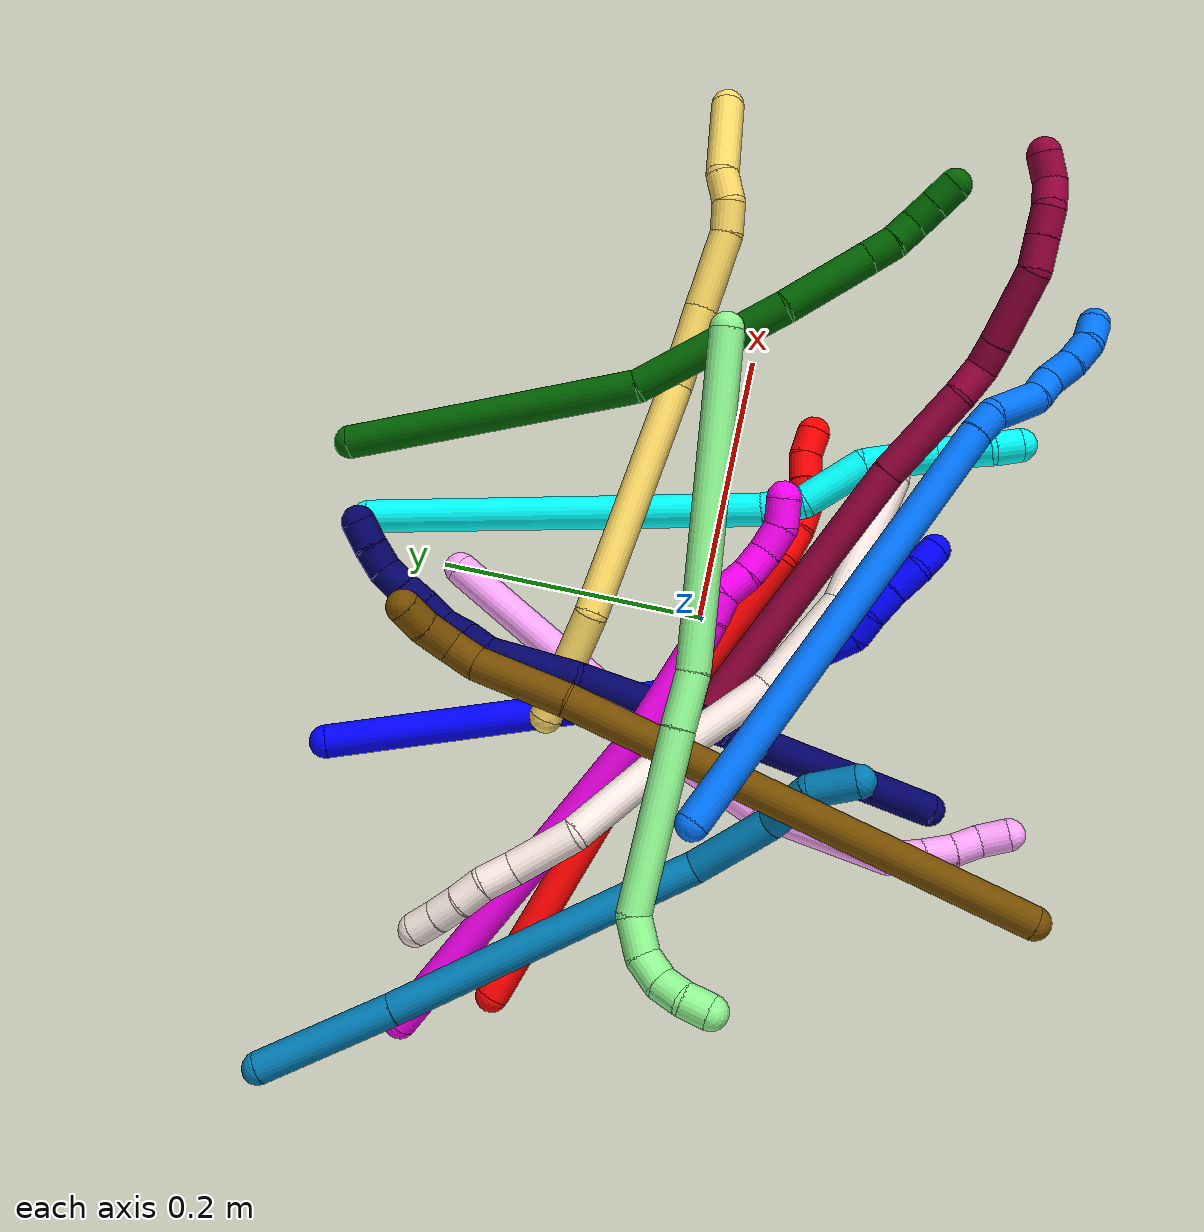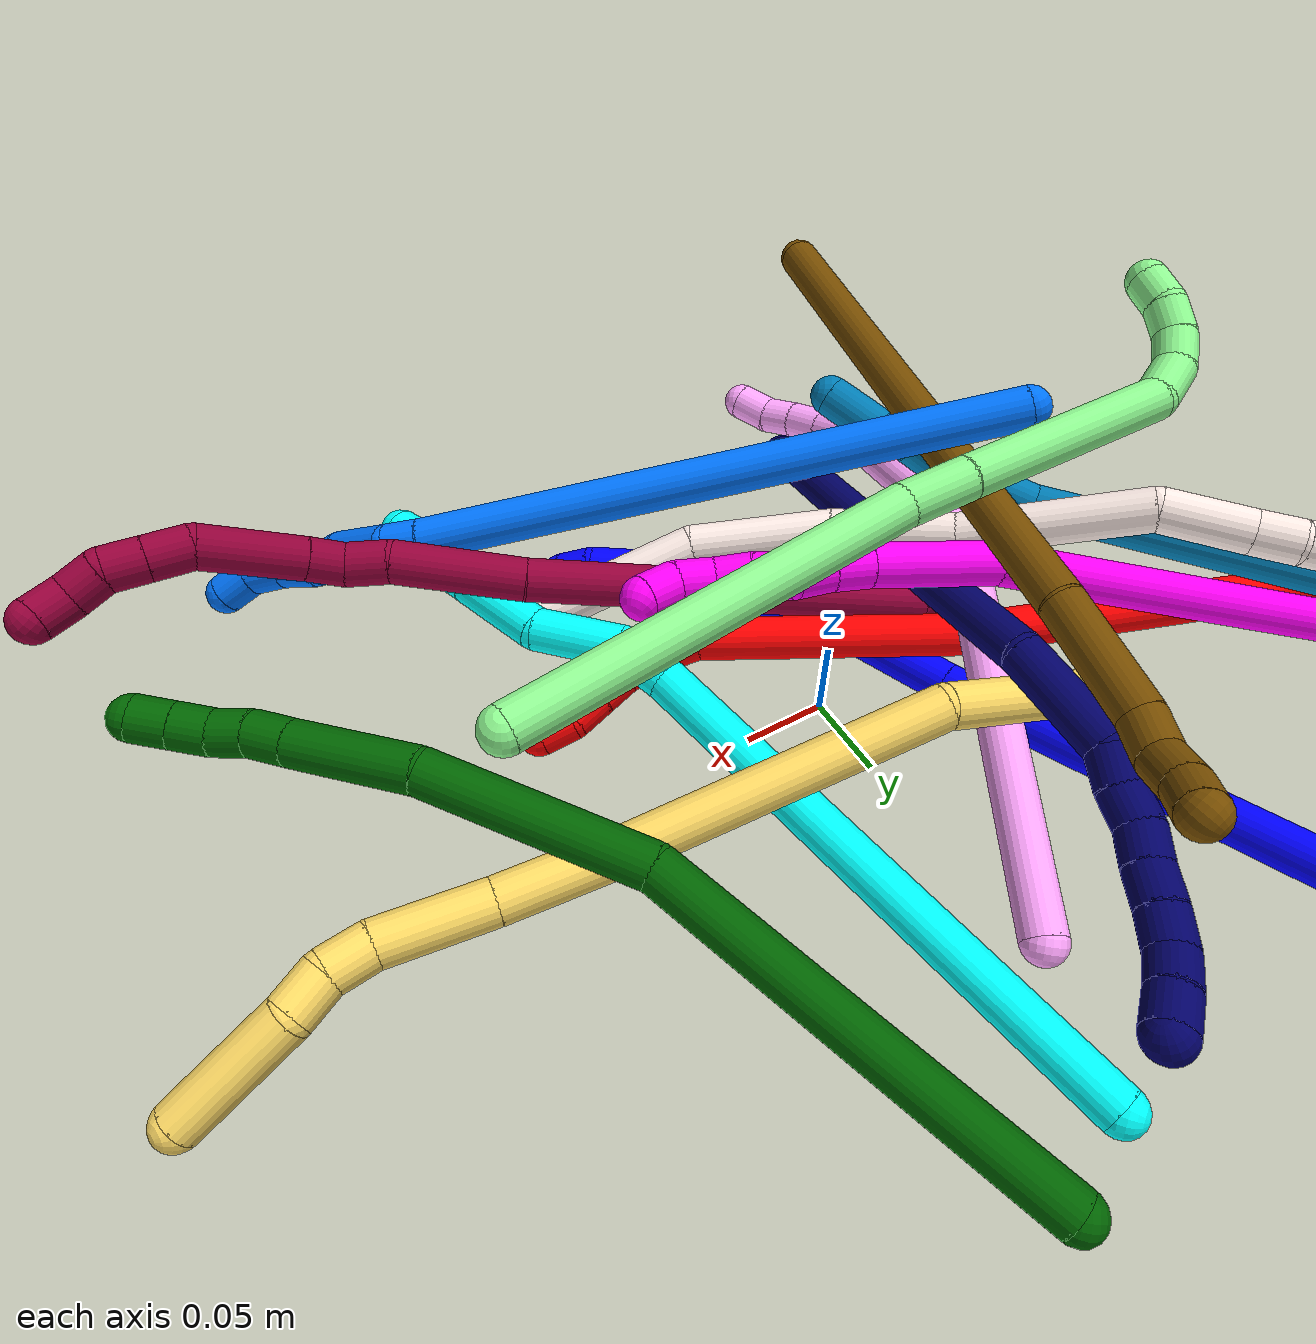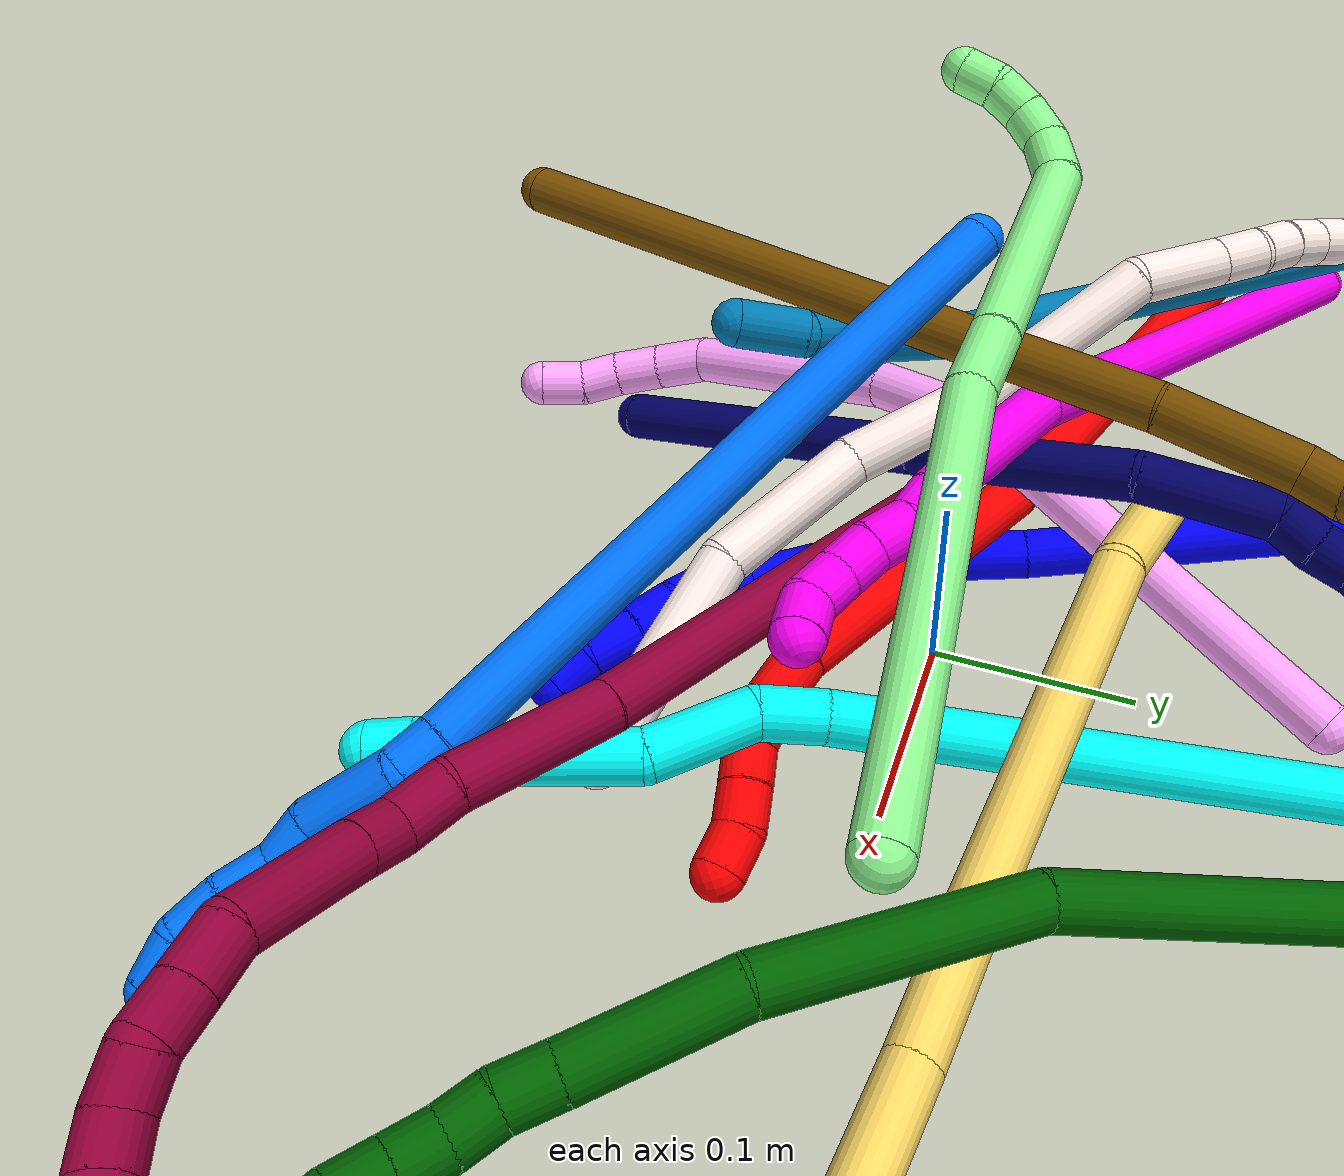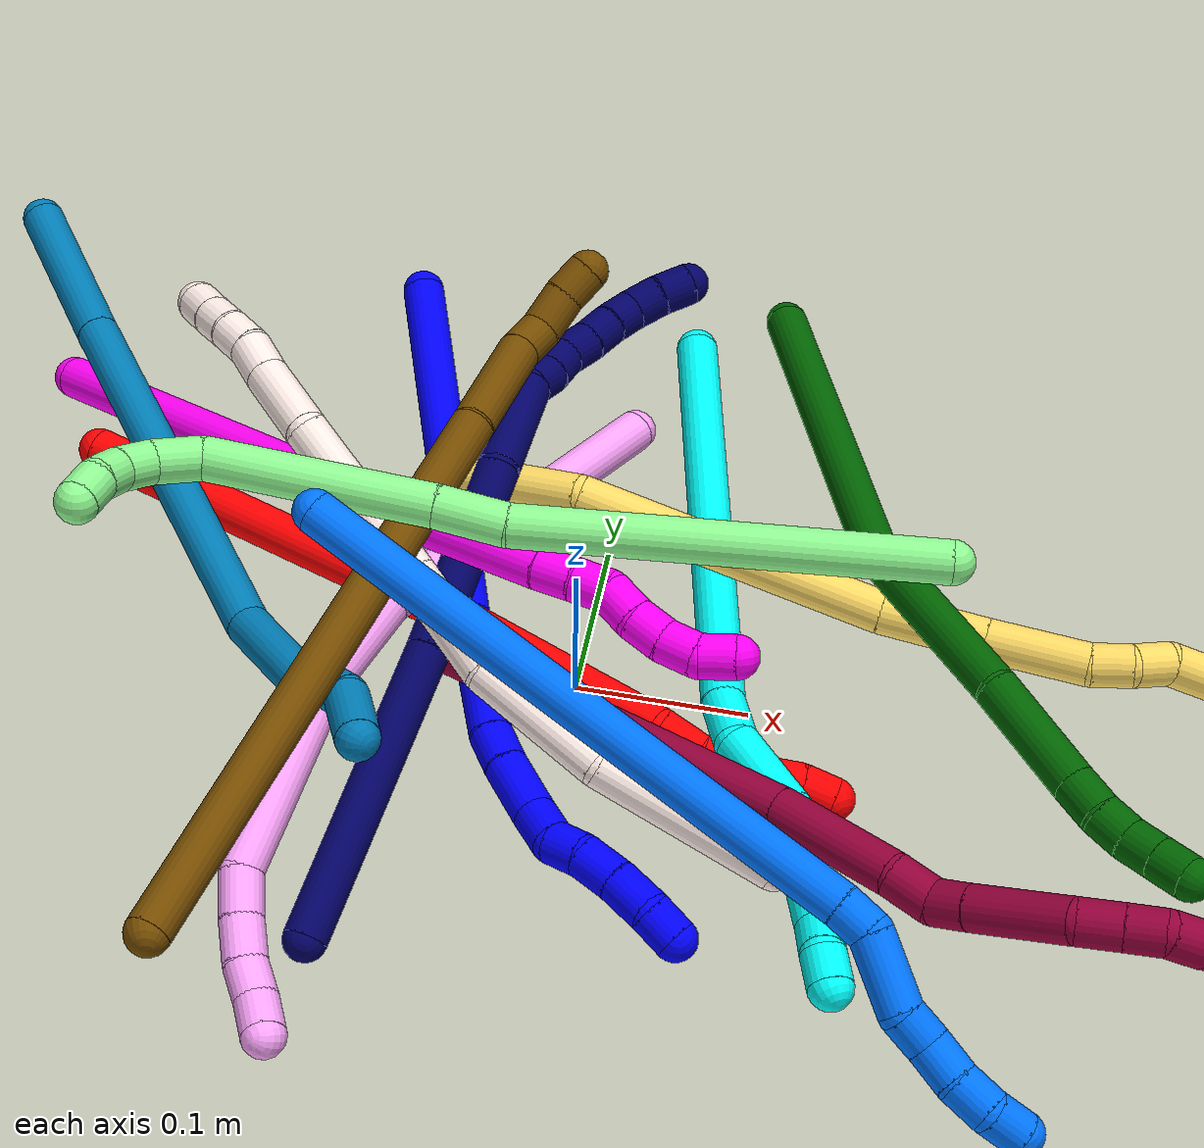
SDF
<sdf version="1.7">
 <world name="default">
  <plugin name="TubeGeneratorPlugin" filename="libtube_generator_plugin.so"/>
  <model name="photoneo_s_sensor">
   <static>1</static>
   <pose>0 0 2 1.57079 1.57079 3.14159</pose>
   <link name="link">
    <inertial><mass>0.1</mass></inertial>
    <sensor name="sensor" type="depth">
     <update_rate>30</update_rate>
     <camera>
      <horizontal_fov>1.22</horizontal_fov>
      <image><width>1920</width><height>1200</height><format>B8G8R8</format></image>
      <clip><near>0.1</near><far>4</far></clip>
      <depth_camera><output>points</output></depth_camera>
     </camera>
     <plugin name="camera_plugin" filename="libgazebo_ros_depth_camera.so">
      <baseline>0.2</baseline>
      <alwaysOn>1</alwaysOn>
      <updateRate>0.0</updateRate>
      <cameraName>camera_ir</cameraName>
      <imageTopicName>/camera/color/image_raw</imageTopicName>
      <cameraInfoTopicName>/camera/color/camera_info</cameraInfoTopicName>
      <depthImageTopicName>/camera/depth/image_raw</depthImageTopicName>
      <depthImageCameraInfoTopicName>/camera/depth/camera_info</depthImageCameraInfoTopicName>
      <pointCloudTopicName>/camera/depth/points</pointCloudTopicName>
      <frameName>fr_optical</frameName>
      <pointCloudCutoff>0.1</pointCloudCutoff>
      <pointCloudCutoffMax>2.0</pointCloudCutoffMax>
      <distortionK1>0</distortionK1>
      <distortionK2>0</distortionK2>
      <distortionK3>0</distortionK3>
      <distortionT1>0</distortionT1>
      <distortionT2>0</distortionT2>
      <CxPrime>0</CxPrime>
      <Cx>0</Cx>
      <Cy>0</Cy>
      <focalLength>0</focalLength>
      <hackBaseline>0</hackBaseline>
     </plugin>
    </sensor>
   </link>
  </model>
  <gravity>0 0 -9.8</gravity>
  <magnetic_field>6e-06 2.3e-05 -4.2e-05</magnetic_field>
  <atmosphere type="adiabatic"/>
  <physics name="default_physics" default="0" type="ode">
   <max_step_size>0.003</max_step_size>
   <real_time_factor>1</real_time_factor>
   <real_time_update_rate>1000</real_time_update_rate>
   <max_contacts>10000</max_contacts>
   <ode>
    <solver>
     <type>quick</type>
     <iters>100</iters>
     <sor>1.3</sor>
     <use_dynamic_moi_rescaling>0</use_dynamic_moi_rescaling>
    </solver>
    <constraints>
     <contact_max_correcting_vel>0</contact_max_correcting_vel>
     <contact_surface_layer>0.001</contact_surface_layer>
     <cfm>0</cfm>
     <erp>0.2</erp>
    </constraints>
   </ode>
  </physics>
  <scene><ambient>0.4 0.4 0.4 1</ambient><background>0.7 0.7 0.7 1</background><shadows>0</shadows></scene>
  <audio><device>default</device></audio>
  <spherical_coordinates>
   <surface_model>EARTH_WGS84</surface_model>
   <latitude_deg>0</latitude_deg>
   <longitude_deg>0</longitude_deg>
   <elevation>0</elevation>
   <heading_deg>0</heading_deg>
  </spherical_coordinates>
  <model name="bin">
   <static>1</static>
   <link name="bottom">
    <collision name="collision-bottom">
     <pose>0 0 -0.01 0 -0 0</pose>
     <geometry><box><size>0.8 0.6 0.02</size></box></geometry>
     <surface>
      <friction><ode><mu>100</mu><mu2>100</mu2></ode></friction>
      <contact><collide_bitmask>65535</collide_bitmask></contact>
     </surface>
    </collision>
   </link>
   <link name="west_wall">
    <collision name="collision-west_wall">
     <pose>-0.41 0 0.1 0 -0 0</pose>
     <geometry><box><size>0.02 0.6 0.2</size></box></geometry>
     <surface>
      <friction><ode><mu>100</mu><mu2>100</mu2></ode></friction>
      <contact><collide_bitmask>65535</collide_bitmask></contact>
     </surface>
    </collision>
   </link>
   <link name="east_wall">
    <collision name="collision-east_wall">
     <pose>0.41 0 0.1 0 -0 0</pose>
     <geometry><box><size>0.02 0.6 0.2</size></box></geometry>
     <surface>
      <friction><ode><mu>100</mu><mu2>100</mu2></ode></friction>
      <contact><collide_bitmask>65535</collide_bitmask></contact>
     </surface>
    </collision>
   </link>
   <link name="south_wall">
    <collision name="collision-south_wall">
     <pose>0 -0.31 0.1 0 -0 0</pose>
     <geometry><box><size>0.8 0.02 0.2</size></box></geometry>
     <surface>
      <friction><ode><mu>100</mu><mu2>100</mu2></ode></friction>
      <contact><collide_bitmask>65535</collide_bitmask></contact>
     </surface>
    </collision>
   </link>
   <link name="north_wall">
    <collision name="collision-north_wall">
     <pose>0 0.31 0.1 0 -0 0</pose>
     <geometry><box><size>0.8 0.02 0.2</size></box></geometry>
     <surface>
      <friction><ode><mu>100</mu><mu2>100</mu2></ode></friction>
      <contact><collide_bitmask>65535</collide_bitmask></contact>
     </surface>
    </collision>
   </link>
  </model>
  <model name="1">
   <static>0</static>
   <link name="1">
    <collision name="collision-cylinder-e_1_1_4">
     <pose>0.101535 -0.058134 -0.023524 1.95531 1.0175 1.38237</pose>
     <geometry><cylinder><radius>0.0125</radius><length>0.238681</length></cylinder></geometry>
     <surface>
      <friction><ode><mu>1.16</mu><mu2>1.16</mu2><slip1>0</slip1><slip2>0</slip2></ode></friction>
      <contact><ode><kp>1e+06</kp><kd>1</kd><max_vel>0</max_vel><min_depth>0.001</min_depth></ode></contact>
     </surface>
    </collision>
    <visual name="visual-cylinder-e_1_1_4">
     <pose>0.101535 -0.058134 -0.023524 1.95531 1.0175 1.38237</pose>
     <geometry><cylinder><radius>0.0125</radius><length>0.238681</length></cylinder></geometry>
     <material><ambient>0 0 1 1</ambient></material>
    </visual>
    <collision name="collision-cylinder-e_2_4_5">
     <pose>0.237876 -0.137309 -0.060192 2.12916 0.951533 1.49761</pose>
     <geometry><cylinder><radius>0.0125</radius><length>0.085487</length></cylinder></geometry>
     <surface>
      <friction><ode><mu>1.16</mu><mu2>1.16</mu2><slip1>0</slip1><slip2>0</slip2></ode></friction>
      <contact><ode><kp>1e+06</kp><kd>1</kd><max_vel>0</max_vel><min_depth>0.001</min_depth></ode></contact>
     </surface>
    </collision>
    <visual name="visual-cylinder-e_2_4_5">
     <pose>0.237876 -0.137309 -0.060192 2.12916 0.951533 1.49761</pose>
     <geometry><cylinder><radius>0.0125</radius><length>0.085487</length></cylinder></geometry>
     <material><ambient>0 0 1 1</ambient></material>
    </visual>
    <collision name="collision-cylinder-e_3_5_6">
     <pose>0.280825 -0.166013 -0.077671 2.08564 0.746467 1.1826</pose>
     <geometry><cylinder><radius>0.0125</radius><length>0.023983</length></cylinder></geometry>
     <surface>
      <friction><ode><mu>1.16</mu><mu2>1.16</mu2><slip1>0</slip1><slip2>0</slip2></ode></friction>
      <contact><ode><kp>1e+06</kp><kd>1</kd><max_vel>0</max_vel><min_depth>0.001</min_depth></ode></contact>
     </surface>
    </collision>
    <visual name="visual-cylinder-e_3_5_6">
     <pose>0.280825 -0.166013 -0.077671 2.08564 0.746467 1.1826</pose>
     <geometry><cylinder><radius>0.0125</radius><length>0.023983</length></cylinder></geometry>
     <material><ambient>0 0 1 1</ambient></material>
    </visual>
    <collision name="collision-cylinder-e_4_6_7">
     <pose>0.300408 -0.186726 -0.088112 2.00847 0.671065 1.00291</pose>
     <geometry><cylinder><radius>0.0125</radius><length>0.036797</length></cylinder></geometry>
     <surface>
      <friction><ode><mu>1.16</mu><mu2>1.16</mu2><slip1>0</slip1><slip2>0</slip2></ode></friction>
      <contact><ode><kp>1e+06</kp><kd>1</kd><max_vel>0</max_vel><min_depth>0.001</min_depth></ode></contact>
     </surface>
    </collision>
    <visual name="visual-cylinder-e_4_6_7">
     <pose>0.300408 -0.186726 -0.088112 2.00847 0.671065 1.00291</pose>
     <geometry><cylinder><radius>0.0125</radius><length>0.036797</length></cylinder></geometry>
     <material><ambient>0 0 1 1</ambient></material>
    </visual>
    <collision name="collision-cylinder-e_5_7_8">
     <pose>0.318911 -0.207614 -0.100344 2.23411 0.617372 1.15818</pose>
     <geometry><cylinder><radius>0.0125</radius><length>0.024397</length></cylinder></geometry>
     <surface>
      <friction><ode><mu>1.16</mu><mu2>1.16</mu2><slip1>0</slip1><slip2>0</slip2></ode></friction>
      <contact><ode><kp>1e+06</kp><kd>1</kd><max_vel>0</max_vel><min_depth>0.001</min_depth></ode></contact>
     </surface>
    </collision>
    <visual name="visual-cylinder-e_5_7_8">
     <pose>0.318911 -0.207614 -0.100344 2.23411 0.617372 1.15818</pose>
     <geometry><cylinder><radius>0.0125</radius><length>0.024397</length></cylinder></geometry>
     <material><ambient>0 0 1 1</ambient></material>
    </visual>
    <collision name="collision-cylinder-e_6_8_9">
     <pose>0.327604 -0.224318 -0.11143 2.08095 0.159218 0.270457</pose>
     <geometry><cylinder><radius>0.0125</radius><length>0.020581</length></cylinder></geometry>
     <surface>
      <friction><ode><mu>1.16</mu><mu2>1.16</mu2><slip1>0</slip1><slip2>0</slip2></ode></friction>
      <contact><ode><kp>1e+06</kp><kd>1</kd><max_vel>0</max_vel><min_depth>0.001</min_depth></ode></contact>
     </surface>
    </collision>
    <visual name="visual-cylinder-e_6_8_9">
     <pose>0.327604 -0.224318 -0.11143 2.08095 0.159218 0.270457</pose>
     <geometry><cylinder><radius>0.0125</radius><length>0.020581</length></cylinder></geometry>
     <material><ambient>0 0 1 1</ambient></material>
    </visual>
    <collision name="collision-cylinder-e_7_9_10">
     <pose>0.332927 -0.244196 -0.119938 1.8824 0.308879 0.421065</pose>
     <geometry><cylinder><radius>0.0125</radius><length>0.024286</length></cylinder></geometry>
     <surface>
      <friction><ode><mu>1.16</mu><mu2>1.16</mu2><slip1>0</slip1><slip2>0</slip2></ode></friction>
      <contact><ode><kp>1e+06</kp><kd>1</kd><max_vel>0</max_vel><min_depth>0.001</min_depth></ode></contact>
     </surface>
    </collision>
    <visual name="visual-cylinder-e_7_9_10">
     <pose>0.332927 -0.244196 -0.119938 1.8824 0.308879 0.421065</pose>
     <geometry><cylinder><radius>0.0125</radius><length>0.024286</length></cylinder></geometry>
     <material><ambient>0 0 1 1</ambient></material>
    </visual>
    <collision name="collision-cylinder-e_8_10_11">
     <pose>0.341734 -0.266354 -0.127057 1.88091 0.412116 0.55801</pose>
     <geometry><cylinder><radius>0.0125</radius><length>0.025548</length></cylinder></geometry>
     <surface>
      <friction><ode><mu>1.16</mu><mu2>1.16</mu2><slip1>0</slip1><slip2>0</slip2></ode></friction>
      <contact><ode><kp>1e+06</kp><kd>1</kd><max_vel>0</max_vel><min_depth>0.001</min_depth></ode></contact>
     </surface>
    </collision>
    <visual name="visual-cylinder-e_8_10_11">
     <pose>0.341734 -0.266354 -0.127057 1.88091 0.412116 0.55801</pose>
     <geometry><cylinder><radius>0.0125</radius><length>0.025548</length></cylinder></geometry>
     <material><ambient>0 0 1 1</ambient></material>
    </visual>
    <collision name="collision-cylinder-e_9_11_2">
     <pose>0.350822 -0.286804 -0.13036 1.54194 0.403279 0.392103</pose>
     <geometry><cylinder><radius>0.0125</radius><length>0.020239</length></cylinder></geometry>
     <surface>
      <friction><ode><mu>1.16</mu><mu2>1.16</mu2><slip1>0</slip1><slip2>0</slip2></ode></friction>
      <contact><ode><kp>1e+06</kp><kd>1</kd><max_vel>0</max_vel><min_depth>0.001</min_depth></ode></contact>
     </surface>
    </collision>
    <visual name="visual-cylinder-e_9_11_2">
     <pose>0.350822 -0.286804 -0.13036 1.54194 0.403279 0.392103</pose>
     <geometry><cylinder><radius>0.0125</radius><length>0.020239</length></cylinder></geometry>
     <material><ambient>0 0 1 1</ambient></material>
    </visual>
    <collision name="collision-sphere-2">
     <pose>0.354794 -0.296108 -0.130091 0 -0 0</pose>
     <geometry><sphere><radius>0.0125</radius></sphere></geometry>
     <surface>
      <friction><ode><mu>1.16</mu><mu2>1.16</mu2><slip1>0</slip1><slip2>0</slip2></ode></friction>
      <contact><ode><kp>1e+06</kp><kd>1</kd><max_vel>0</max_vel><min_depth>0.001</min_depth></ode></contact>
     </surface>
    </collision>
    <visual name="visual-sphere-2">
     <pose>0.354794 -0.296108 -0.130091 0 -0 0</pose>
     <geometry><sphere><radius>0.0125</radius></sphere></geometry>
     <material><ambient>0 0 1 1</ambient></material>
    </visual>
    <collision name="collision-sphere-11">
     <pose>0.346851 -0.2775 -0.130628 0 -0 0</pose>
     <geometry><sphere><radius>0.0125</radius></sphere></geometry>
     <surface>
      <friction><ode><mu>1.16</mu><mu2>1.16</mu2><slip1>0</slip1><slip2>0</slip2></ode></friction>
      <contact><ode><kp>1e+06</kp><kd>1</kd><max_vel>0</max_vel><min_depth>0.001</min_depth></ode></contact>
     </surface>
    </collision>
    <visual name="visual-sphere-11">
     <pose>0.346851 -0.2775 -0.130628 0 -0 0</pose>
     <geometry><sphere><radius>0.0125</radius></sphere></geometry>
     <material><ambient>0 0 1 1</ambient></material>
    </visual>
    <collision name="collision-sphere-10">
     <pose>0.336618 -0.255207 -0.123485 0 -0 0</pose>
     <geometry><sphere><radius>0.0125</radius></sphere></geometry>
     <surface>
      <friction><ode><mu>1.16</mu><mu2>1.16</mu2><slip1>0</slip1><slip2>0</slip2></ode></friction>
      <contact><ode><kp>1e+06</kp><kd>1</kd><max_vel>0</max_vel><min_depth>0.001</min_depth></ode></contact>
     </surface>
    </collision>
    <visual name="visual-sphere-10">
     <pose>0.336618 -0.255207 -0.123485 0 -0 0</pose>
     <geometry><sphere><radius>0.0125</radius></sphere></geometry>
     <material><ambient>0 0 1 1</ambient></material>
    </visual>
    <collision name="collision-sphere-9">
     <pose>0.329235 -0.233185 -0.116391 0 -0 0</pose>
     <geometry><sphere><radius>0.0125</radius></sphere></geometry>
     <surface>
      <friction><ode><mu>1.16</mu><mu2>1.16</mu2><slip1>0</slip1><slip2>0</slip2></ode></friction>
      <contact><ode><kp>1e+06</kp><kd>1</kd><max_vel>0</max_vel><min_depth>0.001</min_depth></ode></contact>
     </surface>
    </collision>
    <visual name="visual-sphere-9">
     <pose>0.329235 -0.233185 -0.116391 0 -0 0</pose>
     <geometry><sphere><radius>0.0125</radius></sphere></geometry>
     <material><ambient>0 0 1 1</ambient></material>
    </visual>
    <collision name="collision-sphere-4">
     <pose>0.203069 -0.116267 -0.047048 0 -0 0</pose>
     <geometry><sphere><radius>0.0125</radius></sphere></geometry>
     <surface>
      <friction><ode><mu>1.16</mu><mu2>1.16</mu2><slip1>0</slip1><slip2>0</slip2></ode></friction>
      <contact><ode><kp>1e+06</kp><kd>1</kd><max_vel>0</max_vel><min_depth>0.001</min_depth></ode></contact>
     </surface>
    </collision>
    <visual name="visual-sphere-4">
     <pose>0.203069 -0.116267 -0.047048 0 -0 0</pose>
     <geometry><sphere><radius>0.0125</radius></sphere></geometry>
     <material><ambient>0 0 1 1</ambient></material>
    </visual>
    <collision name="collision-sphere-1">
     <geometry><sphere><radius>0.0125</radius></sphere></geometry>
     <surface>
      <friction><ode><mu>1.16</mu><mu2>1.16</mu2><slip1>0</slip1><slip2>0</slip2></ode></friction>
      <contact><ode><kp>1e+06</kp><kd>1</kd><max_vel>0</max_vel><min_depth>0.001</min_depth></ode></contact>
     </surface>
    </collision>
    <visual name="visual-sphere-1">
     <geometry><sphere><radius>0.0125</radius></sphere></geometry>
     <material><ambient>0 0 1 1</ambient></material>
    </visual>
    <collision name="collision-sphere-8">
     <pose>0.325972 -0.215451 -0.106468 0 -0 0</pose>
     <geometry><sphere><radius>0.0125</radius></sphere></geometry>
     <surface>
      <friction><ode><mu>1.16</mu><mu2>1.16</mu2><slip1>0</slip1><slip2>0</slip2></ode></friction>
      <contact><ode><kp>1e+06</kp><kd>1</kd><max_vel>0</max_vel><min_depth>0.001</min_depth></ode></contact>
     </surface>
    </collision>
    <visual name="visual-sphere-8">
     <pose>0.325972 -0.215451 -0.106468 0 -0 0</pose>
     <geometry><sphere><radius>0.0125</radius></sphere></geometry>
     <material><ambient>0 0 1 1</ambient></material>
    </visual>
    <collision name="collision-sphere-5">
     <pose>0.272682 -0.158351 -0.073336 0 -0 0</pose>
     <geometry><sphere><radius>0.0125</radius></sphere></geometry>
     <surface>
      <friction><ode><mu>1.16</mu><mu2>1.16</mu2><slip1>0</slip1><slip2>0</slip2></ode></friction>
      <contact><ode><kp>1e+06</kp><kd>1</kd><max_vel>0</max_vel><min_depth>0.001</min_depth></ode></contact>
     </surface>
    </collision>
    <visual name="visual-sphere-5">
     <pose>0.272682 -0.158351 -0.073336 0 -0 0</pose>
     <geometry><sphere><radius>0.0125</radius></sphere></geometry>
     <material><ambient>0 0 1 1</ambient></material>
    </visual>
    <collision name="collision-sphere-6">
     <pose>0.288968 -0.173675 -0.082005 0 -0 0</pose>
     <geometry><sphere><radius>0.0125</radius></sphere></geometry>
     <surface>
      <friction><ode><mu>1.16</mu><mu2>1.16</mu2><slip1>0</slip1><slip2>0</slip2></ode></friction>
      <contact><ode><kp>1e+06</kp><kd>1</kd><max_vel>0</max_vel><min_depth>0.001</min_depth></ode></contact>
     </surface>
    </collision>
    <visual name="visual-sphere-6">
     <pose>0.288968 -0.173675 -0.082005 0 -0 0</pose>
     <geometry><sphere><radius>0.0125</radius></sphere></geometry>
     <material><ambient>0 0 1 1</ambient></material>
    </visual>
    <collision name="collision-sphere-7">
     <pose>0.311849 -0.199776 -0.09422 0 -0 0</pose>
     <geometry><sphere><radius>0.0125</radius></sphere></geometry>
     <surface>
      <friction><ode><mu>1.16</mu><mu2>1.16</mu2><slip1>0</slip1><slip2>0</slip2></ode></friction>
      <contact><ode><kp>1e+06</kp><kd>1</kd><max_vel>0</max_vel><min_depth>0.001</min_depth></ode></contact>
     </surface>
    </collision>
    <visual name="visual-sphere-7">
     <pose>0.311849 -0.199776 -0.09422 0 -0 0</pose>
     <geometry><sphere><radius>0.0125</radius></sphere></geometry>
     <material><ambient>0 0 1 1</ambient></material>
    </visual>
    <inertial>
     <pose>0.201597 -0.129376 -0.058808 0 -0 0</pose>
     <mass>0.5</mass>
     <inertia>
      <ixx>0.000784</ixx>
      <ixy>0</ixy>
      <ixz>0</ixz>
      <iyy>0.001451</iyy>
      <iyz>0</iyz>
      <izz>-0.000439</izz>
     </inertia>
    </inertial>
   </link>
   <pose>-0.146934 0.25477 0.038023 2.90263 0.219946 -1.78823</pose>
  </model>
  <model name="2">
   <static>0</static>
   <link name="2">
    <collision name="collision-cylinder-e_1_1_4">
     <pose>0.064358 -0.000493 -0.097035 3.13651 0.585625 3.12473</pose>
     <geometry><cylinder><radius>0.0125</radius><length>0.232877</length></cylinder></geometry>
     <surface>
      <friction><ode><mu>1.16</mu><mu2>1.16</mu2><slip1>0</slip1><slip2>0</slip2></ode></friction>
      <contact><ode><kp>1e+06</kp><kd>1</kd><max_vel>0</max_vel><min_depth>0.001</min_depth></ode></contact>
     </surface>
    </collision>
    <visual name="visual-cylinder-e_1_1_4">
     <pose>0.064358 -0.000493 -0.097035 3.13651 0.585625 3.12473</pose>
     <geometry><cylinder><radius>0.0125</radius><length>0.232877</length></cylinder></geometry>
     <material><ambient>1 0 0 1</ambient></material>
    </visual>
    <collision name="collision-cylinder-e_2_4_5">
     <pose>0.166416 -0.008139 -0.26428 3.04007 0.490627 2.74118</pose>
     <geometry><cylinder><radius>0.0125</radius><length>0.160025</length></cylinder></geometry>
     <surface>
      <friction><ode><mu>1.16</mu><mu2>1.16</mu2><slip1>0</slip1><slip2>0</slip2></ode></friction>
      <contact><ode><kp>1e+06</kp><kd>1</kd><max_vel>0</max_vel><min_depth>0.001</min_depth></ode></contact>
     </surface>
    </collision>
    <visual name="visual-cylinder-e_2_4_5">
     <pose>0.166416 -0.008139 -0.26428 3.04007 0.490627 2.74118</pose>
     <geometry><cylinder><radius>0.0125</radius><length>0.160025</length></cylinder></geometry>
     <material><ambient>1 0 0 1</ambient></material>
    </visual>
    <collision name="collision-cylinder-e_3_5_6">
     <pose>0.210035 -0.011639 -0.345047 -2.80855 0.487277 -1.95251</pose>
     <geometry><cylinder><radius>0.0125</radius><length>0.025285</length></cylinder></geometry>
     <surface>
      <friction><ode><mu>1.16</mu><mu2>1.16</mu2><slip1>0</slip1><slip2>0</slip2></ode></friction>
      <contact><ode><kp>1e+06</kp><kd>1</kd><max_vel>0</max_vel><min_depth>0.001</min_depth></ode></contact>
     </surface>
    </collision>
    <visual name="visual-cylinder-e_3_5_6">
     <pose>0.210035 -0.011639 -0.345047 -2.80855 0.487277 -1.95251</pose>
     <geometry><cylinder><radius>0.0125</radius><length>0.025285</length></cylinder></geometry>
     <material><ambient>1 0 0 1</ambient></material>
    </visual>
    <collision name="collision-cylinder-e_4_6_7">
     <pose>0.22175 -0.003165 -0.363404 -2.58779 0.563549 -1.58918</pose>
     <geometry><cylinder><radius>0.0125</radius><length>0.021695</length></cylinder></geometry>
     <surface>
      <friction><ode><mu>1.16</mu><mu2>1.16</mu2><slip1>0</slip1><slip2>0</slip2></ode></friction>
      <contact><ode><kp>1e+06</kp><kd>1</kd><max_vel>0</max_vel><min_depth>0.001</min_depth></ode></contact>
     </surface>
    </collision>
    <visual name="visual-cylinder-e_4_6_7">
     <pose>0.22175 -0.003165 -0.363404 -2.58779 0.563549 -1.58918</pose>
     <geometry><cylinder><radius>0.0125</radius><length>0.021695</length></cylinder></geometry>
     <material><ambient>1 0 0 1</ambient></material>
    </visual>
    <collision name="collision-cylinder-e_5_7_8">
     <pose>0.235775 0.005075 -0.375769 -2.4992 0.964901 -2.00966</pose>
     <geometry><cylinder><radius>0.0125</radius><length>0.020028</length></cylinder></geometry>
     <surface>
      <friction><ode><mu>1.16</mu><mu2>1.16</mu2><slip1>0</slip1><slip2>0</slip2></ode></friction>
      <contact><ode><kp>1e+06</kp><kd>1</kd><max_vel>0</max_vel><min_depth>0.001</min_depth></ode></contact>
     </surface>
    </collision>
    <visual name="visual-cylinder-e_5_7_8">
     <pose>0.235775 0.005075 -0.375769 -2.4992 0.964901 -2.00966</pose>
     <geometry><cylinder><radius>0.0125</radius><length>0.020028</length></cylinder></geometry>
     <material><ambient>1 0 0 1</ambient></material>
    </visual>
    <collision name="collision-cylinder-e_6_8_9">
     <pose>0.251866 0.012393 -0.385178 -2.46342 0.90145 -1.88199</pose>
     <geometry><cylinder><radius>0.0125</radius><length>0.020044</length></cylinder></geometry>
     <surface>
      <friction><ode><mu>1.16</mu><mu2>1.16</mu2><slip1>0</slip1><slip2>0</slip2></ode></friction>
      <contact><ode><kp>1e+06</kp><kd>1</kd><max_vel>0</max_vel><min_depth>0.001</min_depth></ode></contact>
     </surface>
    </collision>
    <visual name="visual-cylinder-e_6_8_9">
     <pose>0.251866 0.012393 -0.385178 -2.46342 0.90145 -1.88199</pose>
     <geometry><cylinder><radius>0.0125</radius><length>0.020044</length></cylinder></geometry>
     <material><ambient>1 0 0 1</ambient></material>
    </visual>
    <collision name="collision-cylinder-e_7_9_2">
     <pose>0.266015 0.01917 -0.397276 -2.76419 0.678316 -2.14927</pose>
     <geometry><cylinder><radius>0.0125</radius><length>0.020048</length></cylinder></geometry>
     <surface>
      <friction><ode><mu>1.16</mu><mu2>1.16</mu2><slip1>0</slip1><slip2>0</slip2></ode></friction>
      <contact><ode><kp>1e+06</kp><kd>1</kd><max_vel>0</max_vel><min_depth>0.001</min_depth></ode></contact>
     </surface>
    </collision>
    <visual name="visual-cylinder-e_7_9_2">
     <pose>0.266015 0.01917 -0.397276 -2.76419 0.678316 -2.14927</pose>
     <geometry><cylinder><radius>0.0125</radius><length>0.020048</length></cylinder></geometry>
     <material><ambient>1 0 0 1</ambient></material>
    </visual>
    <collision name="collision-sphere-2">
     <pose>0.272305 0.022046 -0.404531 0 -0 0</pose>
     <geometry><sphere><radius>0.0125</radius></sphere></geometry>
     <surface>
      <friction><ode><mu>1.16</mu><mu2>1.16</mu2><slip1>0</slip1><slip2>0</slip2></ode></friction>
      <contact><ode><kp>1e+06</kp><kd>1</kd><max_vel>0</max_vel><min_depth>0.001</min_depth></ode></contact>
     </surface>
    </collision>
    <visual name="visual-sphere-2">
     <pose>0.272305 0.022046 -0.404531 0 -0 0</pose>
     <geometry><sphere><radius>0.0125</radius></sphere></geometry>
     <material><ambient>1 0 0 1</ambient></material>
    </visual>
    <collision name="collision-sphere-9">
     <pose>0.259725 0.016294 -0.39002 0 -0 0</pose>
     <geometry><sphere><radius>0.0125</radius></sphere></geometry>
     <surface>
      <friction><ode><mu>1.16</mu><mu2>1.16</mu2><slip1>0</slip1><slip2>0</slip2></ode></friction>
      <contact><ode><kp>1e+06</kp><kd>1</kd><max_vel>0</max_vel><min_depth>0.001</min_depth></ode></contact>
     </surface>
    </collision>
    <visual name="visual-sphere-9">
     <pose>0.259725 0.016294 -0.39002 0 -0 0</pose>
     <geometry><sphere><radius>0.0125</radius></sphere></geometry>
     <material><ambient>1 0 0 1</ambient></material>
    </visual>
    <collision name="collision-sphere-4">
     <pose>0.128716 -0.000987 -0.194069 0 -0 0</pose>
     <geometry><sphere><radius>0.0125</radius></sphere></geometry>
     <surface>
      <friction><ode><mu>1.16</mu><mu2>1.16</mu2><slip1>0</slip1><slip2>0</slip2></ode></friction>
      <contact><ode><kp>1e+06</kp><kd>1</kd><max_vel>0</max_vel><min_depth>0.001</min_depth></ode></contact>
     </surface>
    </collision>
    <visual name="visual-sphere-4">
     <pose>0.128716 -0.000987 -0.194069 0 -0 0</pose>
     <geometry><sphere><radius>0.0125</radius></sphere></geometry>
     <material><ambient>1 0 0 1</ambient></material>
    </visual>
    <collision name="collision-sphere-1">
     <geometry><sphere><radius>0.0125</radius></sphere></geometry>
     <surface>
      <friction><ode><mu>1.16</mu><mu2>1.16</mu2><slip1>0</slip1><slip2>0</slip2></ode></friction>
      <contact><ode><kp>1e+06</kp><kd>1</kd><max_vel>0</max_vel><min_depth>0.001</min_depth></ode></contact>
     </surface>
    </collision>
    <visual name="visual-sphere-1">
     <geometry><sphere><radius>0.0125</radius></sphere></geometry>
     <material><ambient>1 0 0 1</ambient></material>
    </visual>
    <collision name="collision-sphere-8">
     <pose>0.244007 0.008492 -0.380335 0 -0 0</pose>
     <geometry><sphere><radius>0.0125</radius></sphere></geometry>
     <surface>
      <friction><ode><mu>1.16</mu><mu2>1.16</mu2><slip1>0</slip1><slip2>0</slip2></ode></friction>
      <contact><ode><kp>1e+06</kp><kd>1</kd><max_vel>0</max_vel><min_depth>0.001</min_depth></ode></contact>
     </surface>
    </collision>
    <visual name="visual-sphere-8">
     <pose>0.244007 0.008492 -0.380335 0 -0 0</pose>
     <geometry><sphere><radius>0.0125</radius></sphere></geometry>
     <material><ambient>1 0 0 1</ambient></material>
    </visual>
    <collision name="collision-sphere-5">
     <pose>0.204116 -0.015291 -0.33449 0 -0 0</pose>
     <geometry><sphere><radius>0.0125</radius></sphere></geometry>
     <surface>
      <friction><ode><mu>1.16</mu><mu2>1.16</mu2><slip1>0</slip1><slip2>0</slip2></ode></friction>
      <contact><ode><kp>1e+06</kp><kd>1</kd><max_vel>0</max_vel><min_depth>0.001</min_depth></ode></contact>
     </surface>
    </collision>
    <visual name="visual-sphere-5">
     <pose>0.204116 -0.015291 -0.33449 0 -0 0</pose>
     <geometry><sphere><radius>0.0125</radius></sphere></geometry>
     <material><ambient>1 0 0 1</ambient></material>
    </visual>
    <collision name="collision-sphere-6">
     <pose>0.215955 -0.007987 -0.355604 0 -0 0</pose>
     <geometry><sphere><radius>0.0125</radius></sphere></geometry>
     <surface>
      <friction><ode><mu>1.16</mu><mu2>1.16</mu2><slip1>0</slip1><slip2>0</slip2></ode></friction>
      <contact><ode><kp>1e+06</kp><kd>1</kd><max_vel>0</max_vel><min_depth>0.001</min_depth></ode></contact>
     </surface>
    </collision>
    <visual name="visual-sphere-6">
     <pose>0.215955 -0.007987 -0.355604 0 -0 0</pose>
     <geometry><sphere><radius>0.0125</radius></sphere></geometry>
     <material><ambient>1 0 0 1</ambient></material>
    </visual>
    <collision name="collision-sphere-7">
     <pose>0.227544 0.001658 -0.371203 0 -0 0</pose>
     <geometry><sphere><radius>0.0125</radius></sphere></geometry>
     <surface>
      <friction><ode><mu>1.16</mu><mu2>1.16</mu2><slip1>0</slip1><slip2>0</slip2></ode></friction>
      <contact><ode><kp>1e+06</kp><kd>1</kd><max_vel>0</max_vel><min_depth>0.001</min_depth></ode></contact>
     </surface>
    </collision>
    <visual name="visual-sphere-7">
     <pose>0.227544 0.001658 -0.371203 0 -0 0</pose>
     <geometry><sphere><radius>0.0125</radius></sphere></geometry>
     <material><ambient>1 0 0 1</ambient></material>
    </visual>
    <inertial>
     <pose>0.133686 -0.002092 -0.209415 0 -0 0</pose>
     <mass>0.5</mass>
     <inertia>
      <ixx>-0.001019</ixx>
      <ixy>0</ixy>
      <ixz>0</ixz>
      <iyy>0.001522</iyy>
      <iyz>0</iyz>
      <izz>-0.000755</izz>
     </inertia>
    </inertial>
   </link>
   <pose>-0.307984 0.094866 0.032293 -1.42741 -0.213587 0.637393</pose>
  </model>
  <model name="3">
   <static>0</static>
   <link name="3">
    <collision name="collision-cylinder-e_1_1_4">
     <pose>0.005342 -0.062137 -0.136666 2.71487 0.035568 0.163812</pose>
     <geometry><cylinder><radius>0.0125</radius><length>0.300447</length></cylinder></geometry>
     <surface>
      <friction><ode><mu>1.16</mu><mu2>1.16</mu2><slip1>0</slip1><slip2>0</slip2></ode></friction>
      <contact><ode><kp>1e+06</kp><kd>1</kd><max_vel>0</max_vel><min_depth>0.001</min_depth></ode></contact>
     </surface>
    </collision>
    <visual name="visual-cylinder-e_1_1_4">
     <pose>0.005342 -0.062137 -0.136666 2.71487 0.035568 0.163812</pose>
     <geometry><cylinder><radius>0.0125</radius><length>0.300447</length></cylinder></geometry>
     <material><ambient>0.003922 1 0.996078 1</ambient></material>
    </visual>
    <collision name="collision-cylinder-e_2_4_5">
     <pose>0.013796 -0.129542 -0.28804 2.79768 0.196601 1.03289</pose>
     <geometry><cylinder><radius>0.0125</radius><length>0.031862</length></cylinder></geometry>
     <surface>
      <friction><ode><mu>1.16</mu><mu2>1.16</mu2><slip1>0</slip1><slip2>0</slip2></ode></friction>
      <contact><ode><kp>1e+06</kp><kd>1</kd><max_vel>0</max_vel><min_depth>0.001</min_depth></ode></contact>
     </surface>
    </collision>
    <visual name="visual-cylinder-e_2_4_5">
     <pose>0.013796 -0.129542 -0.28804 2.79768 0.196601 1.03289</pose>
     <geometry><cylinder><radius>0.0125</radius><length>0.031862</length></cylinder></geometry>
     <material><ambient>0.003922 1 0.996078 1</ambient></material>
    </visual>
    <collision name="collision-cylinder-e_3_5_6">
     <pose>0.023759 -0.132637 -0.327478 -3.05394 0.26931 -2.51546</pose>
     <geometry><cylinder><radius>0.0125</radius><length>0.051503</length></cylinder></geometry>
     <surface>
      <friction><ode><mu>1.16</mu><mu2>1.16</mu2><slip1>0</slip1><slip2>0</slip2></ode></friction>
      <contact><ode><kp>1e+06</kp><kd>1</kd><max_vel>0</max_vel><min_depth>0.001</min_depth></ode></contact>
     </surface>
    </collision>
    <visual name="visual-cylinder-e_3_5_6">
     <pose>0.023759 -0.132637 -0.327478 -3.05394 0.26931 -2.51546</pose>
     <geometry><cylinder><radius>0.0125</radius><length>0.051503</length></cylinder></geometry>
     <material><ambient>0.003922 1 0.996078 1</ambient></material>
    </visual>
    <collision name="collision-cylinder-e_4_6_7">
     <pose>0.031999 -0.137829 -0.378173 2.86521 0.051387 0.365434</pose>
     <geometry><cylinder><radius>0.0125</radius><length>0.054053</length></cylinder></geometry>
     <surface>
      <friction><ode><mu>1.16</mu><mu2>1.16</mu2><slip1>0</slip1><slip2>0</slip2></ode></friction>
      <contact><ode><kp>1e+06</kp><kd>1</kd><max_vel>0</max_vel><min_depth>0.001</min_depth></ode></contact>
     </surface>
    </collision>
    <visual name="visual-cylinder-e_4_6_7">
     <pose>0.031999 -0.137829 -0.378173 2.86521 0.051387 0.365434</pose>
     <geometry><cylinder><radius>0.0125</radius><length>0.054053</length></cylinder></geometry>
     <material><ambient>0.003922 1 0.996078 1</ambient></material>
    </visual>
    <collision name="collision-cylinder-e_5_7_8">
     <pose>0.034043 -0.148241 -0.414753 2.86209 0.05932 0.41573</pose>
     <geometry><cylinder><radius>0.0125</radius><length>0.022123</length></cylinder></geometry>
     <surface>
      <friction><ode><mu>1.16</mu><mu2>1.16</mu2><slip1>0</slip1><slip2>0</slip2></ode></friction>
      <contact><ode><kp>1e+06</kp><kd>1</kd><max_vel>0</max_vel><min_depth>0.001</min_depth></ode></contact>
     </surface>
    </collision>
    <visual name="visual-cylinder-e_5_7_8">
     <pose>0.034043 -0.148241 -0.414753 2.86209 0.05932 0.41573</pose>
     <geometry><cylinder><radius>0.0125</radius><length>0.022123</length></cylinder></geometry>
     <material><ambient>0.003922 1 0.996078 1</ambient></material>
    </visual>
    <collision name="collision-cylinder-e_6_8_9">
     <pose>0.036503 -0.156038 -0.433981 2.63761 0.181375 0.679046</pose>
     <geometry><cylinder><radius>0.0125</radius><length>0.020003</length></cylinder></geometry>
     <surface>
      <friction><ode><mu>1.16</mu><mu2>1.16</mu2><slip1>0</slip1><slip2>0</slip2></ode></friction>
      <contact><ode><kp>1e+06</kp><kd>1</kd><max_vel>0</max_vel><min_depth>0.001</min_depth></ode></contact>
     </surface>
    </collision>
    <visual name="visual-cylinder-e_6_8_9">
     <pose>0.036503 -0.156038 -0.433981 2.63761 0.181375 0.679046</pose>
     <geometry><cylinder><radius>0.0125</radius><length>0.020003</length></cylinder></geometry>
     <material><ambient>0.003922 1 0.996078 1</ambient></material>
    </visual>
    <collision name="collision-cylinder-e_7_9_2">
     <pose>0.038039 -0.162867 -0.452377 2.93226 -0.026848 -0.254204</pose>
     <geometry><cylinder><radius>0.0125</radius><length>0.020009</length></cylinder></geometry>
     <surface>
      <friction><ode><mu>1.16</mu><mu2>1.16</mu2><slip1>0</slip1><slip2>0</slip2></ode></friction>
      <contact><ode><kp>1e+06</kp><kd>1</kd><max_vel>0</max_vel><min_depth>0.001</min_depth></ode></contact>
     </surface>
    </collision>
    <visual name="visual-cylinder-e_7_9_2">
     <pose>0.038039 -0.162867 -0.452377 2.93226 -0.026848 -0.254204</pose>
     <geometry><cylinder><radius>0.0125</radius><length>0.020009</length></cylinder></geometry>
     <material><ambient>0.003922 1 0.996078 1</ambient></material>
    </visual>
    <collision name="collision-sphere-2">
     <pose>0.03777 -0.164945 -0.46216 0 -0 0</pose>
     <geometry><sphere><radius>0.0125</radius></sphere></geometry>
     <surface>
      <friction><ode><mu>1.16</mu><mu2>1.16</mu2><slip1>0</slip1><slip2>0</slip2></ode></friction>
      <contact><ode><kp>1e+06</kp><kd>1</kd><max_vel>0</max_vel><min_depth>0.001</min_depth></ode></contact>
     </surface>
    </collision>
    <visual name="visual-sphere-2">
     <pose>0.03777 -0.164945 -0.46216 0 -0 0</pose>
     <geometry><sphere><radius>0.0125</radius></sphere></geometry>
     <material><ambient>0.003922 1 0.996078 1</ambient></material>
    </visual>
    <collision name="collision-sphere-9">
     <pose>0.038307 -0.160789 -0.442595 0 -0 0</pose>
     <geometry><sphere><radius>0.0125</radius></sphere></geometry>
     <surface>
      <friction><ode><mu>1.16</mu><mu2>1.16</mu2><slip1>0</slip1><slip2>0</slip2></ode></friction>
      <contact><ode><kp>1e+06</kp><kd>1</kd><max_vel>0</max_vel><min_depth>0.001</min_depth></ode></contact>
     </surface>
    </collision>
    <visual name="visual-sphere-9">
     <pose>0.038307 -0.160789 -0.442595 0 -0 0</pose>
     <geometry><sphere><radius>0.0125</radius></sphere></geometry>
     <material><ambient>0.003922 1 0.996078 1</ambient></material>
    </visual>
    <collision name="collision-sphere-4">
     <pose>0.010684 -0.124274 -0.273331 0 -0 0</pose>
     <geometry><sphere><radius>0.0125</radius></sphere></geometry>
     <surface>
      <friction><ode><mu>1.16</mu><mu2>1.16</mu2><slip1>0</slip1><slip2>0</slip2></ode></friction>
      <contact><ode><kp>1e+06</kp><kd>1</kd><max_vel>0</max_vel><min_depth>0.001</min_depth></ode></contact>
     </surface>
    </collision>
    <visual name="visual-sphere-4">
     <pose>0.010684 -0.124274 -0.273331 0 -0 0</pose>
     <geometry><sphere><radius>0.0125</radius></sphere></geometry>
     <material><ambient>0.003922 1 0.996078 1</ambient></material>
    </visual>
    <collision name="collision-sphere-1">
     <geometry><sphere><radius>0.0125</radius></sphere></geometry>
     <surface>
      <friction><ode><mu>1.16</mu><mu2>1.16</mu2><slip1>0</slip1><slip2>0</slip2></ode></friction>
      <contact><ode><kp>1e+06</kp><kd>1</kd><max_vel>0</max_vel><min_depth>0.001</min_depth></ode></contact>
     </surface>
    </collision>
    <visual name="visual-sphere-1">
     <geometry><sphere><radius>0.0125</radius></sphere></geometry>
     <material><ambient>0.003922 1 0.996078 1</ambient></material>
    </visual>
    <collision name="collision-sphere-8">
     <pose>0.034699 -0.151287 -0.425366 0 -0 0</pose>
     <geometry><sphere><radius>0.0125</radius></sphere></geometry>
     <surface>
      <friction><ode><mu>1.16</mu><mu2>1.16</mu2><slip1>0</slip1><slip2>0</slip2></ode></friction>
      <contact><ode><kp>1e+06</kp><kd>1</kd><max_vel>0</max_vel><min_depth>0.001</min_depth></ode></contact>
     </surface>
    </collision>
    <visual name="visual-sphere-8">
     <pose>0.034699 -0.151287 -0.425366 0 -0 0</pose>
     <geometry><sphere><radius>0.0125</radius></sphere></geometry>
     <material><ambient>0.003922 1 0.996078 1</ambient></material>
    </visual>
    <collision name="collision-sphere-5">
     <pose>0.016908 -0.13481 -0.30275 0 -0 0</pose>
     <geometry><sphere><radius>0.0125</radius></sphere></geometry>
     <surface>
      <friction><ode><mu>1.16</mu><mu2>1.16</mu2><slip1>0</slip1><slip2>0</slip2></ode></friction>
      <contact><ode><kp>1e+06</kp><kd>1</kd><max_vel>0</max_vel><min_depth>0.001</min_depth></ode></contact>
     </surface>
    </collision>
    <visual name="visual-sphere-5">
     <pose>0.016908 -0.13481 -0.30275 0 -0 0</pose>
     <geometry><sphere><radius>0.0125</radius></sphere></geometry>
     <material><ambient>0.003922 1 0.996078 1</ambient></material>
    </visual>
    <collision name="collision-sphere-6">
     <pose>0.030611 -0.130464 -0.352206 0 -0 0</pose>
     <geometry><sphere><radius>0.0125</radius></sphere></geometry>
     <surface>
      <friction><ode><mu>1.16</mu><mu2>1.16</mu2><slip1>0</slip1><slip2>0</slip2></ode></friction>
      <contact><ode><kp>1e+06</kp><kd>1</kd><max_vel>0</max_vel><min_depth>0.001</min_depth></ode></contact>
     </surface>
    </collision>
    <visual name="visual-sphere-6">
     <pose>0.030611 -0.130464 -0.352206 0 -0 0</pose>
     <geometry><sphere><radius>0.0125</radius></sphere></geometry>
     <material><ambient>0.003922 1 0.996078 1</ambient></material>
    </visual>
    <collision name="collision-sphere-7">
     <pose>0.033387 -0.145195 -0.404139 0 -0 0</pose>
     <geometry><sphere><radius>0.0125</radius></sphere></geometry>
     <surface>
      <friction><ode><mu>1.16</mu><mu2>1.16</mu2><slip1>0</slip1><slip2>0</slip2></ode></friction>
      <contact><ode><kp>1e+06</kp><kd>1</kd><max_vel>0</max_vel><min_depth>0.001</min_depth></ode></contact>
     </surface>
    </collision>
    <visual name="visual-sphere-7">
     <pose>0.033387 -0.145195 -0.404139 0 -0 0</pose>
     <geometry><sphere><radius>0.0125</radius></sphere></geometry>
     <material><ambient>0.003922 1 0.996078 1</ambient></material>
    </visual>
    <inertial>
     <pose>0.014485 -0.093475 -0.228908 0 -0 0</pose>
     <mass>0.5</mass>
     <inertia>
      <ixx>0.002625</ixx>
      <ixy>0</ixy>
      <ixz>0</ixz>
      <iyy>-0.001683</iyy>
      <iyz>0</iyz>
      <izz>0.000823</izz>
     </inertia>
    </inertial>
   </link>
   <pose>0.024566 0.262877 0.0123 -1.28713 -0.881345 0.30374</pose>
  </model>
  <model name="4">
   <static>0</static>
   <link name="4">
    <collision name="collision-cylinder-e_1_1_4">
     <pose>-0.046482 -0.033493 0.097842 0.329816 -0.422413 -0.071332</pose>
     <geometry><cylinder><radius>0.0125</radius><length>0.226764</length></cylinder></geometry>
     <surface>
      <friction><ode><mu>1.16</mu><mu2>1.16</mu2><slip1>0</slip1><slip2>0</slip2></ode></friction>
      <contact><ode><kp>1e+06</kp><kd>1</kd><max_vel>0</max_vel><min_depth>0.001</min_depth></ode></contact>
     </surface>
    </collision>
    <visual name="visual-cylinder-e_1_1_4">
     <pose>-0.046482 -0.033493 0.097842 0.329816 -0.422413 -0.071332</pose>
     <geometry><cylinder><radius>0.0125</radius><length>0.226764</length></cylinder></geometry>
     <material><ambient>1 0.65098 0.996078 1</ambient></material>
    </visual>
    <collision name="collision-cylinder-e_2_4_5">
     <pose>-0.114289 -0.07915 0.213298 0.604353 -0.783494 -0.256135</pose>
     <geometry><cylinder><radius>0.0125</radius><length>0.060429</length></cylinder></geometry>
     <surface>
      <friction><ode><mu>1.16</mu><mu2>1.16</mu2><slip1>0</slip1><slip2>0</slip2></ode></friction>
      <contact><ode><kp>1e+06</kp><kd>1</kd><max_vel>0</max_vel><min_depth>0.001</min_depth></ode></contact>
     </surface>
    </collision>
    <visual name="visual-cylinder-e_2_4_5">
     <pose>-0.114289 -0.07915 0.213298 0.604353 -0.783494 -0.256135</pose>
     <geometry><cylinder><radius>0.0125</radius><length>0.060429</length></cylinder></geometry>
     <material><ambient>1 0.65098 0.996078 1</ambient></material>
    </visual>
    <collision name="collision-cylinder-e_3_5_6">
     <pose>-0.171925 -0.126406 0.258956 0.896594 -0.679799 -0.336931</pose>
     <geometry><cylinder><radius>0.0125</radius><length>0.115526</length></cylinder></geometry>
     <surface>
      <friction><ode><mu>1.16</mu><mu2>1.16</mu2><slip1>0</slip1><slip2>0</slip2></ode></friction>
      <contact><ode><kp>1e+06</kp><kd>1</kd><max_vel>0</max_vel><min_depth>0.001</min_depth></ode></contact>
     </surface>
    </collision>
    <visual name="visual-cylinder-e_3_5_6">
     <pose>-0.171925 -0.126406 0.258956 0.896594 -0.679799 -0.336931</pose>
     <geometry><cylinder><radius>0.0125</radius><length>0.115526</length></cylinder></geometry>
     <material><ambient>1 0.65098 0.996078 1</ambient></material>
    </visual>
    <collision name="collision-cylinder-e_4_6_7">
     <pose>-0.214003 -0.173306 0.290334 1.29552 -0.439359 -0.334745</pose>
     <geometry><cylinder><radius>0.0125</radius><length>0.02711</length></cylinder></geometry>
     <surface>
      <friction><ode><mu>1.16</mu><mu2>1.16</mu2><slip1>0</slip1><slip2>0</slip2></ode></friction>
      <contact><ode><kp>1e+06</kp><kd>1</kd><max_vel>0</max_vel><min_depth>0.001</min_depth></ode></contact>
     </surface>
    </collision>
    <visual name="visual-cylinder-e_4_6_7">
     <pose>-0.214003 -0.173306 0.290334 1.29552 -0.439359 -0.334745</pose>
     <geometry><cylinder><radius>0.0125</radius><length>0.02711</length></cylinder></geometry>
     <material><ambient>1 0.65098 0.996078 1</ambient></material>
    </visual>
    <collision name="collision-cylinder-e_5_7_8">
     <pose>-0.22399 -0.196565 0.296599 1.32031 -0.342986 -0.267316</pose>
     <geometry><cylinder><radius>0.0125</radius><length>0.025107</length></cylinder></geometry>
     <surface>
      <friction><ode><mu>1.16</mu><mu2>1.16</mu2><slip1>0</slip1><slip2>0</slip2></ode></friction>
      <contact><ode><kp>1e+06</kp><kd>1</kd><max_vel>0</max_vel><min_depth>0.001</min_depth></ode></contact>
     </surface>
    </collision>
    <visual name="visual-cylinder-e_5_7_8">
     <pose>-0.22399 -0.196565 0.296599 1.32031 -0.342986 -0.267316</pose>
     <geometry><cylinder><radius>0.0125</radius><length>0.025107</length></cylinder></geometry>
     <material><ambient>1 0.65098 0.996078 1</ambient></material>
    </visual>
    <collision name="collision-cylinder-e_6_8_9">
     <pose>-0.230244 -0.218521 0.300929 1.43835 -0.189493 -0.166038</pose>
     <geometry><cylinder><radius>0.0125</radius><length>0.021577</length></cylinder></geometry>
     <surface>
      <friction><ode><mu>1.16</mu><mu2>1.16</mu2><slip1>0</slip1><slip2>0</slip2></ode></friction>
      <contact><ode><kp>1e+06</kp><kd>1</kd><max_vel>0</max_vel><min_depth>0.001</min_depth></ode></contact>
     </surface>
    </collision>
    <visual name="visual-cylinder-e_6_8_9">
     <pose>-0.230244 -0.218521 0.300929 1.43835 -0.189493 -0.166038</pose>
     <geometry><cylinder><radius>0.0125</radius><length>0.021577</length></cylinder></geometry>
     <material><ambient>1 0.65098 0.996078 1</ambient></material>
    </visual>
    <collision name="collision-cylinder-e_7_9_2">
     <pose>-0.232782 -0.239923 0.306671 1.19164 -0.043016 -0.029168</pose>
     <geometry><cylinder><radius>0.0125</radius><length>0.023486</length></cylinder></geometry>
     <surface>
      <friction><ode><mu>1.16</mu><mu2>1.16</mu2><slip1>0</slip1><slip2>0</slip2></ode></friction>
      <contact><ode><kp>1e+06</kp><kd>1</kd><max_vel>0</max_vel><min_depth>0.001</min_depth></ode></contact>
     </surface>
    </collision>
    <visual name="visual-cylinder-e_7_9_2">
     <pose>-0.232782 -0.239923 0.306671 1.19164 -0.043016 -0.029168</pose>
     <geometry><cylinder><radius>0.0125</radius><length>0.023486</length></cylinder></geometry>
     <material><ambient>1 0.65098 0.996078 1</ambient></material>
    </visual>
    <collision name="collision-sphere-2">
     <pose>-0.233287 -0.250822 0.311013 0 -0 0</pose>
     <geometry><sphere><radius>0.0125</radius></sphere></geometry>
     <surface>
      <friction><ode><mu>1.16</mu><mu2>1.16</mu2><slip1>0</slip1><slip2>0</slip2></ode></friction>
      <contact><ode><kp>1e+06</kp><kd>1</kd><max_vel>0</max_vel><min_depth>0.001</min_depth></ode></contact>
     </surface>
    </collision>
    <visual name="visual-sphere-2">
     <pose>-0.233287 -0.250822 0.311013 0 -0 0</pose>
     <geometry><sphere><radius>0.0125</radius></sphere></geometry>
     <material><ambient>1 0.65098 0.996078 1</ambient></material>
    </visual>
    <collision name="collision-sphere-9">
     <pose>-0.232277 -0.229024 0.302328 0 -0 0</pose>
     <geometry><sphere><radius>0.0125</radius></sphere></geometry>
     <surface>
      <friction><ode><mu>1.16</mu><mu2>1.16</mu2><slip1>0</slip1><slip2>0</slip2></ode></friction>
      <contact><ode><kp>1e+06</kp><kd>1</kd><max_vel>0</max_vel><min_depth>0.001</min_depth></ode></contact>
     </surface>
    </collision>
    <visual name="visual-sphere-9">
     <pose>-0.232277 -0.229024 0.302328 0 -0 0</pose>
     <geometry><sphere><radius>0.0125</radius></sphere></geometry>
     <material><ambient>1 0.65098 0.996078 1</ambient></material>
    </visual>
    <collision name="collision-sphere-4">
     <pose>-0.092965 -0.066986 0.195684 0 -0 0</pose>
     <geometry><sphere><radius>0.0125</radius></sphere></geometry>
     <surface>
      <friction><ode><mu>1.16</mu><mu2>1.16</mu2><slip1>0</slip1><slip2>0</slip2></ode></friction>
      <contact><ode><kp>1e+06</kp><kd>1</kd><max_vel>0</max_vel><min_depth>0.001</min_depth></ode></contact>
     </surface>
    </collision>
    <visual name="visual-sphere-4">
     <pose>-0.092965 -0.066986 0.195684 0 -0 0</pose>
     <geometry><sphere><radius>0.0125</radius></sphere></geometry>
     <material><ambient>1 0.65098 0.996078 1</ambient></material>
    </visual>
    <collision name="collision-sphere-1">
     <geometry><sphere><radius>0.0125</radius></sphere></geometry>
     <surface>
      <friction><ode><mu>1.16</mu><mu2>1.16</mu2><slip1>0</slip1><slip2>0</slip2></ode></friction>
      <contact><ode><kp>1e+06</kp><kd>1</kd><max_vel>0</max_vel><min_depth>0.001</min_depth></ode></contact>
     </surface>
    </collision>
    <visual name="visual-sphere-1">
     <geometry><sphere><radius>0.0125</radius></sphere></geometry>
     <material><ambient>1 0.65098 0.996078 1</ambient></material>
    </visual>
    <collision name="collision-sphere-8">
     <pose>-0.228212 -0.208018 0.29953 0 -0 0</pose>
     <geometry><sphere><radius>0.0125</radius></sphere></geometry>
     <surface>
      <friction><ode><mu>1.16</mu><mu2>1.16</mu2><slip1>0</slip1><slip2>0</slip2></ode></friction>
      <contact><ode><kp>1e+06</kp><kd>1</kd><max_vel>0</max_vel><min_depth>0.001</min_depth></ode></contact>
     </surface>
    </collision>
    <visual name="visual-sphere-8">
     <pose>-0.228212 -0.208018 0.29953 0 -0 0</pose>
     <geometry><sphere><radius>0.0125</radius></sphere></geometry>
     <material><ambient>1 0.65098 0.996078 1</ambient></material>
    </visual>
    <collision name="collision-sphere-5">
     <pose>-0.135613 -0.091313 0.230912 0 -0 0</pose>
     <geometry><sphere><radius>0.0125</radius></sphere></geometry>
     <surface>
      <friction><ode><mu>1.16</mu><mu2>1.16</mu2><slip1>0</slip1><slip2>0</slip2></ode></friction>
      <contact><ode><kp>1e+06</kp><kd>1</kd><max_vel>0</max_vel><min_depth>0.001</min_depth></ode></contact>
     </surface>
    </collision>
    <visual name="visual-sphere-5">
     <pose>-0.135613 -0.091313 0.230912 0 -0 0</pose>
     <geometry><sphere><radius>0.0125</radius></sphere></geometry>
     <material><ambient>1 0.65098 0.996078 1</ambient></material>
    </visual>
    <collision name="collision-sphere-6">
     <pose>-0.208237 -0.1615 0.287 0 -0 0</pose>
     <geometry><sphere><radius>0.0125</radius></sphere></geometry>
     <surface>
      <friction><ode><mu>1.16</mu><mu2>1.16</mu2><slip1>0</slip1><slip2>0</slip2></ode></friction>
      <contact><ode><kp>1e+06</kp><kd>1</kd><max_vel>0</max_vel><min_depth>0.001</min_depth></ode></contact>
     </surface>
    </collision>
    <visual name="visual-sphere-6">
     <pose>-0.208237 -0.1615 0.287 0 -0 0</pose>
     <geometry><sphere><radius>0.0125</radius></sphere></geometry>
     <material><ambient>1 0.65098 0.996078 1</ambient></material>
    </visual>
    <collision name="collision-sphere-7">
     <pose>-0.219769 -0.185112 0.293669 0 -0 0</pose>
     <geometry><sphere><radius>0.0125</radius></sphere></geometry>
     <surface>
      <friction><ode><mu>1.16</mu><mu2>1.16</mu2><slip1>0</slip1><slip2>0</slip2></ode></friction>
      <contact><ode><kp>1e+06</kp><kd>1</kd><max_vel>0</max_vel><min_depth>0.001</min_depth></ode></contact>
     </surface>
    </collision>
    <visual name="visual-sphere-7">
     <pose>-0.219769 -0.185112 0.293669 0 -0 0</pose>
     <geometry><sphere><radius>0.0125</radius></sphere></geometry>
     <material><ambient>1 0.65098 0.996078 1</ambient></material>
    </visual>
    <inertial>
     <pose>-0.118339 -0.093929 0.188012 0 -0 0</pose>
     <mass>0.5</mass>
     <inertia>
      <ixx>0.00089</ixx>
      <ixy>0</ixy>
      <ixz>0</ixz>
      <iyy>0.000933</iyy>
      <iyz>0</iyz>
      <izz>0.000914</izz>
     </inertia>
    </inertial>
   </link>
   <pose>-0.000274 0.185574 0.016441 0.16664 -0.853446 0.621703</pose>
  </model>
  <model name="5">
   <static>0</static>
   <link name="5">
    <collision name="collision-cylinder-e_1_1_4">
     <pose>0.017398 -0.008348 0.037607 0.218444 0.424216 0.047221</pose>
     <geometry><cylinder><radius>0.0125</radius><length>0.084539</length></cylinder></geometry>
     <surface>
      <friction><ode><mu>1.16</mu><mu2>1.16</mu2><slip1>0</slip1><slip2>0</slip2></ode></friction>
      <contact><ode><kp>1e+06</kp><kd>1</kd><max_vel>0</max_vel><min_depth>0.001</min_depth></ode></contact>
     </surface>
    </collision>
    <visual name="visual-cylinder-e_1_1_4">
     <pose>0.017398 -0.008348 0.037607 0.218444 0.424216 0.047221</pose>
     <geometry><cylinder><radius>0.0125</radius><length>0.084539</length></cylinder></geometry>
     <material><ambient>1 0.858824 0.4 1</ambient></material>
    </visual>
    <collision name="collision-cylinder-e_2_4_5">
     <pose>0.086686 -0.001981 0.148794 -0.197395 0.605016 -0.061785</pose>
     <geometry><cylinder><radius>0.0125</radius><length>0.182461</length></cylinder></geometry>
     <surface>
      <friction><ode><mu>1.16</mu><mu2>1.16</mu2><slip1>0</slip1><slip2>0</slip2></ode></friction>
      <contact><ode><kp>1e+06</kp><kd>1</kd><max_vel>0</max_vel><min_depth>0.001</min_depth></ode></contact>
     </surface>
    </collision>
    <visual name="visual-cylinder-e_2_4_5">
     <pose>0.086686 -0.001981 0.148794 -0.197395 0.605016 -0.061785</pose>
     <geometry><cylinder><radius>0.0125</radius><length>0.182461</length></cylinder></geometry>
     <material><ambient>1 0.858824 0.4 1</ambient></material>
    </visual>
    <collision name="collision-cylinder-e_3_5_6">
     <pose>0.153277 0.014903 0.249151 -0.080772 0.500704 -0.020665</pose>
     <geometry><cylinder><radius>0.0125</radius><length>0.06125</length></cylinder></geometry>
     <surface>
      <friction><ode><mu>1.16</mu><mu2>1.16</mu2><slip1>0</slip1><slip2>0</slip2></ode></friction>
      <contact><ode><kp>1e+06</kp><kd>1</kd><max_vel>0</max_vel><min_depth>0.001</min_depth></ode></contact>
     </surface>
    </collision>
    <visual name="visual-cylinder-e_3_5_6">
     <pose>0.153277 0.014903 0.249151 -0.080772 0.500704 -0.020665</pose>
     <geometry><cylinder><radius>0.0125</radius><length>0.06125</length></cylinder></geometry>
     <material><ambient>1 0.858824 0.4 1</ambient></material>
    </visual>
    <collision name="collision-cylinder-e_4_6_7">
     <pose>0.181633 0.017647 0.301977 -0.022156 0.482734 -0.005454</pose>
     <geometry><cylinder><radius>0.0125</radius><length>0.058831</length></cylinder></geometry>
     <surface>
      <friction><ode><mu>1.16</mu><mu2>1.16</mu2><slip1>0</slip1><slip2>0</slip2></ode></friction>
      <contact><ode><kp>1e+06</kp><kd>1</kd><max_vel>0</max_vel><min_depth>0.001</min_depth></ode></contact>
     </surface>
    </collision>
    <visual name="visual-cylinder-e_4_6_7">
     <pose>0.181633 0.017647 0.301977 -0.022156 0.482734 -0.005454</pose>
     <geometry><cylinder><radius>0.0125</radius><length>0.058831</length></cylinder></geometry>
     <material><ambient>1 0.858824 0.4 1</ambient></material>
    </visual>
    <collision name="collision-cylinder-e_5_7_8">
     <pose>0.198356 0.020118 0.339297 -0.166404 0.262246 -0.021995</pose>
     <geometry><cylinder><radius>0.0125</radius><length>0.023671</length></cylinder></geometry>
     <surface>
      <friction><ode><mu>1.16</mu><mu2>1.16</mu2><slip1>0</slip1><slip2>0</slip2></ode></friction>
      <contact><ode><kp>1e+06</kp><kd>1</kd><max_vel>0</max_vel><min_depth>0.001</min_depth></ode></contact>
     </surface>
    </collision>
    <visual name="visual-cylinder-e_5_7_8">
     <pose>0.198356 0.020118 0.339297 -0.166404 0.262246 -0.021995</pose>
     <geometry><cylinder><radius>0.0125</radius><length>0.023671</length></cylinder></geometry>
     <material><ambient>1 0.858824 0.4 1</ambient></material>
    </visual>
    <collision name="collision-cylinder-e_6_8_9">
     <pose>0.202919 0.027436 0.360277 -0.509576 0.133588 -0.034841</pose>
     <geometry><cylinder><radius>0.0125</radius><length>0.022439</length></cylinder></geometry>
     <surface>
      <friction><ode><mu>1.16</mu><mu2>1.16</mu2><slip1>0</slip1><slip2>0</slip2></ode></friction>
      <contact><ode><kp>1e+06</kp><kd>1</kd><max_vel>0</max_vel><min_depth>0.001</min_depth></ode></contact>
     </surface>
    </collision>
    <visual name="visual-cylinder-e_6_8_9">
     <pose>0.202919 0.027436 0.360277 -0.509576 0.133588 -0.034841</pose>
     <geometry><cylinder><radius>0.0125</radius><length>0.022439</length></cylinder></geometry>
     <material><ambient>1 0.858824 0.4 1</ambient></material>
    </visual>
    <collision name="collision-cylinder-e_7_9_2">
     <pose>0.22044 0.049978 0.393775 -0.623705 0.500386 -0.164391</pose>
     <geometry><cylinder><radius>0.0125</radius><length>0.066809</length></cylinder></geometry>
     <surface>
      <friction><ode><mu>1.16</mu><mu2>1.16</mu2><slip1>0</slip1><slip2>0</slip2></ode></friction>
      <contact><ode><kp>1e+06</kp><kd>1</kd><max_vel>0</max_vel><min_depth>0.001</min_depth></ode></contact>
     </surface>
    </collision>
    <visual name="visual-cylinder-e_7_9_2">
     <pose>0.22044 0.049978 0.393775 -0.623705 0.500386 -0.164391</pose>
     <geometry><cylinder><radius>0.0125</radius><length>0.066809</length></cylinder></geometry>
     <material><ambient>1 0.858824 0.4 1</ambient></material>
    </visual>
    <collision name="collision-sphere-2">
     <pose>0.236466 0.067096 0.417566 0 -0 0</pose>
     <geometry><sphere><radius>0.0125</radius></sphere></geometry>
     <surface>
      <friction><ode><mu>1.16</mu><mu2>1.16</mu2><slip1>0</slip1><slip2>0</slip2></ode></friction>
      <contact><ode><kp>1e+06</kp><kd>1</kd><max_vel>0</max_vel><min_depth>0.001</min_depth></ode></contact>
     </surface>
    </collision>
    <visual name="visual-sphere-2">
     <pose>0.236466 0.067096 0.417566 0 -0 0</pose>
     <geometry><sphere><radius>0.0125</radius></sphere></geometry>
     <material><ambient>1 0.858824 0.4 1</ambient></material>
    </visual>
    <collision name="collision-sphere-9">
     <pose>0.204413 0.03286 0.369984 0 -0 0</pose>
     <geometry><sphere><radius>0.0125</radius></sphere></geometry>
     <surface>
      <friction><ode><mu>1.16</mu><mu2>1.16</mu2><slip1>0</slip1><slip2>0</slip2></ode></friction>
      <contact><ode><kp>1e+06</kp><kd>1</kd><max_vel>0</max_vel><min_depth>0.001</min_depth></ode></contact>
     </surface>
    </collision>
    <visual name="visual-sphere-9">
     <pose>0.204413 0.03286 0.369984 0 -0 0</pose>
     <geometry><sphere><radius>0.0125</radius></sphere></geometry>
     <material><ambient>1 0.858824 0.4 1</ambient></material>
    </visual>
    <collision name="collision-sphere-4">
     <pose>0.034797 -0.016697 0.075215 0 -0 0</pose>
     <geometry><sphere><radius>0.0125</radius></sphere></geometry>
     <surface>
      <friction><ode><mu>1.16</mu><mu2>1.16</mu2><slip1>0</slip1><slip2>0</slip2></ode></friction>
      <contact><ode><kp>1e+06</kp><kd>1</kd><max_vel>0</max_vel><min_depth>0.001</min_depth></ode></contact>
     </surface>
    </collision>
    <visual name="visual-sphere-4">
     <pose>0.034797 -0.016697 0.075215 0 -0 0</pose>
     <geometry><sphere><radius>0.0125</radius></sphere></geometry>
     <material><ambient>1 0.858824 0.4 1</ambient></material>
    </visual>
    <collision name="collision-sphere-1">
     <geometry><sphere><radius>0.0125</radius></sphere></geometry>
     <surface>
      <friction><ode><mu>1.16</mu><mu2>1.16</mu2><slip1>0</slip1><slip2>0</slip2></ode></friction>
      <contact><ode><kp>1e+06</kp><kd>1</kd><max_vel>0</max_vel><min_depth>0.001</min_depth></ode></contact>
     </surface>
    </collision>
    <visual name="visual-sphere-1">
     <geometry><sphere><radius>0.0125</radius></sphere></geometry>
     <material><ambient>1 0.858824 0.4 1</ambient></material>
    </visual>
    <collision name="collision-sphere-8">
     <pose>0.201425 0.022011 0.35057 0 -0 0</pose>
     <geometry><sphere><radius>0.0125</radius></sphere></geometry>
     <surface>
      <friction><ode><mu>1.16</mu><mu2>1.16</mu2><slip1>0</slip1><slip2>0</slip2></ode></friction>
      <contact><ode><kp>1e+06</kp><kd>1</kd><max_vel>0</max_vel><min_depth>0.001</min_depth></ode></contact>
     </surface>
    </collision>
    <visual name="visual-sphere-8">
     <pose>0.201425 0.022011 0.35057 0 -0 0</pose>
     <geometry><sphere><radius>0.0125</radius></sphere></geometry>
     <material><ambient>1 0.858824 0.4 1</ambient></material>
    </visual>
    <collision name="collision-sphere-5">
     <pose>0.138576 0.012735 0.222373 0 -0 0</pose>
     <geometry><sphere><radius>0.0125</radius></sphere></geometry>
     <surface>
      <friction><ode><mu>1.16</mu><mu2>1.16</mu2><slip1>0</slip1><slip2>0</slip2></ode></friction>
      <contact><ode><kp>1e+06</kp><kd>1</kd><max_vel>0</max_vel><min_depth>0.001</min_depth></ode></contact>
     </surface>
    </collision>
    <visual name="visual-sphere-5">
     <pose>0.138576 0.012735 0.222373 0 -0 0</pose>
     <geometry><sphere><radius>0.0125</radius></sphere></geometry>
     <material><ambient>1 0.858824 0.4 1</ambient></material>
    </visual>
    <collision name="collision-sphere-6">
     <pose>0.167978 0.01707 0.275929 0 -0 0</pose>
     <geometry><sphere><radius>0.0125</radius></sphere></geometry>
     <surface>
      <friction><ode><mu>1.16</mu><mu2>1.16</mu2><slip1>0</slip1><slip2>0</slip2></ode></friction>
      <contact><ode><kp>1e+06</kp><kd>1</kd><max_vel>0</max_vel><min_depth>0.001</min_depth></ode></contact>
     </surface>
    </collision>
    <visual name="visual-sphere-6">
     <pose>0.167978 0.01707 0.275929 0 -0 0</pose>
     <geometry><sphere><radius>0.0125</radius></sphere></geometry>
     <material><ambient>1 0.858824 0.4 1</ambient></material>
    </visual>
    <collision name="collision-sphere-7">
     <pose>0.195288 0.018225 0.328025 0 -0 0</pose>
     <geometry><sphere><radius>0.0125</radius></sphere></geometry>
     <surface>
      <friction><ode><mu>1.16</mu><mu2>1.16</mu2><slip1>0</slip1><slip2>0</slip2></ode></friction>
      <contact><ode><kp>1e+06</kp><kd>1</kd><max_vel>0</max_vel><min_depth>0.001</min_depth></ode></contact>
     </surface>
    </collision>
    <visual name="visual-sphere-7">
     <pose>0.195288 0.018225 0.328025 0 -0 0</pose>
     <geometry><sphere><radius>0.0125</radius></sphere></geometry>
     <material><ambient>1 0.858824 0.4 1</ambient></material>
    </visual>
    <inertial>
     <pose>0.122675 0.010629 0.211556 0 -0 0</pose>
     <mass>0.5</mass>
     <inertia>
      <ixx>0.000524</ixx>
      <ixy>0</ixy>
      <ixz>0</ixz>
      <iyy>0.000603</iyy>
      <iyz>0</iyz>
      <izz>-0.000404</izz>
     </inertia>
    </inertial>
   </link>
   <pose>-0.093491 0.096458 0.057194 -1.19768 0.540656 -1.10612</pose>
  </model>
  <model name="6">
   <static>0</static>
   <link name="6">
    <collision name="collision-cylinder-e_1_1_4">
     <pose>0.044305 -0.042614 -0.094307 2.71719 0.404508 1.52141</pose>
     <geometry><cylinder><radius>0.0125</radius><length>0.225146</length></cylinder></geometry>
     <surface>
      <friction><ode><mu>1.16</mu><mu2>1.16</mu2><slip1>0</slip1><slip2>0</slip2></ode></friction>
      <contact><ode><kp>1e+06</kp><kd>1</kd><max_vel>0</max_vel><min_depth>0.001</min_depth></ode></contact>
     </surface>
    </collision>
    <visual name="visual-cylinder-e_1_1_4">
     <pose>0.044305 -0.042614 -0.094307 2.71719 0.404508 1.52141</pose>
     <geometry><cylinder><radius>0.0125</radius><length>0.225146</length></cylinder></geometry>
     <material><ambient>0 0.392157 0.003922 1</ambient></material>
    </visual>
    <collision name="collision-cylinder-e_2_4_5">
     <pose>0.098257 -0.098946 -0.247205 2.9116 0.158962 1.20737</pose>
     <geometry><cylinder><radius>0.0125</radius><length>0.121888</length></cylinder></geometry>
     <surface>
      <friction><ode><mu>1.16</mu><mu2>1.16</mu2><slip1>0</slip1><slip2>0</slip2></ode></friction>
      <contact><ode><kp>1e+06</kp><kd>1</kd><max_vel>0</max_vel><min_depth>0.001</min_depth></ode></contact>
     </surface>
    </collision>
    <visual name="visual-cylinder-e_2_4_5">
     <pose>0.098257 -0.098946 -0.247205 2.9116 0.158962 1.20737</pose>
     <geometry><cylinder><radius>0.0125</radius><length>0.121888</length></cylinder></geometry>
     <material><ambient>0 0.392157 0.003922 1</ambient></material>
    </visual>
    <collision name="collision-cylinder-e_3_5_6">
     <pose>0.106698 -0.123783 -0.339043 2.81885 -0.034373 -0.210394</pose>
     <geometry><cylinder><radius>0.0125</radius><length>0.070157</length></cylinder></geometry>
     <surface>
      <friction><ode><mu>1.16</mu><mu2>1.16</mu2><slip1>0</slip1><slip2>0</slip2></ode></friction>
      <contact><ode><kp>1e+06</kp><kd>1</kd><max_vel>0</max_vel><min_depth>0.001</min_depth></ode></contact>
     </surface>
    </collision>
    <visual name="visual-cylinder-e_3_5_6">
     <pose>0.106698 -0.123783 -0.339043 2.81885 -0.034373 -0.210394</pose>
     <geometry><cylinder><radius>0.0125</radius><length>0.070157</length></cylinder></geometry>
     <material><ambient>0 0.392157 0.003922 1</ambient></material>
    </visual>
    <collision name="collision-cylinder-e_4_6_7">
     <pose>0.105499 -0.138048 -0.383028 2.85661 0.000559 0.003898</pose>
     <geometry><cylinder><radius>0.0125</radius><length>0.022376</length></cylinder></geometry>
     <surface>
      <friction><ode><mu>1.16</mu><mu2>1.16</mu2><slip1>0</slip1><slip2>0</slip2></ode></friction>
      <contact><ode><kp>1e+06</kp><kd>1</kd><max_vel>0</max_vel><min_depth>0.001</min_depth></ode></contact>
     </surface>
    </collision>
    <visual name="visual-cylinder-e_4_6_7">
     <pose>0.105499 -0.138048 -0.383028 2.85661 0.000559 0.003898</pose>
     <geometry><cylinder><radius>0.0125</radius><length>0.022376</length></cylinder></geometry>
     <material><ambient>0 0.392157 0.003922 1</ambient></material>
    </visual>
    <collision name="collision-cylinder-e_5_7_8">
     <pose>0.103573 -0.143031 -0.40343 2.95367 -0.193967 -1.60263</pose>
     <geometry><cylinder><radius>0.0125</radius><length>0.020053</length></cylinder></geometry>
     <surface>
      <friction><ode><mu>1.16</mu><mu2>1.16</mu2><slip1>0</slip1><slip2>0</slip2></ode></friction>
      <contact><ode><kp>1e+06</kp><kd>1</kd><max_vel>0</max_vel><min_depth>0.001</min_depth></ode></contact>
     </surface>
    </collision>
    <visual name="visual-cylinder-e_5_7_8">
     <pose>0.103573 -0.143031 -0.40343 2.95367 -0.193967 -1.60263</pose>
     <geometry><cylinder><radius>0.0125</radius><length>0.020053</length></cylinder></geometry>
     <material><ambient>0 0.392157 0.003922 1</ambient></material>
    </visual>
    <collision name="collision-cylinder-e_6_8_9">
     <pose>0.101682 -0.145011 -0.423187 3.12758 0.00415 0.575823</pose>
     <geometry><cylinder><radius>0.0125</radius><length>0.020186</length></cylinder></geometry>
     <surface>
      <friction><ode><mu>1.16</mu><mu2>1.16</mu2><slip1>0</slip1><slip2>0</slip2></ode></friction>
      <contact><ode><kp>1e+06</kp><kd>1</kd><max_vel>0</max_vel><min_depth>0.001</min_depth></ode></contact>
     </surface>
    </collision>
    <visual name="visual-cylinder-e_6_8_9">
     <pose>0.101682 -0.145011 -0.423187 3.12758 0.00415 0.575823</pose>
     <geometry><cylinder><radius>0.0125</radius><length>0.020186</length></cylinder></geometry>
     <material><ambient>0 0.392157 0.003922 1</ambient></material>
    </visual>
    <collision name="collision-cylinder-e_7_9_2">
     <pose>0.101775 -0.14522 -0.443376 3.1349 0.005042 1.29111</pose>
     <geometry><cylinder><radius>0.0125</radius><length>0.020195</length></cylinder></geometry>
     <surface>
      <friction><ode><mu>1.16</mu><mu2>1.16</mu2><slip1>0</slip1><slip2>0</slip2></ode></friction>
      <contact><ode><kp>1e+06</kp><kd>1</kd><max_vel>0</max_vel><min_depth>0.001</min_depth></ode></contact>
     </surface>
    </collision>
    <visual name="visual-cylinder-e_7_9_2">
     <pose>0.101775 -0.14522 -0.443376 3.1349 0.005042 1.29111</pose>
     <geometry><cylinder><radius>0.0125</radius><length>0.020195</length></cylinder></geometry>
     <material><ambient>0 0.392157 0.003922 1</ambient></material>
    </visual>
    <collision name="collision-sphere-2">
     <pose>0.101826 -0.145287 -0.453473 0 -0 0</pose>
     <geometry><sphere><radius>0.0125</radius></sphere></geometry>
     <surface>
      <friction><ode><mu>1.16</mu><mu2>1.16</mu2><slip1>0</slip1><slip2>0</slip2></ode></friction>
      <contact><ode><kp>1e+06</kp><kd>1</kd><max_vel>0</max_vel><min_depth>0.001</min_depth></ode></contact>
     </surface>
    </collision>
    <visual name="visual-sphere-2">
     <pose>0.101826 -0.145287 -0.453473 0 -0 0</pose>
     <geometry><sphere><radius>0.0125</radius></sphere></geometry>
     <material><ambient>0 0.392157 0.003922 1</ambient></material>
    </visual>
    <collision name="collision-sphere-9">
     <pose>0.101724 -0.145152 -0.433279 0 -0 0</pose>
     <geometry><sphere><radius>0.0125</radius></sphere></geometry>
     <surface>
      <friction><ode><mu>1.16</mu><mu2>1.16</mu2><slip1>0</slip1><slip2>0</slip2></ode></friction>
      <contact><ode><kp>1e+06</kp><kd>1</kd><max_vel>0</max_vel><min_depth>0.001</min_depth></ode></contact>
     </surface>
    </collision>
    <visual name="visual-sphere-9">
     <pose>0.101724 -0.145152 -0.433279 0 -0 0</pose>
     <geometry><sphere><radius>0.0125</radius></sphere></geometry>
     <material><ambient>0 0.392157 0.003922 1</ambient></material>
    </visual>
    <collision name="collision-sphere-4">
     <pose>0.08861 -0.085227 -0.188614 0 -0 0</pose>
     <geometry><sphere><radius>0.0125</radius></sphere></geometry>
     <surface>
      <friction><ode><mu>1.16</mu><mu2>1.16</mu2><slip1>0</slip1><slip2>0</slip2></ode></friction>
      <contact><ode><kp>1e+06</kp><kd>1</kd><max_vel>0</max_vel><min_depth>0.001</min_depth></ode></contact>
     </surface>
    </collision>
    <visual name="visual-sphere-4">
     <pose>0.08861 -0.085227 -0.188614 0 -0 0</pose>
     <geometry><sphere><radius>0.0125</radius></sphere></geometry>
     <material><ambient>0 0.392157 0.003922 1</ambient></material>
    </visual>
    <collision name="collision-sphere-1">
     <geometry><sphere><radius>0.0125</radius></sphere></geometry>
     <surface>
      <friction><ode><mu>1.16</mu><mu2>1.16</mu2><slip1>0</slip1><slip2>0</slip2></ode></friction>
      <contact><ode><kp>1e+06</kp><kd>1</kd><max_vel>0</max_vel><min_depth>0.001</min_depth></ode></contact>
     </surface>
    </collision>
    <visual name="visual-sphere-1">
     <geometry><sphere><radius>0.0125</radius></sphere></geometry>
     <material><ambient>0 0.392157 0.003922 1</ambient></material>
    </visual>
    <collision name="collision-sphere-8">
     <pose>0.10164 -0.144869 -0.413095 0 -0 0</pose>
     <geometry><sphere><radius>0.0125</radius></sphere></geometry>
     <surface>
      <friction><ode><mu>1.16</mu><mu2>1.16</mu2><slip1>0</slip1><slip2>0</slip2></ode></friction>
      <contact><ode><kp>1e+06</kp><kd>1</kd><max_vel>0</max_vel><min_depth>0.001</min_depth></ode></contact>
     </surface>
    </collision>
    <visual name="visual-sphere-8">
     <pose>0.10164 -0.144869 -0.413095 0 -0 0</pose>
     <geometry><sphere><radius>0.0125</radius></sphere></geometry>
     <material><ambient>0 0.392157 0.003922 1</ambient></material>
    </visual>
    <collision name="collision-sphere-5">
     <pose>0.107904 -0.112664 -0.305796 0 -0 0</pose>
     <geometry><sphere><radius>0.0125</radius></sphere></geometry>
     <surface>
      <friction><ode><mu>1.16</mu><mu2>1.16</mu2><slip1>0</slip1><slip2>0</slip2></ode></friction>
      <contact><ode><kp>1e+06</kp><kd>1</kd><max_vel>0</max_vel><min_depth>0.001</min_depth></ode></contact>
     </surface>
    </collision>
    <visual name="visual-sphere-5">
     <pose>0.107904 -0.112664 -0.305796 0 -0 0</pose>
     <geometry><sphere><radius>0.0125</radius></sphere></geometry>
     <material><ambient>0 0.392157 0.003922 1</ambient></material>
    </visual>
    <collision name="collision-sphere-6">
     <pose>0.105493 -0.134902 -0.372291 0 -0 0</pose>
     <geometry><sphere><radius>0.0125</radius></sphere></geometry>
     <surface>
      <friction><ode><mu>1.16</mu><mu2>1.16</mu2><slip1>0</slip1><slip2>0</slip2></ode></friction>
      <contact><ode><kp>1e+06</kp><kd>1</kd><max_vel>0</max_vel><min_depth>0.001</min_depth></ode></contact>
     </surface>
    </collision>
    <visual name="visual-sphere-6">
     <pose>0.105493 -0.134902 -0.372291 0 -0 0</pose>
     <geometry><sphere><radius>0.0125</radius></sphere></geometry>
     <material><ambient>0 0.392157 0.003922 1</ambient></material>
    </visual>
    <collision name="collision-sphere-7">
     <pose>0.105505 -0.141193 -0.393765 0 -0 0</pose>
     <geometry><sphere><radius>0.0125</radius></sphere></geometry>
     <surface>
      <friction><ode><mu>1.16</mu><mu2>1.16</mu2><slip1>0</slip1><slip2>0</slip2></ode></friction>
      <contact><ode><kp>1e+06</kp><kd>1</kd><max_vel>0</max_vel><min_depth>0.001</min_depth></ode></contact>
     </surface>
    </collision>
    <visual name="visual-sphere-7">
     <pose>0.105505 -0.141193 -0.393765 0 -0 0</pose>
     <geometry><sphere><radius>0.0125</radius></sphere></geometry>
     <material><ambient>0 0.392157 0.003922 1</ambient></material>
    </visual>
    <inertial>
     <pose>0.075965 -0.084312 -0.218614 0 -0 0</pose>
     <mass>0.5</mass>
     <inertia>
      <ixx>0.00116</ixx>
      <ixy>0</ixy>
      <ixz>0</ixz>
      <iyy>0.001039</iyy>
      <iyz>0</iyz>
      <izz>-2.7e-05</izz>
     </inertia>
    </inertial>
   </link>
   <pose>0.076633 0.285973 0.023614 1.82958 -0.811675 -2.37065</pose>
  </model>
  <model name="7">
   <static>0</static>
   <link name="7">
    <collision name="collision-cylinder-e_1_1_4">
     <pose>0.021059 0.084745 0.011224 -1.43912 0.241534 -0.211893</pose>
     <geometry><cylinder><radius>0.0125</radius><length>0.176082</length></cylinder></geometry>
     <surface>
      <friction><ode><mu>1.16</mu><mu2>1.16</mu2><slip1>0</slip1><slip2>0</slip2></ode></friction>
      <contact><ode><kp>1e+06</kp><kd>1</kd><max_vel>0</max_vel><min_depth>0.001</min_depth></ode></contact>
     </surface>
    </collision>
    <visual name="visual-cylinder-e_1_1_4">
     <pose>0.021059 0.084745 0.011224 -1.43912 0.241534 -0.211893</pose>
     <geometry><cylinder><radius>0.0125</radius><length>0.176082</length></cylinder></geometry>
     <material><ambient>0.003922 0 0.403922 1</ambient></material>
    </visual>
    <collision name="collision-cylinder-e_2_4_5">
     <pose>0.057793 0.225178 0.031734 -1.40555 0.27083 -0.229799</pose>
     <geometry><cylinder><radius>0.0125</radius><length>0.117184</length></cylinder></geometry>
     <surface>
      <friction><ode><mu>1.16</mu><mu2>1.16</mu2><slip1>0</slip1><slip2>0</slip2></ode></friction>
      <contact><ode><kp>1e+06</kp><kd>1</kd><max_vel>0</max_vel><min_depth>0.001</min_depth></ode></contact>
     </surface>
    </collision>
    <visual name="visual-cylinder-e_2_4_5">
     <pose>0.057793 0.225178 0.031734 -1.40555 0.27083 -0.229799</pose>
     <geometry><cylinder><radius>0.0125</radius><length>0.117184</length></cylinder></geometry>
     <material><ambient>0.003922 0 0.403922 1</ambient></material>
    </visual>
    <collision name="collision-cylinder-e_3_5_6">
     <pose>0.081191 0.309659 0.055363 -1.1087 0.235618 -0.14629</pose>
     <geometry><cylinder><radius>0.0125</radius><length>0.066164</length></cylinder></geometry>
     <surface>
      <friction><ode><mu>1.16</mu><mu2>1.16</mu2><slip1>0</slip1><slip2>0</slip2></ode></friction>
      <contact><ode><kp>1e+06</kp><kd>1</kd><max_vel>0</max_vel><min_depth>0.001</min_depth></ode></contact>
     </surface>
    </collision>
    <visual name="visual-cylinder-e_3_5_6">
     <pose>0.081191 0.309659 0.055363 -1.1087 0.235618 -0.14629</pose>
     <geometry><cylinder><radius>0.0125</radius><length>0.066164</length></cylinder></geometry>
     <material><ambient>0.003922 0 0.403922 1</ambient></material>
    </visual>
    <collision name="collision-cylinder-e_4_6_7">
     <pose>0.087053 0.346582 0.075708 -0.934641 -0.182016 0.092034</pose>
     <geometry><cylinder><radius>0.0125</radius><length>0.020553</length></cylinder></geometry>
     <surface>
      <friction><ode><mu>1.16</mu><mu2>1.16</mu2><slip1>0</slip1><slip2>0</slip2></ode></friction>
      <contact><ode><kp>1e+06</kp><kd>1</kd><max_vel>0</max_vel><min_depth>0.001</min_depth></ode></contact>
     </surface>
    </collision>
    <visual name="visual-cylinder-e_4_6_7">
     <pose>0.087053 0.346582 0.075708 -0.934641 -0.182016 0.092034</pose>
     <geometry><cylinder><radius>0.0125</radius><length>0.020553</length></cylinder></geometry>
     <material><ambient>0.003922 0 0.403922 1</ambient></material>
    </visual>
    <collision name="collision-cylinder-e_5_7_8">
     <pose>0.085024 0.363335 0.086783 -1.03923 -0.016906 0.009671</pose>
     <geometry><cylinder><radius>0.0125</radius><length>0.020008</length></cylinder></geometry>
     <surface>
      <friction><ode><mu>1.16</mu><mu2>1.16</mu2><slip1>0</slip1><slip2>0</slip2></ode></friction>
      <contact><ode><kp>1e+06</kp><kd>1</kd><max_vel>0</max_vel><min_depth>0.001</min_depth></ode></contact>
     </surface>
    </collision>
    <visual name="visual-cylinder-e_5_7_8">
     <pose>0.085024 0.363335 0.086783 -1.03923 -0.016906 0.009671</pose>
     <geometry><cylinder><radius>0.0125</radius><length>0.020008</length></cylinder></geometry>
     <material><ambient>0.003922 0 0.403922 1</ambient></material>
    </visual>
    <collision name="collision-cylinder-e_6_8_9">
     <pose>0.082183 0.380916 0.095413 -1.19256 -0.270331 0.184075</pose>
     <geometry><cylinder><radius>0.0125</radius><length>0.020007</length></cylinder></geometry>
     <surface>
      <friction><ode><mu>1.16</mu><mu2>1.16</mu2><slip1>0</slip1><slip2>0</slip2></ode></friction>
      <contact><ode><kp>1e+06</kp><kd>1</kd><max_vel>0</max_vel><min_depth>0.001</min_depth></ode></contact>
     </surface>
    </collision>
    <visual name="visual-cylinder-e_6_8_9">
     <pose>0.082183 0.380916 0.095413 -1.19256 -0.270331 0.184075</pose>
     <geometry><cylinder><radius>0.0125</radius><length>0.020007</length></cylinder></geometry>
     <material><ambient>0.003922 0 0.403922 1</ambient></material>
    </visual>
    <collision name="collision-cylinder-e_7_9_10">
     <pose>0.077743 0.399128 0.10233 -1.2228 -0.1778 0.124806</pose>
     <geometry><cylinder><radius>0.0125</radius><length>0.020002</length></cylinder></geometry>
     <surface>
      <friction><ode><mu>1.16</mu><mu2>1.16</mu2><slip1>0</slip1><slip2>0</slip2></ode></friction>
      <contact><ode><kp>1e+06</kp><kd>1</kd><max_vel>0</max_vel><min_depth>0.001</min_depth></ode></contact>
     </surface>
    </collision>
    <visual name="visual-cylinder-e_7_9_10">
     <pose>0.077743 0.399128 0.10233 -1.2228 -0.1778 0.124806</pose>
     <geometry><cylinder><radius>0.0125</radius><length>0.020002</length></cylinder></geometry>
     <material><ambient>0.003922 0 0.403922 1</ambient></material>
    </visual>
    <collision name="collision-cylinder-e_8_10_11">
     <pose>0.073455 0.417309 0.109422 -1.17446 -0.254626 0.169978</pose>
     <geometry><cylinder><radius>0.0125</radius><length>0.020001</length></cylinder></geometry>
     <surface>
      <friction><ode><mu>1.16</mu><mu2>1.16</mu2><slip1>0</slip1><slip2>0</slip2></ode></friction>
      <contact><ode><kp>1e+06</kp><kd>1</kd><max_vel>0</max_vel><min_depth>0.001</min_depth></ode></contact>
     </surface>
    </collision>
    <visual name="visual-cylinder-e_8_10_11">
     <pose>0.073455 0.417309 0.109422 -1.17446 -0.254626 0.169978</pose>
     <geometry><cylinder><radius>0.0125</radius><length>0.020001</length></cylinder></geometry>
     <material><ambient>0.003922 0 0.403922 1</ambient></material>
    </visual>
    <collision name="collision-cylinder-e_9_11_12">
     <pose>0.067027 0.435441 0.113186 -1.56784 -0.401641 0.400487</pose>
     <geometry><cylinder><radius>0.0125</radius><length>0.02</length></cylinder></geometry>
     <surface>
      <friction><ode><mu>1.16</mu><mu2>1.16</mu2><slip1>0</slip1><slip2>0</slip2></ode></friction>
      <contact><ode><kp>1e+06</kp><kd>1</kd><max_vel>0</max_vel><min_depth>0.001</min_depth></ode></contact>
     </surface>
    </collision>
    <visual name="visual-cylinder-e_9_11_12">
     <pose>0.067027 0.435441 0.113186 -1.56784 -0.401641 0.400487</pose>
     <geometry><cylinder><radius>0.0125</radius><length>0.02</length></cylinder></geometry>
     <material><ambient>0.003922 0 0.403922 1</ambient></material>
    </visual>
    <collision name="collision-cylinder-e_10_12_2">
     <pose>0.058235 0.453358 0.113707 -1.51416 -0.510068 0.483077</pose>
     <geometry><cylinder><radius>0.0125</radius><length>0.02</length></cylinder></geometry>
     <surface>
      <friction><ode><mu>1.16</mu><mu2>1.16</mu2><slip1>0</slip1><slip2>0</slip2></ode></friction>
      <contact><ode><kp>1e+06</kp><kd>1</kd><max_vel>0</max_vel><min_depth>0.001</min_depth></ode></contact>
     </surface>
    </collision>
    <visual name="visual-cylinder-e_10_12_2">
     <pose>0.058235 0.453358 0.113707 -1.51416 -0.510068 0.483077</pose>
     <geometry><cylinder><radius>0.0125</radius><length>0.02</length></cylinder></geometry>
     <material><ambient>0.003922 0 0.403922 1</ambient></material>
    </visual>
    <collision name="collision-sphere-2">
     <pose>0.053353 0.462071 0.114201 0 -0 0</pose>
     <geometry><sphere><radius>0.0125</radius></sphere></geometry>
     <surface>
      <friction><ode><mu>1.16</mu><mu2>1.16</mu2><slip1>0</slip1><slip2>0</slip2></ode></friction>
      <contact><ode><kp>1e+06</kp><kd>1</kd><max_vel>0</max_vel><min_depth>0.001</min_depth></ode></contact>
     </surface>
    </collision>
    <visual name="visual-sphere-2">
     <pose>0.053353 0.462071 0.114201 0 -0 0</pose>
     <geometry><sphere><radius>0.0125</radius></sphere></geometry>
     <material><ambient>0.003922 0 0.403922 1</ambient></material>
    </visual>
    <collision name="collision-sphere-12">
     <pose>0.063118 0.444645 0.113213 0 -0 0</pose>
     <geometry><sphere><radius>0.0125</radius></sphere></geometry>
     <surface>
      <friction><ode><mu>1.16</mu><mu2>1.16</mu2><slip1>0</slip1><slip2>0</slip2></ode></friction>
      <contact><ode><kp>1e+06</kp><kd>1</kd><max_vel>0</max_vel><min_depth>0.001</min_depth></ode></contact>
     </surface>
    </collision>
    <visual name="visual-sphere-12">
     <pose>0.063118 0.444645 0.113213 0 -0 0</pose>
     <geometry><sphere><radius>0.0125</radius></sphere></geometry>
     <material><ambient>0.003922 0 0.403922 1</ambient></material>
    </visual>
    <collision name="collision-sphere-11">
     <pose>0.070936 0.426236 0.113158 0 -0 0</pose>
     <geometry><sphere><radius>0.0125</radius></sphere></geometry>
     <surface>
      <friction><ode><mu>1.16</mu><mu2>1.16</mu2><slip1>0</slip1><slip2>0</slip2></ode></friction>
      <contact><ode><kp>1e+06</kp><kd>1</kd><max_vel>0</max_vel><min_depth>0.001</min_depth></ode></contact>
     </surface>
    </collision>
    <visual name="visual-sphere-11">
     <pose>0.070936 0.426236 0.113158 0 -0 0</pose>
     <geometry><sphere><radius>0.0125</radius></sphere></geometry>
     <material><ambient>0.003922 0 0.403922 1</ambient></material>
    </visual>
    <collision name="collision-sphere-10">
     <pose>0.075974 0.408381 0.105686 0 -0 0</pose>
     <geometry><sphere><radius>0.0125</radius></sphere></geometry>
     <surface>
      <friction><ode><mu>1.16</mu><mu2>1.16</mu2><slip1>0</slip1><slip2>0</slip2></ode></friction>
      <contact><ode><kp>1e+06</kp><kd>1</kd><max_vel>0</max_vel><min_depth>0.001</min_depth></ode></contact>
     </surface>
    </collision>
    <visual name="visual-sphere-10">
     <pose>0.075974 0.408381 0.105686 0 -0 0</pose>
     <geometry><sphere><radius>0.0125</radius></sphere></geometry>
     <material><ambient>0.003922 0 0.403922 1</ambient></material>
    </visual>
    <collision name="collision-sphere-9">
     <pose>0.079512 0.389874 0.098973 0 -0 0</pose>
     <geometry><sphere><radius>0.0125</radius></sphere></geometry>
     <surface>
      <friction><ode><mu>1.16</mu><mu2>1.16</mu2><slip1>0</slip1><slip2>0</slip2></ode></friction>
      <contact><ode><kp>1e+06</kp><kd>1</kd><max_vel>0</max_vel><min_depth>0.001</min_depth></ode></contact>
     </surface>
    </collision>
    <visual name="visual-sphere-9">
     <pose>0.079512 0.389874 0.098973 0 -0 0</pose>
     <geometry><sphere><radius>0.0125</radius></sphere></geometry>
     <material><ambient>0.003922 0 0.403922 1</ambient></material>
    </visual>
    <collision name="collision-sphere-4">
     <pose>0.042117 0.169491 0.022447 0 -0 0</pose>
     <geometry><sphere><radius>0.0125</radius></sphere></geometry>
     <surface>
      <friction><ode><mu>1.16</mu><mu2>1.16</mu2><slip1>0</slip1><slip2>0</slip2></ode></friction>
      <contact><ode><kp>1e+06</kp><kd>1</kd><max_vel>0</max_vel><min_depth>0.001</min_depth></ode></contact>
     </surface>
    </collision>
    <visual name="visual-sphere-4">
     <pose>0.042117 0.169491 0.022447 0 -0 0</pose>
     <geometry><sphere><radius>0.0125</radius></sphere></geometry>
     <material><ambient>0.003922 0 0.403922 1</ambient></material>
    </visual>
    <collision name="collision-sphere-1">
     <geometry><sphere><radius>0.0125</radius></sphere></geometry>
     <surface>
      <friction><ode><mu>1.16</mu><mu2>1.16</mu2><slip1>0</slip1><slip2>0</slip2></ode></friction>
      <contact><ode><kp>1e+06</kp><kd>1</kd><max_vel>0</max_vel><min_depth>0.001</min_depth></ode></contact>
     </surface>
    </collision>
    <visual name="visual-sphere-1">
     <geometry><sphere><radius>0.0125</radius></sphere></geometry>
     <material><ambient>0.003922 0 0.403922 1</ambient></material>
    </visual>
    <collision name="collision-sphere-8">
     <pose>0.084855 0.371957 0.091853 0 -0 0</pose>
     <geometry><sphere><radius>0.0125</radius></sphere></geometry>
     <surface>
      <friction><ode><mu>1.16</mu><mu2>1.16</mu2><slip1>0</slip1><slip2>0</slip2></ode></friction>
      <contact><ode><kp>1e+06</kp><kd>1</kd><max_vel>0</max_vel><min_depth>0.001</min_depth></ode></contact>
     </surface>
    </collision>
    <visual name="visual-sphere-8">
     <pose>0.084855 0.371957 0.091853 0 -0 0</pose>
     <geometry><sphere><radius>0.0125</radius></sphere></geometry>
     <material><ambient>0.003922 0 0.403922 1</ambient></material>
    </visual>
    <collision name="collision-sphere-5">
     <pose>0.073468 0.280865 0.041022 0 -0 0</pose>
     <geometry><sphere><radius>0.0125</radius></sphere></geometry>
     <surface>
      <friction><ode><mu>1.16</mu><mu2>1.16</mu2><slip1>0</slip1><slip2>0</slip2></ode></friction>
      <contact><ode><kp>1e+06</kp><kd>1</kd><max_vel>0</max_vel><min_depth>0.001</min_depth></ode></contact>
     </surface>
    </collision>
    <visual name="visual-sphere-5">
     <pose>0.073468 0.280865 0.041022 0 -0 0</pose>
     <geometry><sphere><radius>0.0125</radius></sphere></geometry>
     <material><ambient>0.003922 0 0.403922 1</ambient></material>
    </visual>
    <collision name="collision-sphere-6">
     <pose>0.088913 0.338453 0.069704 0 -0 0</pose>
     <geometry><sphere><radius>0.0125</radius></sphere></geometry>
     <surface>
      <friction><ode><mu>1.16</mu><mu2>1.16</mu2><slip1>0</slip1><slip2>0</slip2></ode></friction>
      <contact><ode><kp>1e+06</kp><kd>1</kd><max_vel>0</max_vel><min_depth>0.001</min_depth></ode></contact>
     </surface>
    </collision>
    <visual name="visual-sphere-6">
     <pose>0.088913 0.338453 0.069704 0 -0 0</pose>
     <geometry><sphere><radius>0.0125</radius></sphere></geometry>
     <material><ambient>0.003922 0 0.403922 1</ambient></material>
    </visual>
    <collision name="collision-sphere-7">
     <pose>0.085193 0.354712 0.081713 0 -0 0</pose>
     <geometry><sphere><radius>0.0125</radius></sphere></geometry>
     <surface>
      <friction><ode><mu>1.16</mu><mu2>1.16</mu2><slip1>0</slip1><slip2>0</slip2></ode></friction>
      <contact><ode><kp>1e+06</kp><kd>1</kd><max_vel>0</max_vel><min_depth>0.001</min_depth></ode></contact>
     </surface>
    </collision>
    <visual name="visual-sphere-7">
     <pose>0.085193 0.354712 0.081713 0 -0 0</pose>
     <geometry><sphere><radius>0.0125</radius></sphere></geometry>
     <material><ambient>0.003922 0 0.403922 1</ambient></material>
    </visual>
    <inertial>
     <pose>0.053033 0.235834 0.046665 0 -0 0</pose>
     <mass>0.5</mass>
     <inertia>
      <ixx>0.000481</ixx>
      <ixy>0</ixy>
      <ixz>0</ixz>
      <iyy>3.9e-05</iyy>
      <iyz>0</iyz>
      <izz>-0.000751</izz>
     </inertia>
    </inertial>
   </link>
   <pose>-0.107415 -0.20018 0.011497 2.80357 -0.393827 2.80742</pose>
  </model>
  <model name="8">
   <static>0</static>
   <link name="8">
    <collision name="collision-cylinder-e_1_1_4">
     <pose>0.082407 -0.004701 0.083787 0.056053 0.776304 0.022925</pose>
     <geometry><cylinder><radius>0.0125</radius><length>0.23523</length></cylinder></geometry>
     <surface>
      <friction><ode><mu>1.16</mu><mu2>1.16</mu2><slip1>0</slip1><slip2>0</slip2></ode></friction>
      <contact><ode><kp>1e+06</kp><kd>1</kd><max_vel>0</max_vel><min_depth>0.001</min_depth></ode></contact>
     </surface>
    </collision>
    <visual name="visual-cylinder-e_1_1_4">
     <pose>0.082407 -0.004701 0.083787 0.056053 0.776304 0.022925</pose>
     <geometry><cylinder><radius>0.0125</radius><length>0.23523</length></cylinder></geometry>
     <material><ambient>0.584314 0 0.227451 1</ambient></material>
    </visual>
    <collision name="collision-cylinder-e_2_4_5">
     <pose>0.189847 -0.014349 0.194839 0.179447 0.734708 0.069214</pose>
     <geometry><cylinder><radius>0.0125</radius><length>0.074687</length></cylinder></geometry>
     <surface>
      <friction><ode><mu>1.16</mu><mu2>1.16</mu2><slip1>0</slip1><slip2>0</slip2></ode></friction>
      <contact><ode><kp>1e+06</kp><kd>1</kd><max_vel>0</max_vel><min_depth>0.001</min_depth></ode></contact>
     </surface>
    </collision>
    <visual name="visual-cylinder-e_2_4_5">
     <pose>0.189847 -0.014349 0.194839 0.179447 0.734708 0.069214</pose>
     <geometry><cylinder><radius>0.0125</radius><length>0.074687</length></cylinder></geometry>
     <material><ambient>0.584314 0 0.227451 1</ambient></material>
    </visual>
    <collision name="collision-cylinder-e_3_5_6">
     <pose>0.225456 -0.020735 0.229204 0.200114 0.970182 0.105735</pose>
     <geometry><cylinder><radius>0.0125</radius><length>0.025638</length></cylinder></geometry>
     <surface>
      <friction><ode><mu>1.16</mu><mu2>1.16</mu2><slip1>0</slip1><slip2>0</slip2></ode></friction>
      <contact><ode><kp>1e+06</kp><kd>1</kd><max_vel>0</max_vel><min_depth>0.001</min_depth></ode></contact>
     </surface>
    </collision>
    <visual name="visual-cylinder-e_3_5_6">
     <pose>0.225456 -0.020735 0.229204 0.200114 0.970182 0.105735</pose>
     <geometry><cylinder><radius>0.0125</radius><length>0.025638</length></cylinder></geometry>
     <material><ambient>0.584314 0 0.227451 1</ambient></material>
    </visual>
    <collision name="collision-cylinder-e_4_6_7">
     <pose>0.24135 -0.020706 0.245379 -0.16044 0.524475 -0.043151</pose>
     <geometry><cylinder><radius>0.0125</radius><length>0.021242</length></cylinder></geometry>
     <surface>
      <friction><ode><mu>1.16</mu><mu2>1.16</mu2><slip1>0</slip1><slip2>0</slip2></ode></friction>
      <contact><ode><kp>1e+06</kp><kd>1</kd><max_vel>0</max_vel><min_depth>0.001</min_depth></ode></contact>
     </surface>
    </collision>
    <visual name="visual-cylinder-e_4_6_7">
     <pose>0.24135 -0.020706 0.245379 -0.16044 0.524475 -0.043151</pose>
     <geometry><cylinder><radius>0.0125</radius><length>0.021242</length></cylinder></geometry>
     <material><ambient>0.584314 0 0.227451 1</ambient></material>
    </visual>
    <collision name="collision-cylinder-e_5_7_8">
     <pose>0.26145 -0.014197 0.278363 -0.207773 0.544047 -0.058149</pose>
     <geometry><cylinder><radius>0.0125</radius><length>0.057114</length></cylinder></geometry>
     <surface>
      <friction><ode><mu>1.16</mu><mu2>1.16</mu2><slip1>0</slip1><slip2>0</slip2></ode></friction>
      <contact><ode><kp>1e+06</kp><kd>1</kd><max_vel>0</max_vel><min_depth>0.001</min_depth></ode></contact>
     </surface>
    </collision>
    <visual name="visual-cylinder-e_5_7_8">
     <pose>0.26145 -0.014197 0.278363 -0.207773 0.544047 -0.058149</pose>
     <geometry><cylinder><radius>0.0125</radius><length>0.057114</length></cylinder></geometry>
     <material><ambient>0.584314 0 0.227451 1</ambient></material>
    </visual>
    <collision name="collision-cylinder-e_6_8_9">
     <pose>0.285009 -0.004832 0.309044 -0.56835 0.829529 -0.255806</pose>
     <geometry><cylinder><radius>0.0125</radius><length>0.023803</length></cylinder></geometry>
     <surface>
      <friction><ode><mu>1.16</mu><mu2>1.16</mu2><slip1>0</slip1><slip2>0</slip2></ode></friction>
      <contact><ode><kp>1e+06</kp><kd>1</kd><max_vel>0</max_vel><min_depth>0.001</min_depth></ode></contact>
     </surface>
    </collision>
    <visual name="visual-cylinder-e_6_8_9">
     <pose>0.285009 -0.004832 0.309044 -0.56835 0.829529 -0.255806</pose>
     <geometry><cylinder><radius>0.0125</radius><length>0.023803</length></cylinder></geometry>
     <material><ambient>0.584314 0 0.227451 1</ambient></material>
    </visual>
    <collision name="collision-cylinder-e_7_9_10">
     <pose>0.301518 0.003215 0.321763 -0.559204 0.833852 -0.252971</pose>
     <geometry><cylinder><radius>0.0125</radius><length>0.020876</length></cylinder></geometry>
     <surface>
      <friction><ode><mu>1.16</mu><mu2>1.16</mu2><slip1>0</slip1><slip2>0</slip2></ode></friction>
      <contact><ode><kp>1e+06</kp><kd>1</kd><max_vel>0</max_vel><min_depth>0.001</min_depth></ode></contact>
     </surface>
    </collision>
    <visual name="visual-cylinder-e_7_9_10">
     <pose>0.301518 0.003215 0.321763 -0.559204 0.833852 -0.252971</pose>
     <geometry><cylinder><radius>0.0125</radius><length>0.020876</length></cylinder></geometry>
     <material><ambient>0.584314 0 0.227451 1</ambient></material>
    </visual>
    <collision name="collision-cylinder-e_8_10_11">
     <pose>0.318752 0.010511 0.329295 -1.15323 1.1805 -0.821751</pose>
     <geometry><cylinder><radius>0.0125</radius><length>0.020556</length></cylinder></geometry>
     <surface>
      <friction><ode><mu>1.16</mu><mu2>1.16</mu2><slip1>0</slip1><slip2>0</slip2></ode></friction>
      <contact><ode><kp>1e+06</kp><kd>1</kd><max_vel>0</max_vel><min_depth>0.001</min_depth></ode></contact>
     </surface>
    </collision>
    <visual name="visual-cylinder-e_8_10_11">
     <pose>0.318752 0.010511 0.329295 -1.15323 1.1805 -0.821751</pose>
     <geometry><cylinder><radius>0.0125</radius><length>0.020556</length></cylinder></geometry>
     <material><ambient>0.584314 0 0.227451 1</ambient></material>
    </visual>
    <collision name="collision-cylinder-e_9_11_2">
     <pose>0.334875 0.021383 0.3343 -1.13264 0.687485 -0.447544</pose>
     <geometry><cylinder><radius>0.0125</radius><length>0.020855</length></cylinder></geometry>
     <surface>
      <friction><ode><mu>1.16</mu><mu2>1.16</mu2><slip1>0</slip1><slip2>0</slip2></ode></friction>
      <contact><ode><kp>1e+06</kp><kd>1</kd><max_vel>0</max_vel><min_depth>0.001</min_depth></ode></contact>
     </surface>
    </collision>
    <visual name="visual-cylinder-e_9_11_2">
     <pose>0.334875 0.021383 0.3343 -1.13264 0.687485 -0.447544</pose>
     <geometry><cylinder><radius>0.0125</radius><length>0.020855</length></cylinder></geometry>
     <material><ambient>0.584314 0 0.227451 1</ambient></material>
    </visual>
    <collision name="collision-sphere-2">
     <pose>0.341492 0.028681 0.337719 0 -0 0</pose>
     <geometry><sphere><radius>0.0125</radius></sphere></geometry>
     <surface>
      <friction><ode><mu>1.16</mu><mu2>1.16</mu2><slip1>0</slip1><slip2>0</slip2></ode></friction>
      <contact><ode><kp>1e+06</kp><kd>1</kd><max_vel>0</max_vel><min_depth>0.001</min_depth></ode></contact>
     </surface>
    </collision>
    <visual name="visual-sphere-2">
     <pose>0.341492 0.028681 0.337719 0 -0 0</pose>
     <geometry><sphere><radius>0.0125</radius></sphere></geometry>
     <material><ambient>0.584314 0 0.227451 1</ambient></material>
    </visual>
    <collision name="collision-sphere-11">
     <pose>0.328258 0.014085 0.330881 0 -0 0</pose>
     <geometry><sphere><radius>0.0125</radius></sphere></geometry>
     <surface>
      <friction><ode><mu>1.16</mu><mu2>1.16</mu2><slip1>0</slip1><slip2>0</slip2></ode></friction>
      <contact><ode><kp>1e+06</kp><kd>1</kd><max_vel>0</max_vel><min_depth>0.001</min_depth></ode></contact>
     </surface>
    </collision>
    <visual name="visual-sphere-11">
     <pose>0.328258 0.014085 0.330881 0 -0 0</pose>
     <geometry><sphere><radius>0.0125</radius></sphere></geometry>
     <material><ambient>0.584314 0 0.227451 1</ambient></material>
    </visual>
    <collision name="collision-sphere-10">
     <pose>0.309247 0.006936 0.327709 0 -0 0</pose>
     <geometry><sphere><radius>0.0125</radius></sphere></geometry>
     <surface>
      <friction><ode><mu>1.16</mu><mu2>1.16</mu2><slip1>0</slip1><slip2>0</slip2></ode></friction>
      <contact><ode><kp>1e+06</kp><kd>1</kd><max_vel>0</max_vel><min_depth>0.001</min_depth></ode></contact>
     </surface>
    </collision>
    <visual name="visual-sphere-10">
     <pose>0.309247 0.006936 0.327709 0 -0 0</pose>
     <geometry><sphere><radius>0.0125</radius></sphere></geometry>
     <material><ambient>0.584314 0 0.227451 1</ambient></material>
    </visual>
    <collision name="collision-sphere-9">
     <pose>0.293788 -0.000506 0.315817 0 -0 0</pose>
     <geometry><sphere><radius>0.0125</radius></sphere></geometry>
     <surface>
      <friction><ode><mu>1.16</mu><mu2>1.16</mu2><slip1>0</slip1><slip2>0</slip2></ode></friction>
      <contact><ode><kp>1e+06</kp><kd>1</kd><max_vel>0</max_vel><min_depth>0.001</min_depth></ode></contact>
     </surface>
    </collision>
    <visual name="visual-sphere-9">
     <pose>0.293788 -0.000506 0.315817 0 -0 0</pose>
     <geometry><sphere><radius>0.0125</radius></sphere></geometry>
     <material><ambient>0.584314 0 0.227451 1</ambient></material>
    </visual>
    <collision name="collision-sphere-4">
     <pose>0.164813 -0.009403 0.167575 0 -0 0</pose>
     <geometry><sphere><radius>0.0125</radius></sphere></geometry>
     <surface>
      <friction><ode><mu>1.16</mu><mu2>1.16</mu2><slip1>0</slip1><slip2>0</slip2></ode></friction>
      <contact><ode><kp>1e+06</kp><kd>1</kd><max_vel>0</max_vel><min_depth>0.001</min_depth></ode></contact>
     </surface>
    </collision>
    <visual name="visual-sphere-4">
     <pose>0.164813 -0.009403 0.167575 0 -0 0</pose>
     <geometry><sphere><radius>0.0125</radius></sphere></geometry>
     <material><ambient>0.584314 0 0.227451 1</ambient></material>
    </visual>
    <collision name="collision-sphere-1">
     <geometry><sphere><radius>0.0125</radius></sphere></geometry>
     <surface>
      <friction><ode><mu>1.16</mu><mu2>1.16</mu2><slip1>0</slip1><slip2>0</slip2></ode></friction>
      <contact><ode><kp>1e+06</kp><kd>1</kd><max_vel>0</max_vel><min_depth>0.001</min_depth></ode></contact>
     </surface>
    </collision>
    <visual name="visual-sphere-1">
     <geometry><sphere><radius>0.0125</radius></sphere></geometry>
     <material><ambient>0.584314 0 0.227451 1</ambient></material>
    </visual>
    <collision name="collision-sphere-8">
     <pose>0.276231 -0.009157 0.302272 0 -0 0</pose>
     <geometry><sphere><radius>0.0125</radius></sphere></geometry>
     <surface>
      <friction><ode><mu>1.16</mu><mu2>1.16</mu2><slip1>0</slip1><slip2>0</slip2></ode></friction>
      <contact><ode><kp>1e+06</kp><kd>1</kd><max_vel>0</max_vel><min_depth>0.001</min_depth></ode></contact>
     </surface>
    </collision>
    <visual name="visual-sphere-8">
     <pose>0.276231 -0.009157 0.302272 0 -0 0</pose>
     <geometry><sphere><radius>0.0125</radius></sphere></geometry>
     <material><ambient>0.584314 0 0.227451 1</ambient></material>
    </visual>
    <collision name="collision-sphere-5">
     <pose>0.214881 -0.019295 0.222104 0 -0 0</pose>
     <geometry><sphere><radius>0.0125</radius></sphere></geometry>
     <surface>
      <friction><ode><mu>1.16</mu><mu2>1.16</mu2><slip1>0</slip1><slip2>0</slip2></ode></friction>
      <contact><ode><kp>1e+06</kp><kd>1</kd><max_vel>0</max_vel><min_depth>0.001</min_depth></ode></contact>
     </surface>
    </collision>
    <visual name="visual-sphere-5">
     <pose>0.214881 -0.019295 0.222104 0 -0 0</pose>
     <geometry><sphere><radius>0.0125</radius></sphere></geometry>
     <material><ambient>0.584314 0 0.227451 1</ambient></material>
    </visual>
    <collision name="collision-sphere-6">
     <pose>0.236032 -0.022175 0.236304 0 -0 0</pose>
     <geometry><sphere><radius>0.0125</radius></sphere></geometry>
     <surface>
      <friction><ode><mu>1.16</mu><mu2>1.16</mu2><slip1>0</slip1><slip2>0</slip2></ode></friction>
      <contact><ode><kp>1e+06</kp><kd>1</kd><max_vel>0</max_vel><min_depth>0.001</min_depth></ode></contact>
     </surface>
    </collision>
    <visual name="visual-sphere-6">
     <pose>0.236032 -0.022175 0.236304 0 -0 0</pose>
     <geometry><sphere><radius>0.0125</radius></sphere></geometry>
     <material><ambient>0.584314 0 0.227451 1</ambient></material>
    </visual>
    <collision name="collision-sphere-7">
     <pose>0.246669 -0.019237 0.254455 0 -0 0</pose>
     <geometry><sphere><radius>0.0125</radius></sphere></geometry>
     <surface>
      <friction><ode><mu>1.16</mu><mu2>1.16</mu2><slip1>0</slip1><slip2>0</slip2></ode></friction>
      <contact><ode><kp>1e+06</kp><kd>1</kd><max_vel>0</max_vel><min_depth>0.001</min_depth></ode></contact>
     </surface>
    </collision>
    <visual name="visual-sphere-7">
     <pose>0.246669 -0.019237 0.254455 0 -0 0</pose>
     <geometry><sphere><radius>0.0125</radius></sphere></geometry>
     <material><ambient>0.584314 0 0.227451 1</ambient></material>
    </visual>
    <inertial>
     <pose>0.172035 -0.006691 0.178125 0 -0 0</pose>
     <mass>0.5</mass>
     <inertia>
      <ixx>0.000874</ixx>
      <ixy>0</ixy>
      <ixz>0</ixz>
      <iyy>0.001177</iyy>
      <iyz>0</iyz>
      <izz>-0.00074</izz>
     </inertia>
    </inertial>
   </link>
   <pose>-0.078661 -0.013309 0.037976 0.180853 0.61634 -0.267081</pose>
  </model>
  <model name="9">
   <static>0</static>
   <link name="9">
    <collision name="collision-cylinder-e_1_1_4">
     <pose>0.007517 -0.023197 -0.047688 2.68886 0.140802 0.594232</pose>
     <geometry><cylinder><radius>0.0125</radius><length>0.107121</length></cylinder></geometry>
     <surface>
      <friction><ode><mu>1.16</mu><mu2>1.16</mu2><slip1>0</slip1><slip2>0</slip2></ode></friction>
      <contact><ode><kp>1e+06</kp><kd>1</kd><max_vel>0</max_vel><min_depth>0.001</min_depth></ode></contact>
     </surface>
    </collision>
    <visual name="visual-cylinder-e_1_1_4">
     <pose>0.007517 -0.023197 -0.047688 2.68886 0.140802 0.594232</pose>
     <geometry><cylinder><radius>0.0125</radius><length>0.107121</length></cylinder></geometry>
     <material><ambient>0 0.490196 0.709804 1</ambient></material>
    </visual>
    <collision name="collision-cylinder-e_2_4_5">
     <pose>0.028626 -0.099074 -0.204893 2.69324 0.111387 0.479614</pose>
     <geometry><cylinder><radius>0.0125</radius><length>0.244574</length></cylinder></geometry>
     <surface>
      <friction><ode><mu>1.16</mu><mu2>1.16</mu2><slip1>0</slip1><slip2>0</slip2></ode></friction>
      <contact><ode><kp>1e+06</kp><kd>1</kd><max_vel>0</max_vel><min_depth>0.001</min_depth></ode></contact>
     </surface>
    </collision>
    <visual name="visual-cylinder-e_2_4_5">
     <pose>0.028626 -0.099074 -0.204893 2.69324 0.111387 0.479614</pose>
     <geometry><cylinder><radius>0.0125</radius><length>0.244574</length></cylinder></geometry>
     <material><ambient>0 0.490196 0.709804 1</ambient></material>
    </visual>
    <collision name="collision-cylinder-e_3_5_6">
     <pose>0.04898 -0.155778 -0.347911 3.02209 0.197757 2.0563</pose>
     <geometry><cylinder><radius>0.0125</radius><length>0.068824</length></cylinder></geometry>
     <surface>
      <friction><ode><mu>1.16</mu><mu2>1.16</mu2><slip1>0</slip1><slip2>0</slip2></ode></friction>
      <contact><ode><kp>1e+06</kp><kd>1</kd><max_vel>0</max_vel><min_depth>0.001</min_depth></ode></contact>
     </surface>
    </collision>
    <visual name="visual-cylinder-e_3_5_6">
     <pose>0.04898 -0.155778 -0.347911 3.02209 0.197757 2.0563</pose>
     <geometry><cylinder><radius>0.0125</radius><length>0.068824</length></cylinder></geometry>
     <material><ambient>0 0.490196 0.709804 1</ambient></material>
    </visual>
    <collision name="collision-cylinder-e_4_6_7">
     <pose>0.058408 -0.156175 -0.39195 -2.81031 0.234885 -1.22917</pose>
     <geometry><cylinder><radius>0.0125</radius><length>0.022919</length></cylinder></geometry>
     <surface>
      <friction><ode><mu>1.16</mu><mu2>1.16</mu2><slip1>0</slip1><slip2>0</slip2></ode></friction>
      <contact><ode><kp>1e+06</kp><kd>1</kd><max_vel>0</max_vel><min_depth>0.001</min_depth></ode></contact>
     </surface>
    </collision>
    <visual name="visual-cylinder-e_4_6_7">
     <pose>0.058408 -0.156175 -0.39195 -2.81031 0.234885 -1.22917</pose>
     <geometry><cylinder><radius>0.0125</radius><length>0.022919</length></cylinder></geometry>
     <material><ambient>0 0.490196 0.709804 1</ambient></material>
    </visual>
    <collision name="collision-cylinder-e_5_7_8">
     <pose>0.062477 -0.15205 -0.412388 -3.09109 0.140539 -2.45254</pose>
     <geometry><cylinder><radius>0.0125</radius><length>0.020022</length></cylinder></geometry>
     <surface>
      <friction><ode><mu>1.16</mu><mu2>1.16</mu2><slip1>0</slip1><slip2>0</slip2></ode></friction>
      <contact><ode><kp>1e+06</kp><kd>1</kd><max_vel>0</max_vel><min_depth>0.001</min_depth></ode></contact>
     </surface>
    </collision>
    <visual name="visual-cylinder-e_5_7_8">
     <pose>0.062477 -0.15205 -0.412388 -3.09109 0.140539 -2.45254</pose>
     <geometry><cylinder><radius>0.0125</radius><length>0.020022</length></cylinder></geometry>
     <material><ambient>0 0.490196 0.709804 1</ambient></material>
    </visual>
    <collision name="collision-cylinder-e_6_8_2">
     <pose>0.071931 -0.157066 -0.437733 2.79857 0.456357 1.85986</pose>
     <geometry><cylinder><radius>0.0125</radius><length>0.036541</length></cylinder></geometry>
     <surface>
      <friction><ode><mu>1.16</mu><mu2>1.16</mu2><slip1>0</slip1><slip2>0</slip2></ode></friction>
      <contact><ode><kp>1e+06</kp><kd>1</kd><max_vel>0</max_vel><min_depth>0.001</min_depth></ode></contact>
     </surface>
    </collision>
    <visual name="visual-cylinder-e_6_8_2">
     <pose>0.071931 -0.157066 -0.437733 2.79857 0.456357 1.85986</pose>
     <geometry><cylinder><radius>0.0125</radius><length>0.036541</length></cylinder></geometry>
     <material><ambient>0 0.490196 0.709804 1</ambient></material>
    </visual>
    <collision name="collision-sphere-2">
     <pose>0.079982 -0.162582 -0.453179 0 -0 0</pose>
     <geometry><sphere><radius>0.0125</radius></sphere></geometry>
     <surface>
      <friction><ode><mu>1.16</mu><mu2>1.16</mu2><slip1>0</slip1><slip2>0</slip2></ode></friction>
      <contact><ode><kp>1e+06</kp><kd>1</kd><max_vel>0</max_vel><min_depth>0.001</min_depth></ode></contact>
     </surface>
    </collision>
    <visual name="visual-sphere-2">
     <pose>0.079982 -0.162582 -0.453179 0 -0 0</pose>
     <geometry><sphere><radius>0.0125</radius></sphere></geometry>
     <material><ambient>0 0.490196 0.709804 1</ambient></material>
    </visual>
    <collision name="collision-sphere-4">
     <pose>0.015033 -0.046394 -0.095375 0 -0 0</pose>
     <geometry><sphere><radius>0.0125</radius></sphere></geometry>
     <surface>
      <friction><ode><mu>1.16</mu><mu2>1.16</mu2><slip1>0</slip1><slip2>0</slip2></ode></friction>
      <contact><ode><kp>1e+06</kp><kd>1</kd><max_vel>0</max_vel><min_depth>0.001</min_depth></ode></contact>
     </surface>
    </collision>
    <visual name="visual-sphere-4">
     <pose>0.015033 -0.046394 -0.095375 0 -0 0</pose>
     <geometry><sphere><radius>0.0125</radius></sphere></geometry>
     <material><ambient>0 0.490196 0.709804 1</ambient></material>
    </visual>
    <collision name="collision-sphere-1">
     <geometry><sphere><radius>0.0125</radius></sphere></geometry>
     <surface>
      <friction><ode><mu>1.16</mu><mu2>1.16</mu2><slip1>0</slip1><slip2>0</slip2></ode></friction>
      <contact><ode><kp>1e+06</kp><kd>1</kd><max_vel>0</max_vel><min_depth>0.001</min_depth></ode></contact>
     </surface>
    </collision>
    <visual name="visual-sphere-1">
     <geometry><sphere><radius>0.0125</radius></sphere></geometry>
     <material><ambient>0 0.490196 0.709804 1</ambient></material>
    </visual>
    <collision name="collision-sphere-8">
     <pose>0.063879 -0.151549 -0.422288 0 -0 0</pose>
     <geometry><sphere><radius>0.0125</radius></sphere></geometry>
     <surface>
      <friction><ode><mu>1.16</mu><mu2>1.16</mu2><slip1>0</slip1><slip2>0</slip2></ode></friction>
      <contact><ode><kp>1e+06</kp><kd>1</kd><max_vel>0</max_vel><min_depth>0.001</min_depth></ode></contact>
     </surface>
    </collision>
    <visual name="visual-sphere-8">
     <pose>0.063879 -0.151549 -0.422288 0 -0 0</pose>
     <geometry><sphere><radius>0.0125</radius></sphere></geometry>
     <material><ambient>0 0.490196 0.709804 1</ambient></material>
    </visual>
    <collision name="collision-sphere-5">
     <pose>0.042219 -0.151755 -0.31441 0 -0 0</pose>
     <geometry><sphere><radius>0.0125</radius></sphere></geometry>
     <surface>
      <friction><ode><mu>1.16</mu><mu2>1.16</mu2><slip1>0</slip1><slip2>0</slip2></ode></friction>
      <contact><ode><kp>1e+06</kp><kd>1</kd><max_vel>0</max_vel><min_depth>0.001</min_depth></ode></contact>
     </surface>
    </collision>
    <visual name="visual-sphere-5">
     <pose>0.042219 -0.151755 -0.31441 0 -0 0</pose>
     <geometry><sphere><radius>0.0125</radius></sphere></geometry>
     <material><ambient>0 0.490196 0.709804 1</ambient></material>
    </visual>
    <collision name="collision-sphere-6">
     <pose>0.055741 -0.1598 -0.381411 0 -0 0</pose>
     <geometry><sphere><radius>0.0125</radius></sphere></geometry>
     <surface>
      <friction><ode><mu>1.16</mu><mu2>1.16</mu2><slip1>0</slip1><slip2>0</slip2></ode></friction>
      <contact><ode><kp>1e+06</kp><kd>1</kd><max_vel>0</max_vel><min_depth>0.001</min_depth></ode></contact>
     </surface>
    </collision>
    <visual name="visual-sphere-6">
     <pose>0.055741 -0.1598 -0.381411 0 -0 0</pose>
     <geometry><sphere><radius>0.0125</radius></sphere></geometry>
     <material><ambient>0 0.490196 0.709804 1</ambient></material>
    </visual>
    <collision name="collision-sphere-7">
     <pose>0.061075 -0.15255 -0.402489 0 -0 0</pose>
     <geometry><sphere><radius>0.0125</radius></sphere></geometry>
     <surface>
      <friction><ode><mu>1.16</mu><mu2>1.16</mu2><slip1>0</slip1><slip2>0</slip2></ode></friction>
      <contact><ode><kp>1e+06</kp><kd>1</kd><max_vel>0</max_vel><min_depth>0.001</min_depth></ode></contact>
     </surface>
    </collision>
    <visual name="visual-sphere-7">
     <pose>0.061075 -0.15255 -0.402489 0 -0 0</pose>
     <geometry><sphere><radius>0.0125</radius></sphere></geometry>
     <material><ambient>0 0.490196 0.709804 1</ambient></material>
    </visual>
    <inertial>
     <pose>0.032791 -0.0996 -0.224799 0 -0 0</pose>
     <mass>0.5</mass>
     <inertia>
      <ixx>0.001812</ixx>
      <ixy>0</ixy>
      <ixz>0</ixz>
      <iyy>-0.000376</iyy>
      <iyz>0</iyz>
      <izz>0.000384</izz>
     </inertia>
    </inertial>
   </link>
   <pose>-0.388394 0.249931 0.058576 1.91778 -0.656235 -2.34908</pose>
  </model>
  <model name="10">
   <static>0</static>
   <link name="10">
    <collision name="collision-cylinder-e_1_1_4">
     <pose>0.129584 -0.049763 -0.056627 2.42062 1.0439 1.98126</pose>
     <geometry><cylinder><radius>0.0125</radius><length>0.299833</length></cylinder></geometry>
     <surface>
      <friction><ode><mu>1.16</mu><mu2>1.16</mu2><slip1>0</slip1><slip2>0</slip2></ode></friction>
      <contact><ode><kp>1e+06</kp><kd>1</kd><max_vel>0</max_vel><min_depth>0.001</min_depth></ode></contact>
     </surface>
    </collision>
    <visual name="visual-cylinder-e_1_1_4">
     <pose>0.129584 -0.049763 -0.056627 2.42062 1.0439 1.98126</pose>
     <geometry><cylinder><radius>0.0125</radius><length>0.299833</length></cylinder></geometry>
     <material><ambient>1 0 0.964706 1</ambient></material>
    </visual>
    <collision name="collision-cylinder-e_2_4_5">
     <pose>0.287722 -0.113103 -0.132596 2.5296 0.879471 1.95888</pose>
     <geometry><cylinder><radius>0.0125</radius><length>0.074129</length></cylinder></geometry>
     <surface>
      <friction><ode><mu>1.16</mu><mu2>1.16</mu2><slip1>0</slip1><slip2>0</slip2></ode></friction>
      <contact><ode><kp>1e+06</kp><kd>1</kd><max_vel>0</max_vel><min_depth>0.001</min_depth></ode></contact>
     </surface>
    </collision>
    <visual name="visual-cylinder-e_2_4_5">
     <pose>0.287722 -0.113103 -0.132596 2.5296 0.879471 1.95888</pose>
     <geometry><cylinder><radius>0.0125</radius><length>0.074129</length></cylinder></geometry>
     <material><ambient>1 0 0.964706 1</ambient></material>
    </visual>
    <collision name="collision-cylinder-e_3_5_6">
     <pose>0.324274 -0.130444 -0.158337 2.60981 0.822552 2.02523</pose>
     <geometry><cylinder><radius>0.0125</radius><length>0.021827</length></cylinder></geometry>
     <surface>
      <friction><ode><mu>1.16</mu><mu2>1.16</mu2><slip1>0</slip1><slip2>0</slip2></ode></friction>
      <contact><ode><kp>1e+06</kp><kd>1</kd><max_vel>0</max_vel><min_depth>0.001</min_depth></ode></contact>
     </surface>
    </collision>
    <visual name="visual-cylinder-e_3_5_6">
     <pose>0.324274 -0.130444 -0.158337 2.60981 0.822552 2.02523</pose>
     <geometry><cylinder><radius>0.0125</radius><length>0.021827</length></cylinder></geometry>
     <material><ambient>1 0 0.964706 1</ambient></material>
    </visual>
    <collision name="collision-cylinder-e_4_6_7">
     <pose>0.338915 -0.138086 -0.171406 2.61501 0.710844 1.88543</pose>
     <geometry><cylinder><radius>0.0125</radius><length>0.020359</length></cylinder></geometry>
     <surface>
      <friction><ode><mu>1.16</mu><mu2>1.16</mu2><slip1>0</slip1><slip2>0</slip2></ode></friction>
      <contact><ode><kp>1e+06</kp><kd>1</kd><max_vel>0</max_vel><min_depth>0.001</min_depth></ode></contact>
     </surface>
    </collision>
    <visual name="visual-cylinder-e_4_6_7">
     <pose>0.338915 -0.138086 -0.171406 2.61501 0.710844 1.88543</pose>
     <geometry><cylinder><radius>0.0125</radius><length>0.020359</length></cylinder></geometry>
     <material><ambient>1 0 0.964706 1</ambient></material>
    </visual>
    <collision name="collision-cylinder-e_5_7_8">
     <pose>0.352705 -0.149423 -0.181336 1.98286 0.720514 1.04481</pose>
     <geometry><cylinder><radius>0.0125</radius><length>0.02167</length></cylinder></geometry>
     <surface>
      <friction><ode><mu>1.16</mu><mu2>1.16</mu2><slip1>0</slip1><slip2>0</slip2></ode></friction>
      <contact><ode><kp>1e+06</kp><kd>1</kd><max_vel>0</max_vel><min_depth>0.001</min_depth></ode></contact>
     </surface>
    </collision>
    <visual name="visual-cylinder-e_5_7_8">
     <pose>0.352705 -0.149423 -0.181336 1.98286 0.720514 1.04481</pose>
     <geometry><cylinder><radius>0.0125</radius><length>0.02167</length></cylinder></geometry>
     <material><ambient>1 0 0.964706 1</ambient></material>
    </visual>
    <collision name="collision-cylinder-e_6_8_9">
     <pose>0.365964 -0.163257 -0.189596 2.23598 0.64628 1.20568</pose>
     <geometry><cylinder><radius>0.0125</radius><length>0.020292</length></cylinder></geometry>
     <surface>
      <friction><ode><mu>1.16</mu><mu2>1.16</mu2><slip1>0</slip1><slip2>0</slip2></ode></friction>
      <contact><ode><kp>1e+06</kp><kd>1</kd><max_vel>0</max_vel><min_depth>0.001</min_depth></ode></contact>
     </surface>
    </collision>
    <visual name="visual-cylinder-e_6_8_9">
     <pose>0.365964 -0.163257 -0.189596 2.23598 0.64628 1.20568</pose>
     <geometry><cylinder><radius>0.0125</radius><length>0.020292</length></cylinder></geometry>
     <material><ambient>1 0 0.964706 1</ambient></material>
    </visual>
    <collision name="collision-cylinder-e_7_9_10">
     <pose>0.379719 -0.174231 -0.200438 2.4744 0.799224 1.7673</pose>
     <geometry><cylinder><radius>0.0125</radius><length>0.021331</length></cylinder></geometry>
     <surface>
      <friction><ode><mu>1.16</mu><mu2>1.16</mu2><slip1>0</slip1><slip2>0</slip2></ode></friction>
      <contact><ode><kp>1e+06</kp><kd>1</kd><max_vel>0</max_vel><min_depth>0.001</min_depth></ode></contact>
     </surface>
    </collision>
    <visual name="visual-cylinder-e_7_9_10">
     <pose>0.379719 -0.174231 -0.200438 2.4744 0.799224 1.7673</pose>
     <geometry><cylinder><radius>0.0125</radius><length>0.021331</length></cylinder></geometry>
     <material><ambient>1 0 0.964706 1</ambient></material>
    </visual>
    <collision name="collision-cylinder-e_8_10_2">
     <pose>0.392895 -0.179966 -0.21487 3.01048 0.568066 2.69918</pose>
     <geometry><cylinder><radius>0.0125</radius><length>0.020559</length></cylinder></geometry>
     <surface>
      <friction><ode><mu>1.16</mu><mu2>1.16</mu2><slip1>0</slip1><slip2>0</slip2></ode></friction>
      <contact><ode><kp>1e+06</kp><kd>1</kd><max_vel>0</max_vel><min_depth>0.001</min_depth></ode></contact>
     </surface>
    </collision>
    <visual name="visual-cylinder-e_8_10_2">
     <pose>0.392895 -0.179966 -0.21487 3.01048 0.568066 2.69918</pose>
     <geometry><cylinder><radius>0.0125</radius><length>0.020559</length></cylinder></geometry>
     <material><ambient>1 0 0.964706 1</ambient></material>
    </visual>
    <collision name="collision-sphere-2">
     <pose>0.398425 -0.181099 -0.223461 0 -0 0</pose>
     <geometry><sphere><radius>0.0125</radius></sphere></geometry>
     <surface>
      <friction><ode><mu>1.16</mu><mu2>1.16</mu2><slip1>0</slip1><slip2>0</slip2></ode></friction>
      <contact><ode><kp>1e+06</kp><kd>1</kd><max_vel>0</max_vel><min_depth>0.001</min_depth></ode></contact>
     </surface>
    </collision>
    <visual name="visual-sphere-2">
     <pose>0.398425 -0.181099 -0.223461 0 -0 0</pose>
     <geometry><sphere><radius>0.0125</radius></sphere></geometry>
     <material><ambient>1 0 0.964706 1</ambient></material>
    </visual>
    <collision name="collision-sphere-10">
     <pose>0.387364 -0.178833 -0.20628 0 -0 0</pose>
     <geometry><sphere><radius>0.0125</radius></sphere></geometry>
     <surface>
      <friction><ode><mu>1.16</mu><mu2>1.16</mu2><slip1>0</slip1><slip2>0</slip2></ode></friction>
      <contact><ode><kp>1e+06</kp><kd>1</kd><max_vel>0</max_vel><min_depth>0.001</min_depth></ode></contact>
     </surface>
    </collision>
    <visual name="visual-sphere-10">
     <pose>0.387364 -0.178833 -0.20628 0 -0 0</pose>
     <geometry><sphere><radius>0.0125</radius></sphere></geometry>
     <material><ambient>1 0 0.964706 1</ambient></material>
    </visual>
    <collision name="collision-sphere-9">
     <pose>0.372074 -0.16963 -0.194596 0 -0 0</pose>
     <geometry><sphere><radius>0.0125</radius></sphere></geometry>
     <surface>
      <friction><ode><mu>1.16</mu><mu2>1.16</mu2><slip1>0</slip1><slip2>0</slip2></ode></friction>
      <contact><ode><kp>1e+06</kp><kd>1</kd><max_vel>0</max_vel><min_depth>0.001</min_depth></ode></contact>
     </surface>
    </collision>
    <visual name="visual-sphere-9">
     <pose>0.372074 -0.16963 -0.194596 0 -0 0</pose>
     <geometry><sphere><radius>0.0125</radius></sphere></geometry>
     <material><ambient>1 0 0.964706 1</ambient></material>
    </visual>
    <collision name="collision-sphere-4">
     <pose>0.259167 -0.099527 -0.113254 0 -0 0</pose>
     <geometry><sphere><radius>0.0125</radius></sphere></geometry>
     <surface>
      <friction><ode><mu>1.16</mu><mu2>1.16</mu2><slip1>0</slip1><slip2>0</slip2></ode></friction>
      <contact><ode><kp>1e+06</kp><kd>1</kd><max_vel>0</max_vel><min_depth>0.001</min_depth></ode></contact>
     </surface>
    </collision>
    <visual name="visual-sphere-4">
     <pose>0.259167 -0.099527 -0.113254 0 -0 0</pose>
     <geometry><sphere><radius>0.0125</radius></sphere></geometry>
     <material><ambient>1 0 0.964706 1</ambient></material>
    </visual>
    <collision name="collision-sphere-1">
     <geometry><sphere><radius>0.0125</radius></sphere></geometry>
     <surface>
      <friction><ode><mu>1.16</mu><mu2>1.16</mu2><slip1>0</slip1><slip2>0</slip2></ode></friction>
      <contact><ode><kp>1e+06</kp><kd>1</kd><max_vel>0</max_vel><min_depth>0.001</min_depth></ode></contact>
     </surface>
    </collision>
    <visual name="visual-sphere-1">
     <geometry><sphere><radius>0.0125</radius></sphere></geometry>
     <material><ambient>1 0 0.964706 1</ambient></material>
    </visual>
    <collision name="collision-sphere-8">
     <pose>0.359854 -0.156884 -0.184597 0 -0 0</pose>
     <geometry><sphere><radius>0.0125</radius></sphere></geometry>
     <surface>
      <friction><ode><mu>1.16</mu><mu2>1.16</mu2><slip1>0</slip1><slip2>0</slip2></ode></friction>
      <contact><ode><kp>1e+06</kp><kd>1</kd><max_vel>0</max_vel><min_depth>0.001</min_depth></ode></contact>
     </surface>
    </collision>
    <visual name="visual-sphere-8">
     <pose>0.359854 -0.156884 -0.184597 0 -0 0</pose>
     <geometry><sphere><radius>0.0125</radius></sphere></geometry>
     <material><ambient>1 0 0.964706 1</ambient></material>
    </visual>
    <collision name="collision-sphere-5">
     <pose>0.316276 -0.126679 -0.151938 0 -0 0</pose>
     <geometry><sphere><radius>0.0125</radius></sphere></geometry>
     <surface>
      <friction><ode><mu>1.16</mu><mu2>1.16</mu2><slip1>0</slip1><slip2>0</slip2></ode></friction>
      <contact><ode><kp>1e+06</kp><kd>1</kd><max_vel>0</max_vel><min_depth>0.001</min_depth></ode></contact>
     </surface>
    </collision>
    <visual name="visual-sphere-5">
     <pose>0.316276 -0.126679 -0.151938 0 -0 0</pose>
     <geometry><sphere><radius>0.0125</radius></sphere></geometry>
     <material><ambient>1 0 0.964706 1</ambient></material>
    </visual>
    <collision name="collision-sphere-6">
     <pose>0.332273 -0.134209 -0.164737 0 -0 0</pose>
     <geometry><sphere><radius>0.0125</radius></sphere></geometry>
     <surface>
      <friction><ode><mu>1.16</mu><mu2>1.16</mu2><slip1>0</slip1><slip2>0</slip2></ode></friction>
      <contact><ode><kp>1e+06</kp><kd>1</kd><max_vel>0</max_vel><min_depth>0.001</min_depth></ode></contact>
     </surface>
    </collision>
    <visual name="visual-sphere-6">
     <pose>0.332273 -0.134209 -0.164737 0 -0 0</pose>
     <geometry><sphere><radius>0.0125</radius></sphere></geometry>
     <material><ambient>1 0 0.964706 1</ambient></material>
    </visual>
    <collision name="collision-sphere-7">
     <pose>0.345556 -0.141963 -0.178075 0 -0 0</pose>
     <geometry><sphere><radius>0.0125</radius></sphere></geometry>
     <surface>
      <friction><ode><mu>1.16</mu><mu2>1.16</mu2><slip1>0</slip1><slip2>0</slip2></ode></friction>
      <contact><ode><kp>1e+06</kp><kd>1</kd><max_vel>0</max_vel><min_depth>0.001</min_depth></ode></contact>
     </surface>
    </collision>
    <visual name="visual-sphere-7">
     <pose>0.345556 -0.141963 -0.178075 0 -0 0</pose>
     <geometry><sphere><radius>0.0125</radius></sphere></geometry>
     <material><ambient>1 0 0.964706 1</ambient></material>
    </visual>
    <inertial>
     <pose>0.210813 -0.085861 -0.100447 0 -0 0</pose>
     <mass>0.5</mass>
     <inertia>
      <ixx>0.000637</ixx>
      <ixy>0</ixy>
      <ixz>0</ixz>
      <iyy>0.002945</iyy>
      <iyz>0</iyz>
      <izz>-0.001237</izz>
     </inertia>
    </inertial>
   </link>
   <pose>-0.344982 0.15938 0.018725 1.22029 -0.74152 -0.735131</pose>
  </model>
  <model name="11">
   <static>0</static>
   <link name="11">
    <collision name="collision-cylinder-e_1_1_4">
     <pose>-0.014424 0.035158 0.038717 -0.737256 -0.269115 0.104492</pose>
     <geometry><cylinder><radius>0.0125</radius><length>0.108501</length></cylinder></geometry>
     <surface>
      <friction><ode><mu>1.16</mu><mu2>1.16</mu2><slip1>0</slip1><slip2>0</slip2></ode></friction>
      <contact><ode><kp>1e+06</kp><kd>1</kd><max_vel>0</max_vel><min_depth>0.001</min_depth></ode></contact>
     </surface>
    </collision>
    <visual name="visual-cylinder-e_1_1_4">
     <pose>-0.014424 0.035158 0.038717 -0.737256 -0.269115 0.104492</pose>
     <geometry><cylinder><radius>0.0125</radius><length>0.108501</length></cylinder></geometry>
     <material><ambient>1 0.933333 0.909804 1</ambient></material>
    </visual>
    <collision name="collision-cylinder-e_2_4_5">
     <pose>-0.047151 0.086517 0.110547 -0.455025 -0.460828 0.108514</pose>
     <geometry><cylinder><radius>0.0125</radius><length>0.082316</length></cylinder></geometry>
     <surface>
      <friction><ode><mu>1.16</mu><mu2>1.16</mu2><slip1>0</slip1><slip2>0</slip2></ode></friction>
      <contact><ode><kp>1e+06</kp><kd>1</kd><max_vel>0</max_vel><min_depth>0.001</min_depth></ode></contact>
     </surface>
    </collision>
    <visual name="visual-cylinder-e_2_4_5">
     <pose>-0.047151 0.086517 0.110547 -0.455025 -0.460828 0.108514</pose>
     <geometry><cylinder><radius>0.0125</radius><length>0.082316</length></cylinder></geometry>
     <material><ambient>1 0.933333 0.909804 1</ambient></material>
    </visual>
    <collision name="collision-cylinder-e_3_5_6">
     <pose>-0.088386 0.112101 0.16889 -0.356066 -0.705632 0.132321</pose>
     <geometry><cylinder><radius>0.0125</radius><length>0.070723</length></cylinder></geometry>
     <surface>
      <friction><ode><mu>1.16</mu><mu2>1.16</mu2><slip1>0</slip1><slip2>0</slip2></ode></friction>
      <contact><ode><kp>1e+06</kp><kd>1</kd><max_vel>0</max_vel><min_depth>0.001</min_depth></ode></contact>
     </surface>
    </collision>
    <visual name="visual-cylinder-e_3_5_6">
     <pose>-0.088386 0.112101 0.16889 -0.356066 -0.705632 0.132321</pose>
     <geometry><cylinder><radius>0.0125</radius><length>0.070723</length></cylinder></geometry>
     <material><ambient>1 0.933333 0.909804 1</ambient></material>
    </visual>
    <collision name="collision-cylinder-e_4_6_7">
     <pose>-0.14436 0.143535 0.227927 -0.577934 -0.685995 0.211539</pose>
     <geometry><cylinder><radius>0.0125</radius><length>0.104326</length></cylinder></geometry>
     <surface>
      <friction><ode><mu>1.16</mu><mu2>1.16</mu2><slip1>0</slip1><slip2>0</slip2></ode></friction>
      <contact><ode><kp>1e+06</kp><kd>1</kd><max_vel>0</max_vel><min_depth>0.001</min_depth></ode></contact>
     </surface>
    </collision>
    <visual name="visual-cylinder-e_4_6_7">
     <pose>-0.14436 0.143535 0.227927 -0.577934 -0.685995 0.211539</pose>
     <geometry><cylinder><radius>0.0125</radius><length>0.104326</length></cylinder></geometry>
     <material><ambient>1 0.933333 0.909804 1</ambient></material>
    </visual>
    <collision name="collision-cylinder-e_5_7_8">
     <pose>-0.192353 0.166869 0.28089 -0.06694 -0.661636 0.022997</pose>
     <geometry><cylinder><radius>0.0125</radius><length>0.048666</length></cylinder></geometry>
     <surface>
      <friction><ode><mu>1.16</mu><mu2>1.16</mu2><slip1>0</slip1><slip2>0</slip2></ode></friction>
      <contact><ode><kp>1e+06</kp><kd>1</kd><max_vel>0</max_vel><min_depth>0.001</min_depth></ode></contact>
     </surface>
    </collision>
    <visual name="visual-cylinder-e_5_7_8">
     <pose>-0.192353 0.166869 0.28089 -0.06694 -0.661636 0.022997</pose>
     <geometry><cylinder><radius>0.0125</radius><length>0.048666</length></cylinder></geometry>
     <material><ambient>1 0.933333 0.909804 1</ambient></material>
    </visual>
    <collision name="collision-cylinder-e_6_8_9">
     <pose>-0.215402 0.169019 0.308976 -0.096637 -0.734241 0.037187</pose>
     <geometry><cylinder><radius>0.0125</radius><length>0.024173</length></cylinder></geometry>
     <surface>
      <friction><ode><mu>1.16</mu><mu2>1.16</mu2><slip1>0</slip1><slip2>0</slip2></ode></friction>
      <contact><ode><kp>1e+06</kp><kd>1</kd><max_vel>0</max_vel><min_depth>0.001</min_depth></ode></contact>
     </surface>
    </collision>
    <visual name="visual-cylinder-e_6_8_9">
     <pose>-0.215402 0.169019 0.308976 -0.096637 -0.734241 0.037187</pose>
     <geometry><cylinder><radius>0.0125</radius><length>0.024173</length></cylinder></geometry>
     <material><ambient>1 0.933333 0.909804 1</ambient></material>
    </visual>
    <collision name="collision-cylinder-e_7_9_10">
     <pose>-0.228531 0.170566 0.327081 -0.074192 -0.500381 0.018968</pose>
     <geometry><cylinder><radius>0.0125</radius><length>0.02097</length></cylinder></geometry>
     <surface>
      <friction><ode><mu>1.16</mu><mu2>1.16</mu2><slip1>0</slip1><slip2>0</slip2></ode></friction>
      <contact><ode><kp>1e+06</kp><kd>1</kd><max_vel>0</max_vel><min_depth>0.001</min_depth></ode></contact>
     </surface>
    </collision>
    <visual name="visual-cylinder-e_7_9_10">
     <pose>-0.228531 0.170566 0.327081 -0.074192 -0.500381 0.018968</pose>
     <geometry><cylinder><radius>0.0125</radius><length>0.02097</length></cylinder></geometry>
     <material><ambient>1 0.933333 0.909804 1</ambient></material>
    </visual>
    <collision name="collision-cylinder-e_8_10_11">
     <pose>-0.238024 0.170478 0.345268 0.085304 -0.45837 -0.019912</pose>
     <geometry><cylinder><radius>0.0125</radius><length>0.020173</length></cylinder></geometry>
     <surface>
      <friction><ode><mu>1.16</mu><mu2>1.16</mu2><slip1>0</slip1><slip2>0</slip2></ode></friction>
      <contact><ode><kp>1e+06</kp><kd>1</kd><max_vel>0</max_vel><min_depth>0.001</min_depth></ode></contact>
     </surface>
    </collision>
    <visual name="visual-cylinder-e_8_10_11">
     <pose>-0.238024 0.170478 0.345268 0.085304 -0.45837 -0.019912</pose>
     <geometry><cylinder><radius>0.0125</radius><length>0.020173</length></cylinder></geometry>
     <material><ambient>1 0.933333 0.909804 1</ambient></material>
    </visual>
    <collision name="collision-cylinder-e_9_11_2">
     <pose>-0.247243 0.168687 0.363104 0.115068 -0.491511 -0.028892</pose>
     <geometry><cylinder><radius>0.0125</radius><length>0.020152</length></cylinder></geometry>
     <surface>
      <friction><ode><mu>1.16</mu><mu2>1.16</mu2><slip1>0</slip1><slip2>0</slip2></ode></friction>
      <contact><ode><kp>1e+06</kp><kd>1</kd><max_vel>0</max_vel><min_depth>0.001</min_depth></ode></contact>
     </surface>
    </collision>
    <visual name="visual-cylinder-e_9_11_2">
     <pose>-0.247243 0.168687 0.363104 0.115068 -0.491511 -0.028892</pose>
     <geometry><cylinder><radius>0.0125</radius><length>0.020152</length></cylinder></geometry>
     <material><ambient>1 0.933333 0.909804 1</ambient></material>
    </visual>
    <collision name="collision-sphere-2">
     <pose>-0.251998 0.167667 0.371929 0 -0 0</pose>
     <geometry><sphere><radius>0.0125</radius></sphere></geometry>
     <surface>
      <friction><ode><mu>1.16</mu><mu2>1.16</mu2><slip1>0</slip1><slip2>0</slip2></ode></friction>
      <contact><ode><kp>1e+06</kp><kd>1</kd><max_vel>0</max_vel><min_depth>0.001</min_depth></ode></contact>
     </surface>
    </collision>
    <visual name="visual-sphere-2">
     <pose>-0.251998 0.167667 0.371929 0 -0 0</pose>
     <geometry><sphere><radius>0.0125</radius></sphere></geometry>
     <material><ambient>1 0.933333 0.909804 1</ambient></material>
    </visual>
    <collision name="collision-sphere-11">
     <pose>-0.242487 0.169707 0.35428 0 -0 0</pose>
     <geometry><sphere><radius>0.0125</radius></sphere></geometry>
     <surface>
      <friction><ode><mu>1.16</mu><mu2>1.16</mu2><slip1>0</slip1><slip2>0</slip2></ode></friction>
      <contact><ode><kp>1e+06</kp><kd>1</kd><max_vel>0</max_vel><min_depth>0.001</min_depth></ode></contact>
     </surface>
    </collision>
    <visual name="visual-sphere-11">
     <pose>-0.242487 0.169707 0.35428 0 -0 0</pose>
     <geometry><sphere><radius>0.0125</radius></sphere></geometry>
     <material><ambient>1 0.933333 0.909804 1</ambient></material>
    </visual>
    <collision name="collision-sphere-10">
     <pose>-0.233561 0.171248 0.336255 0 -0 0</pose>
     <geometry><sphere><radius>0.0125</radius></sphere></geometry>
     <surface>
      <friction><ode><mu>1.16</mu><mu2>1.16</mu2><slip1>0</slip1><slip2>0</slip2></ode></friction>
      <contact><ode><kp>1e+06</kp><kd>1</kd><max_vel>0</max_vel><min_depth>0.001</min_depth></ode></contact>
     </surface>
    </collision>
    <visual name="visual-sphere-10">
     <pose>-0.233561 0.171248 0.336255 0 -0 0</pose>
     <geometry><sphere><radius>0.0125</radius></sphere></geometry>
     <material><ambient>1 0.933333 0.909804 1</ambient></material>
    </visual>
    <collision name="collision-sphere-9">
     <pose>-0.2235 0.169885 0.317907 0 -0 0</pose>
     <geometry><sphere><radius>0.0125</radius></sphere></geometry>
     <surface>
      <friction><ode><mu>1.16</mu><mu2>1.16</mu2><slip1>0</slip1><slip2>0</slip2></ode></friction>
      <contact><ode><kp>1e+06</kp><kd>1</kd><max_vel>0</max_vel><min_depth>0.001</min_depth></ode></contact>
     </surface>
    </collision>
    <visual name="visual-sphere-9">
     <pose>-0.2235 0.169885 0.317907 0 -0 0</pose>
     <geometry><sphere><radius>0.0125</radius></sphere></geometry>
     <material><ambient>1 0.933333 0.909804 1</ambient></material>
    </visual>
    <collision name="collision-sphere-4">
     <pose>-0.028848 0.070315 0.077434 0 -0 0</pose>
     <geometry><sphere><radius>0.0125</radius></sphere></geometry>
     <surface>
      <friction><ode><mu>1.16</mu><mu2>1.16</mu2><slip1>0</slip1><slip2>0</slip2></ode></friction>
      <contact><ode><kp>1e+06</kp><kd>1</kd><max_vel>0</max_vel><min_depth>0.001</min_depth></ode></contact>
     </surface>
    </collision>
    <visual name="visual-sphere-4">
     <pose>-0.028848 0.070315 0.077434 0 -0 0</pose>
     <geometry><sphere><radius>0.0125</radius></sphere></geometry>
     <material><ambient>1 0.933333 0.909804 1</ambient></material>
    </visual>
    <collision name="collision-sphere-1">
     <geometry><sphere><radius>0.0125</radius></sphere></geometry>
     <surface>
      <friction><ode><mu>1.16</mu><mu2>1.16</mu2><slip1>0</slip1><slip2>0</slip2></ode></friction>
      <contact><ode><kp>1e+06</kp><kd>1</kd><max_vel>0</max_vel><min_depth>0.001</min_depth></ode></contact>
     </surface>
    </collision>
    <visual name="visual-sphere-1">
     <geometry><sphere><radius>0.0125</radius></sphere></geometry>
     <material><ambient>1 0.933333 0.909804 1</ambient></material>
    </visual>
    <collision name="collision-sphere-8">
     <pose>-0.207304 0.168153 0.300046 0 -0 0</pose>
     <geometry><sphere><radius>0.0125</radius></sphere></geometry>
     <surface>
      <friction><ode><mu>1.16</mu><mu2>1.16</mu2><slip1>0</slip1><slip2>0</slip2></ode></friction>
      <contact><ode><kp>1e+06</kp><kd>1</kd><max_vel>0</max_vel><min_depth>0.001</min_depth></ode></contact>
     </surface>
    </collision>
    <visual name="visual-sphere-8">
     <pose>-0.207304 0.168153 0.300046 0 -0 0</pose>
     <geometry><sphere><radius>0.0125</radius></sphere></geometry>
     <material><ambient>1 0.933333 0.909804 1</ambient></material>
    </visual>
    <collision name="collision-sphere-5">
     <pose>-0.065453 0.102718 0.143661 0 -0 0</pose>
     <geometry><sphere><radius>0.0125</radius></sphere></geometry>
     <surface>
      <friction><ode><mu>1.16</mu><mu2>1.16</mu2><slip1>0</slip1><slip2>0</slip2></ode></friction>
      <contact><ode><kp>1e+06</kp><kd>1</kd><max_vel>0</max_vel><min_depth>0.001</min_depth></ode></contact>
     </surface>
    </collision>
    <visual name="visual-sphere-5">
     <pose>-0.065453 0.102718 0.143661 0 -0 0</pose>
     <geometry><sphere><radius>0.0125</radius></sphere></geometry>
     <material><ambient>1 0.933333 0.909804 1</ambient></material>
    </visual>
    <collision name="collision-sphere-6">
     <pose>-0.111318 0.121484 0.194119 0 -0 0</pose>
     <geometry><sphere><radius>0.0125</radius></sphere></geometry>
     <surface>
      <friction><ode><mu>1.16</mu><mu2>1.16</mu2><slip1>0</slip1><slip2>0</slip2></ode></friction>
      <contact><ode><kp>1e+06</kp><kd>1</kd><max_vel>0</max_vel><min_depth>0.001</min_depth></ode></contact>
     </surface>
    </collision>
    <visual name="visual-sphere-6">
     <pose>-0.111318 0.121484 0.194119 0 -0 0</pose>
     <geometry><sphere><radius>0.0125</radius></sphere></geometry>
     <material><ambient>1 0.933333 0.909804 1</ambient></material>
    </visual>
    <collision name="collision-sphere-7">
     <pose>-0.177403 0.165585 0.261735 0 -0 0</pose>
     <geometry><sphere><radius>0.0125</radius></sphere></geometry>
     <surface>
      <friction><ode><mu>1.16</mu><mu2>1.16</mu2><slip1>0</slip1><slip2>0</slip2></ode></friction>
      <contact><ode><kp>1e+06</kp><kd>1</kd><max_vel>0</max_vel><min_depth>0.001</min_depth></ode></contact>
     </surface>
    </collision>
    <visual name="visual-sphere-7">
     <pose>-0.177403 0.165585 0.261735 0 -0 0</pose>
     <geometry><sphere><radius>0.0125</radius></sphere></geometry>
     <material><ambient>1 0.933333 0.909804 1</ambient></material>
    </visual>
    <inertial>
     <pose>-0.111804 0.112921 0.182607 0 -0 0</pose>
     <mass>0.5</mass>
     <inertia><ixx>0.00028</ixx><ixy>0</ixy><ixz>0</ixz><iyy>0.000315</iyy><iyz>0</iyz><izz>3.2e-05</izz></inertia>
    </inertial>
   </link>
   <pose>0.131626 -0.120569 0.032849 2.07216 0.432829 -1.64878</pose>
  </model>
  <model name="12">
   <static>0</static>
   <link name="12">
    <collision name="collision-cylinder-e_1_1_4">
     <pose>0.061864 0.058882 -0.160001 -2.78897 0.348085 -1.55756</pose>
     <geometry><cylinder><radius>0.0125</radius><length>0.362736</length></cylinder></geometry>
     <surface>
      <friction><ode><mu>1.16</mu><mu2>1.16</mu2><slip1>0</slip1><slip2>0</slip2></ode></friction>
      <contact><ode><kp>1e+06</kp><kd>1</kd><max_vel>0</max_vel><min_depth>0.001</min_depth></ode></contact>
     </surface>
    </collision>
    <visual name="visual-cylinder-e_1_1_4">
     <pose>0.061864 0.058882 -0.160001 -2.78897 0.348085 -1.55756</pose>
     <geometry><cylinder><radius>0.0125</radius><length>0.362736</length></cylinder></geometry>
     <material><ambient>0.466667 0.301961 0 1</ambient></material>
    </visual>
    <collision name="collision-cylinder-e_2_4_5">
     <pose>0.135471 0.123458 -0.352263 -2.96688 0.344161 -2.20807</pose>
     <geometry><cylinder><radius>0.0125</radius><length>0.069603</length></cylinder></geometry>
     <surface>
      <friction><ode><mu>1.16</mu><mu2>1.16</mu2><slip1>0</slip1><slip2>0</slip2></ode></friction>
      <contact><ode><kp>1e+06</kp><kd>1</kd><max_vel>0</max_vel><min_depth>0.001</min_depth></ode></contact>
     </surface>
    </collision>
    <visual name="visual-cylinder-e_2_4_5">
     <pose>0.135471 0.123458 -0.352263 -2.96688 0.344161 -2.20807</pose>
     <geometry><cylinder><radius>0.0125</radius><length>0.069603</length></cylinder></geometry>
     <material><ambient>0.466667 0.301961 0 1</ambient></material>
    </visual>
    <collision name="collision-cylinder-e_3_5_6">
     <pose>0.152905 0.131916 -0.394005 -2.8579 0.52283 -2.16099</pose>
     <geometry><cylinder><radius>0.0125</radius><length>0.022796</length></cylinder></geometry>
     <surface>
      <friction><ode><mu>1.16</mu><mu2>1.16</mu2><slip1>0</slip1><slip2>0</slip2></ode></friction>
      <contact><ode><kp>1e+06</kp><kd>1</kd><max_vel>0</max_vel><min_depth>0.001</min_depth></ode></contact>
     </surface>
    </collision>
    <visual name="visual-cylinder-e_3_5_6">
     <pose>0.152905 0.131916 -0.394005 -2.8579 0.52283 -2.16099</pose>
     <geometry><cylinder><radius>0.0125</radius><length>0.022796</length></cylinder></geometry>
     <material><ambient>0.466667 0.301961 0 1</ambient></material>
    </visual>
    <collision name="collision-cylinder-e_4_6_7">
     <pose>0.162592 0.143225 -0.411455 -2.32137 0.329491 -0.730478</pose>
     <geometry><cylinder><radius>0.0125</radius><length>0.024698</length></cylinder></geometry>
     <surface>
      <friction><ode><mu>1.16</mu><mu2>1.16</mu2><slip1>0</slip1><slip2>0</slip2></ode></friction>
      <contact><ode><kp>1e+06</kp><kd>1</kd><max_vel>0</max_vel><min_depth>0.001</min_depth></ode></contact>
     </surface>
    </collision>
    <visual name="visual-cylinder-e_4_6_7">
     <pose>0.162592 0.143225 -0.411455 -2.32137 0.329491 -0.730478</pose>
     <geometry><cylinder><radius>0.0125</radius><length>0.024698</length></cylinder></geometry>
     <material><ambient>0.466667 0.301961 0 1</ambient></material>
    </visual>
    <collision name="collision-cylinder-e_5_7_2">
     <pose>0.17108 0.158963 -0.42488 -2.2197 0.461811 -0.88427</pose>
     <geometry><cylinder><radius>0.0125</radius><length>0.020167</length></cylinder></geometry>
     <surface>
      <friction><ode><mu>1.16</mu><mu2>1.16</mu2><slip1>0</slip1><slip2>0</slip2></ode></friction>
      <contact><ode><kp>1e+06</kp><kd>1</kd><max_vel>0</max_vel><min_depth>0.001</min_depth></ode></contact>
     </surface>
    </collision>
    <visual name="visual-cylinder-e_5_7_2">
     <pose>0.17108 0.158963 -0.42488 -2.2197 0.461811 -0.88427</pose>
     <geometry><cylinder><radius>0.0125</radius><length>0.020167</length></cylinder></geometry>
     <material><ambient>0.466667 0.301961 0 1</ambient></material>
    </visual>
    <collision name="collision-sphere-2">
     <pose>0.175573 0.166155 -0.430336 0 -0 0</pose>
     <geometry><sphere><radius>0.0125</radius></sphere></geometry>
     <surface>
      <friction><ode><mu>1.16</mu><mu2>1.16</mu2><slip1>0</slip1><slip2>0</slip2></ode></friction>
      <contact><ode><kp>1e+06</kp><kd>1</kd><max_vel>0</max_vel><min_depth>0.001</min_depth></ode></contact>
     </surface>
    </collision>
    <visual name="visual-sphere-2">
     <pose>0.175573 0.166155 -0.430336 0 -0 0</pose>
     <geometry><sphere><radius>0.0125</radius></sphere></geometry>
     <material><ambient>0.466667 0.301961 0 1</ambient></material>
    </visual>
    <collision name="collision-sphere-7">
     <pose>0.166587 0.15177 -0.419425 0 -0 0</pose>
     <geometry><sphere><radius>0.0125</radius></sphere></geometry>
     <surface>
      <friction><ode><mu>1.16</mu><mu2>1.16</mu2><slip1>0</slip1><slip2>0</slip2></ode></friction>
      <contact><ode><kp>1e+06</kp><kd>1</kd><max_vel>0</max_vel><min_depth>0.001</min_depth></ode></contact>
     </surface>
    </collision>
    <visual name="visual-sphere-7">
     <pose>0.166587 0.15177 -0.419425 0 -0 0</pose>
     <geometry><sphere><radius>0.0125</radius></sphere></geometry>
     <material><ambient>0.466667 0.301961 0 1</ambient></material>
    </visual>
    <collision name="collision-sphere-6">
     <pose>0.158596 0.13468 -0.403486 0 -0 0</pose>
     <geometry><sphere><radius>0.0125</radius></sphere></geometry>
     <surface>
      <friction><ode><mu>1.16</mu><mu2>1.16</mu2><slip1>0</slip1><slip2>0</slip2></ode></friction>
      <contact><ode><kp>1e+06</kp><kd>1</kd><max_vel>0</max_vel><min_depth>0.001</min_depth></ode></contact>
     </surface>
    </collision>
    <visual name="visual-sphere-6">
     <pose>0.158596 0.13468 -0.403486 0 -0 0</pose>
     <geometry><sphere><radius>0.0125</radius></sphere></geometry>
     <material><ambient>0.466667 0.301961 0 1</ambient></material>
    </visual>
    <collision name="collision-sphere-5">
     <pose>0.147213 0.129152 -0.384525 0 -0 0</pose>
     <geometry><sphere><radius>0.0125</radius></sphere></geometry>
     <surface>
      <friction><ode><mu>1.16</mu><mu2>1.16</mu2><slip1>0</slip1><slip2>0</slip2></ode></friction>
      <contact><ode><kp>1e+06</kp><kd>1</kd><max_vel>0</max_vel><min_depth>0.001</min_depth></ode></contact>
     </surface>
    </collision>
    <visual name="visual-sphere-5">
     <pose>0.147213 0.129152 -0.384525 0 -0 0</pose>
     <geometry><sphere><radius>0.0125</radius></sphere></geometry>
     <material><ambient>0.466667 0.301961 0 1</ambient></material>
    </visual>
    <collision name="collision-sphere-1">
     <geometry><sphere><radius>0.0125</radius></sphere></geometry>
     <surface>
      <friction><ode><mu>1.16</mu><mu2>1.16</mu2><slip1>0</slip1><slip2>0</slip2></ode></friction>
      <contact><ode><kp>1e+06</kp><kd>1</kd><max_vel>0</max_vel><min_depth>0.001</min_depth></ode></contact>
     </surface>
    </collision>
    <visual name="visual-sphere-1">
     <geometry><sphere><radius>0.0125</radius></sphere></geometry>
     <material><ambient>0.466667 0.301961 0 1</ambient></material>
    </visual>
    <collision name="collision-sphere-4">
     <pose>0.123729 0.117763 -0.320001 0 -0 0</pose>
     <geometry><sphere><radius>0.0125</radius></sphere></geometry>
     <surface>
      <friction><ode><mu>1.16</mu><mu2>1.16</mu2><slip1>0</slip1><slip2>0</slip2></ode></friction>
      <contact><ode><kp>1e+06</kp><kd>1</kd><max_vel>0</max_vel><min_depth>0.001</min_depth></ode></contact>
     </surface>
    </collision>
    <visual name="visual-sphere-4">
     <pose>0.123729 0.117763 -0.320001 0 -0 0</pose>
     <geometry><sphere><radius>0.0125</radius></sphere></geometry>
     <material><ambient>0.466667 0.301961 0 1</ambient></material>
    </visual>
    <inertial>
     <pose>0.085642 0.079404 -0.220538 0 -0 0</pose>
     <mass>0.5</mass>
     <inertia>
      <ixx>-0.003731</ixx>
      <ixy>0</ixy>
      <ixz>0</ixz>
      <iyy>-0.003326</iyy>
      <iyz>0</iyz>
      <izz>-0.002712</izz>
     </inertia>
    </inertial>
   </link>
   <pose>-0.161315 -0.271871 0.114445 1.39389 0.397432 0.14703</pose>
  </model>
  <model name="13">
   <static>0</static>
   <link name="13">
    <collision name="collision-cylinder-e_1_1_4">
     <pose>-0.119385 0.003972 -0.004652 -2.43496 -1.5196 2.40106</pose>
     <geometry><cylinder><radius>0.0125</radius><length>0.239084</length></cylinder></geometry>
     <surface>
      <friction><ode><mu>1.16</mu><mu2>1.16</mu2><slip1>0</slip1><slip2>0</slip2></ode></friction>
      <contact><ode><kp>1e+06</kp><kd>1</kd><max_vel>0</max_vel><min_depth>0.001</min_depth></ode></contact>
     </surface>
    </collision>
    <visual name="visual-cylinder-e_1_1_4">
     <pose>-0.119385 0.003972 -0.004652 -2.43496 -1.5196 2.40106</pose>
     <geometry><cylinder><radius>0.0125</radius><length>0.239084</length></cylinder></geometry>
     <material><ambient>0.564706 0.984314 0.572549 1</ambient></material>
    </visual>
    <collision name="collision-cylinder-e_2_4_5">
     <pose>-0.258359 0.011665 -0.008092 -1.25574 -1.37356 1.0737</pose>
     <geometry><cylinder><radius>0.0125</radius><length>0.039952</length></cylinder></geometry>
     <surface>
      <friction><ode><mu>1.16</mu><mu2>1.16</mu2><slip1>0</slip1><slip2>0</slip2></ode></friction>
      <contact><ode><kp>1e+06</kp><kd>1</kd><max_vel>0</max_vel><min_depth>0.001</min_depth></ode></contact>
     </surface>
    </collision>
    <visual name="visual-cylinder-e_2_4_5">
     <pose>-0.258359 0.011665 -0.008092 -1.25574 -1.37356 1.0737</pose>
     <geometry><cylinder><radius>0.0125</radius><length>0.039952</length></cylinder></geometry>
     <material><ambient>0.564706 0.984314 0.572549 1</ambient></material>
    </visual>
    <collision name="collision-cylinder-e_3_5_6">
     <pose>-0.342284 0.026109 -0.006465 -1.53228 -1.40554 1.36767</pose>
     <geometry><cylinder><radius>0.0125</radius><length>0.13045</length></cylinder></geometry>
     <surface>
      <friction><ode><mu>1.16</mu><mu2>1.16</mu2><slip1>0</slip1><slip2>0</slip2></ode></friction>
      <contact><ode><kp>1e+06</kp><kd>1</kd><max_vel>0</max_vel><min_depth>0.001</min_depth></ode></contact>
     </surface>
    </collision>
    <visual name="visual-cylinder-e_3_5_6">
     <pose>-0.342284 0.026109 -0.006465 -1.53228 -1.40554 1.36767</pose>
     <geometry><cylinder><radius>0.0125</radius><length>0.13045</length></cylinder></geometry>
     <material><ambient>0.564706 0.984314 0.572549 1</ambient></material>
    </visual>
    <collision name="collision-cylinder-e_4_6_7">
     <pose>-0.420128 0.032453 -0.005474 1.43936 -1.25481 -1.13236</pose>
     <geometry><cylinder><radius>0.0125</radius><length>0.028422</length></cylinder></geometry>
     <surface>
      <friction><ode><mu>1.16</mu><mu2>1.16</mu2><slip1>0</slip1><slip2>0</slip2></ode></friction>
      <contact><ode><kp>1e+06</kp><kd>1</kd><max_vel>0</max_vel><min_depth>0.001</min_depth></ode></contact>
     </surface>
    </collision>
    <visual name="visual-cylinder-e_4_6_7">
     <pose>-0.420128 0.032453 -0.005474 1.43936 -1.25481 -1.13236</pose>
     <geometry><cylinder><radius>0.0125</radius><length>0.028422</length></cylinder></geometry>
     <material><ambient>0.564706 0.984314 0.572549 1</ambient></material>
    </visual>
    <collision name="collision-cylinder-e_5_7_8">
     <pose>-0.44139 0.020814 -0.002471 1.24862 -0.791934 -0.585074</pose>
     <geometry><cylinder><radius>0.0125</radius><length>0.021794</length></cylinder></geometry>
     <surface>
      <friction><ode><mu>1.16</mu><mu2>1.16</mu2><slip1>0</slip1><slip2>0</slip2></ode></friction>
      <contact><ode><kp>1e+06</kp><kd>1</kd><max_vel>0</max_vel><min_depth>0.001</min_depth></ode></contact>
     </surface>
    </collision>
    <visual name="visual-cylinder-e_5_7_8">
     <pose>-0.44139 0.020814 -0.002471 1.24862 -0.791934 -0.585074</pose>
     <geometry><cylinder><radius>0.0125</radius><length>0.021794</length></cylinder></geometry>
     <material><ambient>0.564706 0.984314 0.572549 1</ambient></material>
    </visual>
    <collision name="collision-cylinder-e_6_8_9">
     <pose>-0.453301 0.004939 0.00297 1.23392 -0.427237 -0.305353</pose>
     <geometry><cylinder><radius>0.0125</radius><length>0.020058</length></cylinder></geometry>
     <surface>
      <friction><ode><mu>1.16</mu><mu2>1.16</mu2><slip1>0</slip1><slip2>0</slip2></ode></friction>
      <contact><ode><kp>1e+06</kp><kd>1</kd><max_vel>0</max_vel><min_depth>0.001</min_depth></ode></contact>
     </surface>
    </collision>
    <visual name="visual-cylinder-e_6_8_9">
     <pose>-0.453301 0.004939 0.00297 1.23392 -0.427237 -0.305353</pose>
     <geometry><cylinder><radius>0.0125</radius><length>0.020058</length></cylinder></geometry>
     <material><ambient>0.564706 0.984314 0.572549 1</ambient></material>
    </visual>
    <collision name="collision-cylinder-e_7_9_2">
     <pose>-0.460831 -0.013212 0.006325 1.5353 -0.339857 -0.32822</pose>
     <geometry><cylinder><radius>0.0125</radius><length>0.020241</length></cylinder></geometry>
     <surface>
      <friction><ode><mu>1.16</mu><mu2>1.16</mu2><slip1>0</slip1><slip2>0</slip2></ode></friction>
      <contact><ode><kp>1e+06</kp><kd>1</kd><max_vel>0</max_vel><min_depth>0.001</min_depth></ode></contact>
     </surface>
    </collision>
    <visual name="visual-cylinder-e_7_9_2">
     <pose>-0.460831 -0.013212 0.006325 1.5353 -0.339857 -0.32822</pose>
     <geometry><cylinder><radius>0.0125</radius><length>0.020241</length></cylinder></geometry>
     <material><ambient>0.564706 0.984314 0.572549 1</ambient></material>
    </visual>
    <collision name="collision-sphere-2">
     <pose>-0.464204 -0.022748 0.006664 0 -0 0</pose>
     <geometry><sphere><radius>0.0125</radius></sphere></geometry>
     <surface>
      <friction><ode><mu>1.16</mu><mu2>1.16</mu2><slip1>0</slip1><slip2>0</slip2></ode></friction>
      <contact><ode><kp>1e+06</kp><kd>1</kd><max_vel>0</max_vel><min_depth>0.001</min_depth></ode></contact>
     </surface>
    </collision>
    <visual name="visual-sphere-2">
     <pose>-0.464204 -0.022748 0.006664 0 -0 0</pose>
     <geometry><sphere><radius>0.0125</radius></sphere></geometry>
     <material><ambient>0.564706 0.984314 0.572549 1</ambient></material>
    </visual>
    <collision name="collision-sphere-9">
     <pose>-0.457457 -0.003676 0.005987 0 -0 0</pose>
     <geometry><sphere><radius>0.0125</radius></sphere></geometry>
     <surface>
      <friction><ode><mu>1.16</mu><mu2>1.16</mu2><slip1>0</slip1><slip2>0</slip2></ode></friction>
      <contact><ode><kp>1e+06</kp><kd>1</kd><max_vel>0</max_vel><min_depth>0.001</min_depth></ode></contact>
     </surface>
    </collision>
    <visual name="visual-sphere-9">
     <pose>-0.457457 -0.003676 0.005987 0 -0 0</pose>
     <geometry><sphere><radius>0.0125</radius></sphere></geometry>
     <material><ambient>0.564706 0.984314 0.572549 1</ambient></material>
    </visual>
    <collision name="collision-sphere-4">
     <pose>-0.23877 0.007943 -0.009305 0 -0 0</pose>
     <geometry><sphere><radius>0.0125</radius></sphere></geometry>
     <surface>
      <friction><ode><mu>1.16</mu><mu2>1.16</mu2><slip1>0</slip1><slip2>0</slip2></ode></friction>
      <contact><ode><kp>1e+06</kp><kd>1</kd><max_vel>0</max_vel><min_depth>0.001</min_depth></ode></contact>
     </surface>
    </collision>
    <visual name="visual-sphere-4">
     <pose>-0.23877 0.007943 -0.009305 0 -0 0</pose>
     <geometry><sphere><radius>0.0125</radius></sphere></geometry>
     <material><ambient>0.564706 0.984314 0.572549 1</ambient></material>
    </visual>
    <collision name="collision-sphere-1">
     <geometry><sphere><radius>0.0125</radius></sphere></geometry>
     <surface>
      <friction><ode><mu>1.16</mu><mu2>1.16</mu2><slip1>0</slip1><slip2>0</slip2></ode></friction>
      <contact><ode><kp>1e+06</kp><kd>1</kd><max_vel>0</max_vel><min_depth>0.001</min_depth></ode></contact>
     </surface>
    </collision>
    <visual name="visual-sphere-1">
     <geometry><sphere><radius>0.0125</radius></sphere></geometry>
     <material><ambient>0.564706 0.984314 0.572549 1</ambient></material>
    </visual>
    <collision name="collision-sphere-8">
     <pose>-0.449146 0.013553 -4.7e-05 0 -0 0</pose>
     <geometry><sphere><radius>0.0125</radius></sphere></geometry>
     <surface>
      <friction><ode><mu>1.16</mu><mu2>1.16</mu2><slip1>0</slip1><slip2>0</slip2></ode></friction>
      <contact><ode><kp>1e+06</kp><kd>1</kd><max_vel>0</max_vel><min_depth>0.001</min_depth></ode></contact>
     </surface>
    </collision>
    <visual name="visual-sphere-8">
     <pose>-0.449146 0.013553 -4.7e-05 0 -0 0</pose>
     <geometry><sphere><radius>0.0125</radius></sphere></geometry>
     <material><ambient>0.564706 0.984314 0.572549 1</ambient></material>
    </visual>
    <collision name="collision-sphere-5">
     <pose>-0.277947 0.015387 -0.006879 0 -0 0</pose>
     <geometry><sphere><radius>0.0125</radius></sphere></geometry>
     <surface>
      <friction><ode><mu>1.16</mu><mu2>1.16</mu2><slip1>0</slip1><slip2>0</slip2></ode></friction>
      <contact><ode><kp>1e+06</kp><kd>1</kd><max_vel>0</max_vel><min_depth>0.001</min_depth></ode></contact>
     </surface>
    </collision>
    <visual name="visual-sphere-5">
     <pose>-0.277947 0.015387 -0.006879 0 -0 0</pose>
     <geometry><sphere><radius>0.0125</radius></sphere></geometry>
     <material><ambient>0.564706 0.984314 0.572549 1</ambient></material>
    </visual>
    <collision name="collision-sphere-6">
     <pose>-0.40662 0.036831 -0.006052 0 -0 0</pose>
     <geometry><sphere><radius>0.0125</radius></sphere></geometry>
     <surface>
      <friction><ode><mu>1.16</mu><mu2>1.16</mu2><slip1>0</slip1><slip2>0</slip2></ode></friction>
      <contact><ode><kp>1e+06</kp><kd>1</kd><max_vel>0</max_vel><min_depth>0.001</min_depth></ode></contact>
     </surface>
    </collision>
    <visual name="visual-sphere-6">
     <pose>-0.40662 0.036831 -0.006052 0 -0 0</pose>
     <geometry><sphere><radius>0.0125</radius></sphere></geometry>
     <material><ambient>0.564706 0.984314 0.572549 1</ambient></material>
    </visual>
    <collision name="collision-sphere-7">
     <pose>-0.433635 0.028075 -0.004895 0 -0 0</pose>
     <geometry><sphere><radius>0.0125</radius></sphere></geometry>
     <surface>
      <friction><ode><mu>1.16</mu><mu2>1.16</mu2><slip1>0</slip1><slip2>0</slip2></ode></friction>
      <contact><ode><kp>1e+06</kp><kd>1</kd><max_vel>0</max_vel><min_depth>0.001</min_depth></ode></contact>
     </surface>
    </collision>
    <visual name="visual-sphere-7">
     <pose>-0.433635 0.028075 -0.004895 0 -0 0</pose>
     <geometry><sphere><radius>0.0125</radius></sphere></geometry>
     <material><ambient>0.564706 0.984314 0.572549 1</ambient></material>
    </visual>
    <inertial>
     <pose>-0.246992 0.012058 -0.004602 0 -0 0</pose>
     <mass>0.5</mass>
     <inertia><ixx>0</ixx><ixy>0</ixy><ixz>0</ixz><iyy>0.00141</iyy><iyz>0</iyz><izz>0.001281</izz></inertia>
    </inertial>
   </link>
   <pose>0.200467 0.023929 0.133918 -0.170451 0.067047 0.13394</pose>
  </model>
  <model name="14">
   <static>0</static>
   <link name="14">
    <collision name="collision-cylinder-e_1_1_4">
     <pose>0.144131 -0.097972 -0.004647 1.6182 0.973274 1.01299</pose>
     <geometry><cylinder><radius>0.0125</radius><length>0.348677</length></cylinder></geometry>
     <surface>
      <friction><ode><mu>1.16</mu><mu2>1.16</mu2><slip1>0</slip1><slip2>0</slip2></ode></friction>
      <contact><ode><kp>1e+06</kp><kd>1</kd><max_vel>0</max_vel><min_depth>0.001</min_depth></ode></contact>
     </surface>
    </collision>
    <visual name="visual-cylinder-e_1_1_4">
     <pose>0.144131 -0.097972 -0.004647 1.6182 0.973274 1.01299</pose>
     <geometry><cylinder><radius>0.0125</radius><length>0.348677</length></cylinder></geometry>
     <material><ambient>0 0.462745 1 1</ambient></material>
    </visual>
    <collision name="collision-cylinder-e_2_4_5">
     <pose>0.296049 -0.202511 -0.009558 1.6108 0.869791 0.900766</pose>
     <geometry><cylinder><radius>0.0125</radius><length>0.020379</length></cylinder></geometry>
     <surface>
      <friction><ode><mu>1.16</mu><mu2>1.16</mu2><slip1>0</slip1><slip2>0</slip2></ode></friction>
      <contact><ode><kp>1e+06</kp><kd>1</kd><max_vel>0</max_vel><min_depth>0.001</min_depth></ode></contact>
     </surface>
    </collision>
    <visual name="visual-cylinder-e_2_4_5">
     <pose>0.296049 -0.202511 -0.009558 1.6108 0.869791 0.900766</pose>
     <geometry><cylinder><radius>0.0125</radius><length>0.020379</length></cylinder></geometry>
     <material><ambient>0 0.462745 1 1</ambient></material>
    </visual>
    <collision name="collision-cylinder-e_3_5_6">
     <pose>0.312571 -0.228229 -0.014699 1.82021 0.416178 0.530535</pose>
     <geometry><cylinder><radius>0.0125</radius><length>0.043214</length></cylinder></geometry>
     <surface>
      <friction><ode><mu>1.16</mu><mu2>1.16</mu2><slip1>0</slip1><slip2>0</slip2></ode></friction>
      <contact><ode><kp>1e+06</kp><kd>1</kd><max_vel>0</max_vel><min_depth>0.001</min_depth></ode></contact>
     </surface>
    </collision>
    <visual name="visual-cylinder-e_3_5_6">
     <pose>0.312571 -0.228229 -0.014699 1.82021 0.416178 0.530535</pose>
     <geometry><cylinder><radius>0.0125</radius><length>0.043214</length></cylinder></geometry>
     <material><ambient>0 0.462745 1 1</ambient></material>
    </visual>
    <collision name="collision-cylinder-e_4_6_7">
     <pose>0.328688 -0.253968 -0.023499 2.10779 0.766448 1.23377</pose>
     <geometry><cylinder><radius>0.0125</radius><length>0.021286</length></cylinder></geometry>
     <surface>
      <friction><ode><mu>1.16</mu><mu2>1.16</mu2><slip1>0</slip1><slip2>0</slip2></ode></friction>
      <contact><ode><kp>1e+06</kp><kd>1</kd><max_vel>0</max_vel><min_depth>0.001</min_depth></ode></contact>
     </surface>
    </collision>
    <visual name="visual-cylinder-e_4_6_7">
     <pose>0.328688 -0.253968 -0.023499 2.10779 0.766448 1.23377</pose>
     <geometry><cylinder><radius>0.0125</radius><length>0.021286</length></cylinder></geometry>
     <material><ambient>0 0.462745 1 1</ambient></material>
    </visual>
    <collision name="collision-cylinder-e_5_7_8">
     <pose>0.343708 -0.269727 -0.0274 1.56847 0.694424 0.692936</pose>
     <geometry><cylinder><radius>0.0125</radius><length>0.023871</length></cylinder></geometry>
     <surface>
      <friction><ode><mu>1.16</mu><mu2>1.16</mu2><slip1>0</slip1><slip2>0</slip2></ode></friction>
      <contact><ode><kp>1e+06</kp><kd>1</kd><max_vel>0</max_vel><min_depth>0.001</min_depth></ode></contact>
     </surface>
    </collision>
    <visual name="visual-cylinder-e_5_7_8">
     <pose>0.343708 -0.269727 -0.0274 1.56847 0.694424 0.692936</pose>
     <geometry><cylinder><radius>0.0125</radius><length>0.023871</length></cylinder></geometry>
     <material><ambient>0 0.462745 1 1</ambient></material>
    </visual>
    <collision name="collision-cylinder-e_6_8_9">
     <pose>0.359795 -0.285798 -0.028273 1.69976 0.881983 0.985857</pose>
     <geometry><cylinder><radius>0.0125</radius><length>0.021891</length></cylinder></geometry>
     <surface>
      <friction><ode><mu>1.16</mu><mu2>1.16</mu2><slip1>0</slip1><slip2>0</slip2></ode></friction>
      <contact><ode><kp>1e+06</kp><kd>1</kd><max_vel>0</max_vel><min_depth>0.001</min_depth></ode></contact>
     </surface>
    </collision>
    <visual name="visual-cylinder-e_6_8_9">
     <pose>0.359795 -0.285798 -0.028273 1.69976 0.881983 0.985857</pose>
     <geometry><cylinder><radius>0.0125</radius><length>0.021891</length></cylinder></geometry>
     <material><ambient>0 0.462745 1 1</ambient></material>
    </visual>
    <collision name="collision-cylinder-e_7_9_2">
     <pose>0.376772 -0.296945 -0.033192 2.32928 0.969354 1.77187</pose>
     <geometry><cylinder><radius>0.0125</radius><length>0.020682</length></cylinder></geometry>
     <surface>
      <friction><ode><mu>1.16</mu><mu2>1.16</mu2><slip1>0</slip1><slip2>0</slip2></ode></friction>
      <contact><ode><kp>1e+06</kp><kd>1</kd><max_vel>0</max_vel><min_depth>0.001</min_depth></ode></contact>
     </surface>
    </collision>
    <visual name="visual-cylinder-e_7_9_2">
     <pose>0.376772 -0.296945 -0.033192 2.32928 0.969354 1.77187</pose>
     <geometry><cylinder><radius>0.0125</radius><length>0.020682</length></cylinder></geometry>
     <material><ambient>0 0.462745 1 1</ambient></material>
    </visual>
    <collision name="collision-sphere-2">
     <pose>0.385298 -0.301192 -0.037217 0 -0 0</pose>
     <geometry><sphere><radius>0.0125</radius></sphere></geometry>
     <surface>
      <friction><ode><mu>1.16</mu><mu2>1.16</mu2><slip1>0</slip1><slip2>0</slip2></ode></friction>
      <contact><ode><kp>1e+06</kp><kd>1</kd><max_vel>0</max_vel><min_depth>0.001</min_depth></ode></contact>
     </surface>
    </collision>
    <visual name="visual-sphere-2">
     <pose>0.385298 -0.301192 -0.037217 0 -0 0</pose>
     <geometry><sphere><radius>0.0125</radius></sphere></geometry>
     <material><ambient>0 0.462745 1 1</ambient></material>
    </visual>
    <collision name="collision-sphere-9">
     <pose>0.368245 -0.292697 -0.029168 0 -0 0</pose>
     <geometry><sphere><radius>0.0125</radius></sphere></geometry>
     <surface>
      <friction><ode><mu>1.16</mu><mu2>1.16</mu2><slip1>0</slip1><slip2>0</slip2></ode></friction>
      <contact><ode><kp>1e+06</kp><kd>1</kd><max_vel>0</max_vel><min_depth>0.001</min_depth></ode></contact>
     </surface>
    </collision>
    <visual name="visual-sphere-9">
     <pose>0.368245 -0.292697 -0.029168 0 -0 0</pose>
     <geometry><sphere><radius>0.0125</radius></sphere></geometry>
     <material><ambient>0 0.462745 1 1</ambient></material>
    </visual>
    <collision name="collision-sphere-4">
     <pose>0.288262 -0.195944 -0.009295 0 -0 0</pose>
     <geometry><sphere><radius>0.0125</radius></sphere></geometry>
     <surface>
      <friction><ode><mu>1.16</mu><mu2>1.16</mu2><slip1>0</slip1><slip2>0</slip2></ode></friction>
      <contact><ode><kp>1e+06</kp><kd>1</kd><max_vel>0</max_vel><min_depth>0.001</min_depth></ode></contact>
     </surface>
    </collision>
    <visual name="visual-sphere-4">
     <pose>0.288262 -0.195944 -0.009295 0 -0 0</pose>
     <geometry><sphere><radius>0.0125</radius></sphere></geometry>
     <material><ambient>0 0.462745 1 1</ambient></material>
    </visual>
    <collision name="collision-sphere-1">
     <geometry><sphere><radius>0.0125</radius></sphere></geometry>
     <surface>
      <friction><ode><mu>1.16</mu><mu2>1.16</mu2><slip1>0</slip1><slip2>0</slip2></ode></friction>
      <contact><ode><kp>1e+06</kp><kd>1</kd><max_vel>0</max_vel><min_depth>0.001</min_depth></ode></contact>
     </surface>
    </collision>
    <visual name="visual-sphere-1">
     <geometry><sphere><radius>0.0125</radius></sphere></geometry>
     <material><ambient>0 0.462745 1 1</ambient></material>
    </visual>
    <collision name="collision-sphere-8">
     <pose>0.351346 -0.278899 -0.027378 0 -0 0</pose>
     <geometry><sphere><radius>0.0125</radius></sphere></geometry>
     <surface>
      <friction><ode><mu>1.16</mu><mu2>1.16</mu2><slip1>0</slip1><slip2>0</slip2></ode></friction>
      <contact><ode><kp>1e+06</kp><kd>1</kd><max_vel>0</max_vel><min_depth>0.001</min_depth></ode></contact>
     </surface>
    </collision>
    <visual name="visual-sphere-8">
     <pose>0.351346 -0.278899 -0.027378 0 -0 0</pose>
     <geometry><sphere><radius>0.0125</radius></sphere></geometry>
     <material><ambient>0 0.462745 1 1</ambient></material>
    </visual>
    <collision name="collision-sphere-5">
     <pose>0.303836 -0.209078 -0.009821 0 -0 0</pose>
     <geometry><sphere><radius>0.0125</radius></sphere></geometry>
     <surface>
      <friction><ode><mu>1.16</mu><mu2>1.16</mu2><slip1>0</slip1><slip2>0</slip2></ode></friction>
      <contact><ode><kp>1e+06</kp><kd>1</kd><max_vel>0</max_vel><min_depth>0.001</min_depth></ode></contact>
     </surface>
    </collision>
    <visual name="visual-sphere-5">
     <pose>0.303836 -0.209078 -0.009821 0 -0 0</pose>
     <geometry><sphere><radius>0.0125</radius></sphere></geometry>
     <material><ambient>0 0.462745 1 1</ambient></material>
    </visual>
    <collision name="collision-sphere-6">
     <pose>0.321306 -0.24738 -0.019577 0 -0 0</pose>
     <geometry><sphere><radius>0.0125</radius></sphere></geometry>
     <surface>
      <friction><ode><mu>1.16</mu><mu2>1.16</mu2><slip1>0</slip1><slip2>0</slip2></ode></friction>
      <contact><ode><kp>1e+06</kp><kd>1</kd><max_vel>0</max_vel><min_depth>0.001</min_depth></ode></contact>
     </surface>
    </collision>
    <visual name="visual-sphere-6">
     <pose>0.321306 -0.24738 -0.019577 0 -0 0</pose>
     <geometry><sphere><radius>0.0125</radius></sphere></geometry>
     <material><ambient>0 0.462745 1 1</ambient></material>
    </visual>
    <collision name="collision-sphere-7">
     <pose>0.33607 -0.260556 -0.027421 0 -0 0</pose>
     <geometry><sphere><radius>0.0125</radius></sphere></geometry>
     <surface>
      <friction><ode><mu>1.16</mu><mu2>1.16</mu2><slip1>0</slip1><slip2>0</slip2></ode></friction>
      <contact><ode><kp>1e+06</kp><kd>1</kd><max_vel>0</max_vel><min_depth>0.001</min_depth></ode></contact>
     </surface>
    </collision>
    <visual name="visual-sphere-7">
     <pose>0.33607 -0.260556 -0.027421 0 -0 0</pose>
     <geometry><sphere><radius>0.0125</radius></sphere></geometry>
     <material><ambient>0 0.462745 1 1</ambient></material>
    </visual>
    <inertial>
     <pose>0.201331 -0.144785 -0.00982 0 -0 0</pose>
     <mass>0.5</mass>
     <inertia>
      <ixx>0.002797</ixx>
      <ixy>0</ixy>
      <ixz>0</ixz>
      <iyy>0.004078</iyy>
      <iyz>0</iyz>
      <izz>-0.000939</izz>
     </inertia>
    </inertial>
   </link>
   <pose>-0.137562 -0.022192 0.151384 0.282564 0.025773 0.135643</pose>
  </model>
 </world>
</sdf>
